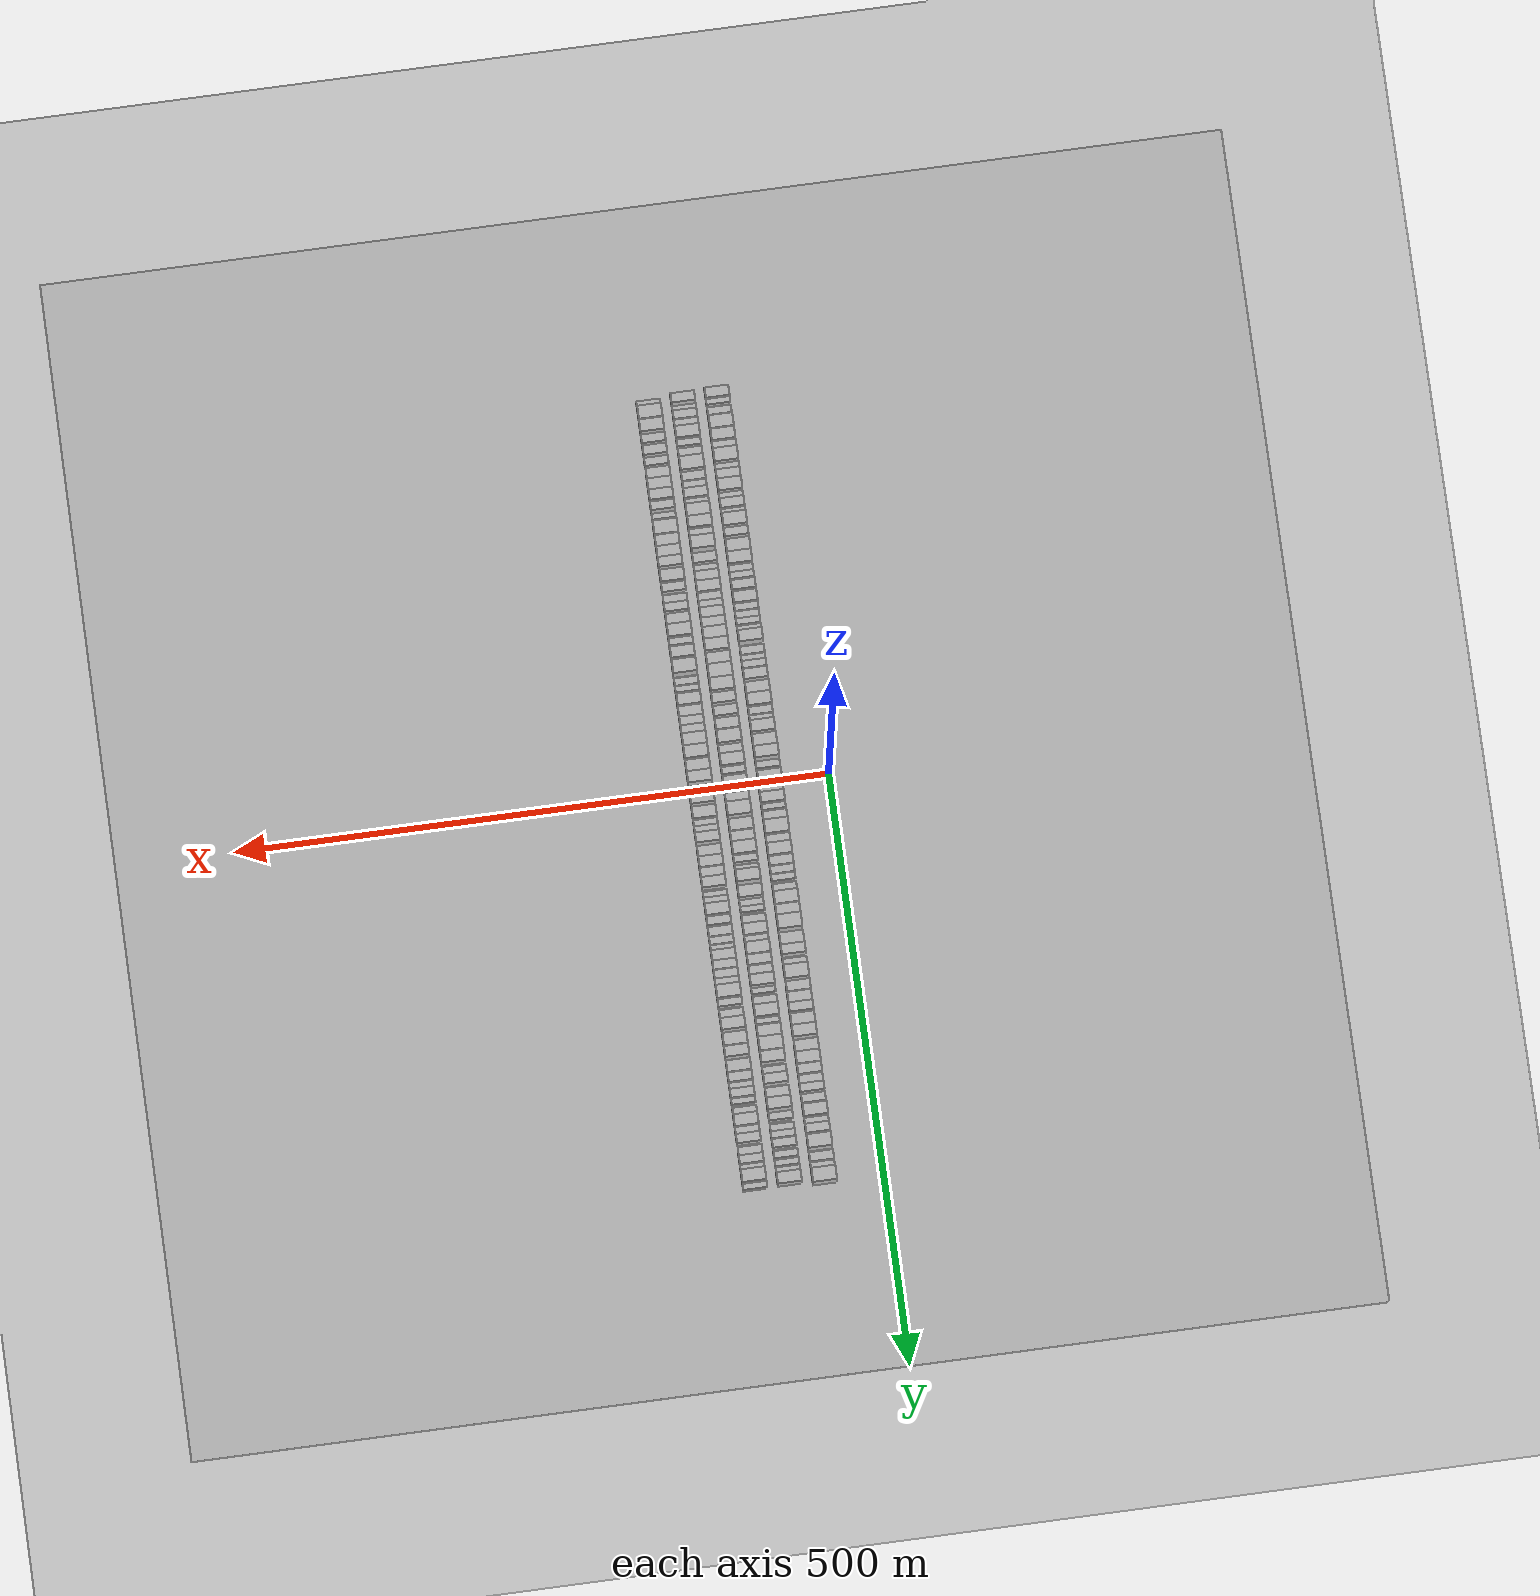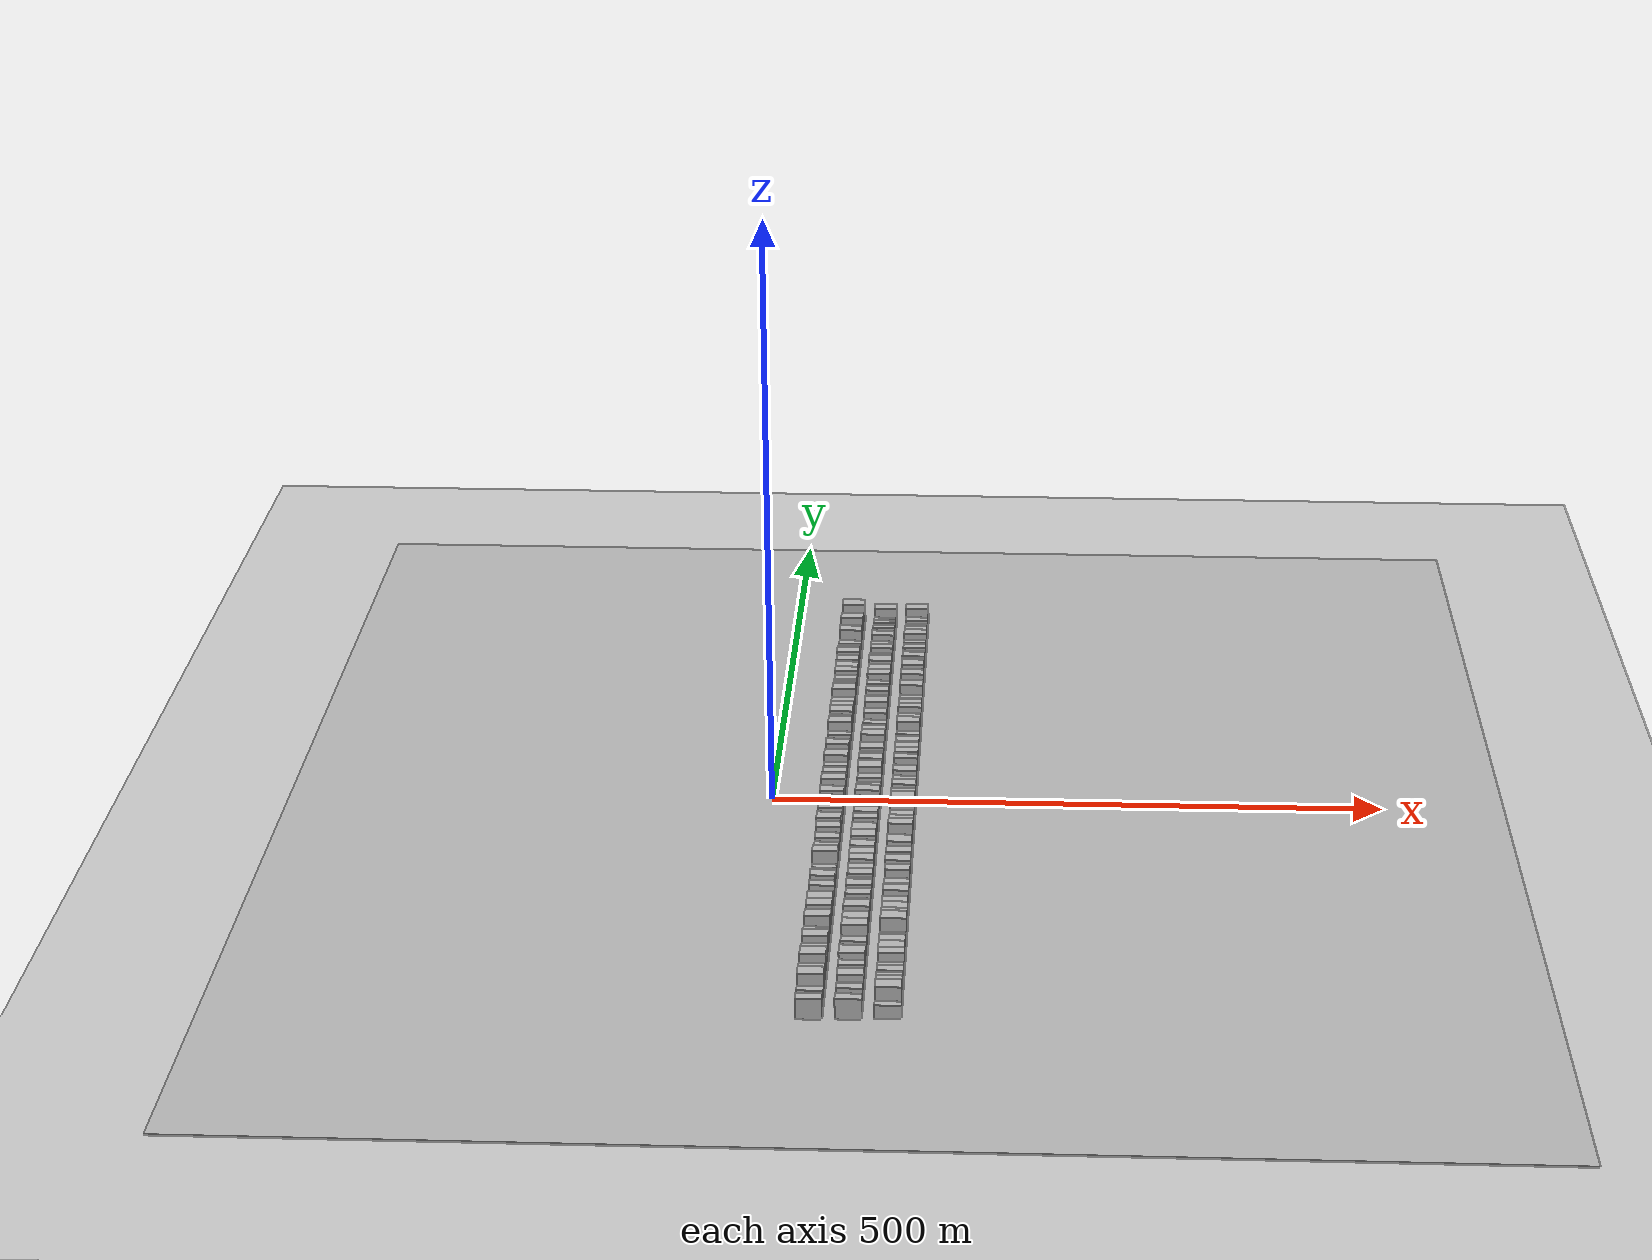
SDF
<?xml version="1.0" encoding="utf-8"?>

<sdf version="1.6">

   <world name="default">

      <gui fullscreen="0">

         <camera name="user_camera">

            <pose>-15 0 4.57585 0 0 0</pose>

            <view_controller>orbit</view_controller>

         </camera>

      </gui>

      <scene>

         <sky>

           <clouds>

             <speed>12</speed>

           </clouds>

         </sky>

         <ambient>0.4 0.4 0.4 1</ambient>

         <background>0.7 0.7 0.7 1</background>

         <shadows>1</shadows>

      </scene>

      <gravity>0 0 -9.8066</gravity>

      <magnetic_field>6e-06 2.3e-05 -4.2e-05</magnetic_field>

      <physics default="0" name="default_physics" type="ode">

         <ode>

            <solver>

               <type>quick</type>

               <iters>10</iters>

               <sor>1.0</sor>

               <use_dynamic_moi_rescaling>0</use_dynamic_moi_rescaling>

            </solver>

            <constraints>

               <cfm>0</cfm>

               <erp>0.2</erp>

               <contact_max_correcting_vel>100</contact_max_correcting_vel>

               <contact_surface_layer>0.001</contact_surface_layer>

            </constraints>

         </ode>

         <max_step_size>0.004</max_step_size>

         <real_time_factor>1</real_time_factor>

         <real_time_update_rate>250</real_time_update_rate>

      </physics>

      <light name="sun" type="directional">

         <cast_shadows>1</cast_shadows>

         <pose>0 0 10 0 0 0</pose>

         <diffuse>0.8 0.8 0.8 1</diffuse>

         <specular>0.2 0.2 0.2 1</specular>

         <attenuation>

            <range>1000</range>

            <constant>0.9</constant>

            <linear>0.01</linear>

            <quadratic>0.001</quadratic>

         </attenuation>

         <direction>-0.5 0.1 -0.9</direction>

      </light>

      <include>

         <name>ground_plane_1</name>

         <uri>model://HANNAS_ground_plane</uri>

         <pose>0 0 0  0 0 0</pose>

      </include>

      <include>

         <name>ground_plane_2</name>

         <uri>model://HANNAS_ground_plane</uri>

         <pose>100 0 0  0 0 0</pose>

      </include>

      <model name="building_1">

         <static>1</static>

         <pose frame="">50.0000 -331.6068 0 0.000000 0.000000 0.000000</pose>

         <link name="link">

            <pose frame="">0 0 9.00 0 0 0</pose>

            <collision name="collision">

               <geometry>

                  <box>

                     <size>20.0000 8.7864 18.0000</size>

                  </box>

               </geometry>

               <max_contacts>10</max_contacts>

               <surface>

                  <contact>

                     <ode/>

                  </contact>

                  <bounce/>

                  <friction>

                     <torsional>

                        <ode/>

                     </torsional>

                     <ode/>

                  </friction>

               </surface>

            </collision>

            <visual name="visual">

               <cast_shadows>0</cast_shadows>

               <geometry>

                  <box>

                     <size>20.0000 8.7864 18.0000</size>

                  </box>

               </geometry>

               <material>

                  <script>

                     <uri>model://HANNAS_wall/materials/scripts</uri>

                     <uri>model://HANNAS_wall/materials/textures</uri>

                     <name>vrc/HANNAS_wall</name>

                  </script>

               </material>

            </visual>

            <self_collide>0</self_collide>

            <enable_wind>0</enable_wind>

            <kinematic>0</kinematic>

         </link>

      </model>

      <model name="building_2">

         <static>1</static>

         <pose frame="">50.0000 -324.7997 0 0.000000 0.000000 0.000000</pose>

         <link name="link">

            <pose frame="">0 0 6.00 0 0 0</pose>

            <collision name="collision">

               <geometry>

                  <box>

                     <size>20.0000 4.8279 12.0000</size>

                  </box>

               </geometry>

               <max_contacts>10</max_contacts>

               <surface>

                  <contact>

                     <ode/>

                  </contact>

                  <bounce/>

                  <friction>

                     <torsional>

                        <ode/>

                     </torsional>

                     <ode/>

                  </friction>

               </surface>

            </collision>

            <visual name="visual">

               <cast_shadows>0</cast_shadows>

               <geometry>

                  <box>

                     <size>20.0000 4.8279 12.0000</size>

                  </box>

               </geometry>

               <material>

                  <script>

                     <uri>model://HANNAS_wall/materials/scripts</uri>

                     <uri>model://HANNAS_wall/materials/textures</uri>

                     <name>vrc/HANNAS_wall</name>

                  </script>

               </material>

            </visual>

            <self_collide>0</self_collide>

            <enable_wind>0</enable_wind>

            <kinematic>0</kinematic>

         </link>

      </model>

      <model name="building_3">

         <static>1</static>

         <pose frame="">50.0000 -316.2116 0 0.000000 0.000000 0.000000</pose>

         <link name="link">

            <pose frame="">0 0 7.50 0 0 0</pose>

            <collision name="collision">

               <geometry>

                  <box>

                     <size>20.0000 6.3482 15.0000</size>

                  </box>

               </geometry>

               <max_contacts>10</max_contacts>

               <surface>

                  <contact>

                     <ode/>

                  </contact>

                  <bounce/>

                  <friction>

                     <torsional>

                        <ode/>

                     </torsional>

                     <ode/>

                  </friction>

               </surface>

            </collision>

            <visual name="visual">

               <cast_shadows>0</cast_shadows>

               <geometry>

                  <box>

                     <size>20.0000 6.3482 15.0000</size>

                  </box>

               </geometry>

               <material>

                  <script>

                     <uri>model://HANNAS_wall/materials/scripts</uri>

                     <uri>model://HANNAS_wall/materials/textures</uri>

                     <name>vrc/HANNAS_wall</name>

                  </script>

               </material>

            </visual>

            <self_collide>0</self_collide>

            <enable_wind>0</enable_wind>

            <kinematic>0</kinematic>

         </link>

      </model>

      <model name="building_4">

         <static>1</static>

         <pose frame="">50.0000 -305.5548 0 0.000000 0.000000 0.000000</pose>

         <link name="link">

            <pose frame="">0 0 12.00 0 0 0</pose>

            <collision name="collision">

               <geometry>

                  <box>

                     <size>20.0000 10.9654 24.0000</size>

                  </box>

               </geometry>

               <max_contacts>10</max_contacts>

               <surface>

                  <contact>

                     <ode/>

                  </contact>

                  <bounce/>

                  <friction>

                     <torsional>

                        <ode/>

                     </torsional>

                     <ode/>

                  </friction>

               </surface>

            </collision>

            <visual name="visual">

               <cast_shadows>0</cast_shadows>

               <geometry>

                  <box>

                     <size>20.0000 10.9654 24.0000</size>

                  </box>

               </geometry>

               <material>

                  <script>

                     <uri>model://HANNAS_wall/materials/scripts</uri>

                     <uri>model://HANNAS_wall/materials/textures</uri>

                     <name>vrc/HANNAS_wall</name>

                  </script>

               </material>

            </visual>

            <self_collide>0</self_collide>

            <enable_wind>0</enable_wind>

            <kinematic>0</kinematic>

         </link>

      </model>

      <model name="building_5">

         <static>1</static>

         <pose frame="">50.0000 -295.1670 0 0.000000 0.000000 0.000000</pose>

         <link name="link">

            <pose frame="">0 0 10.50 0 0 0</pose>

            <collision name="collision">

               <geometry>

                  <box>

                     <size>20.0000 9.8102 21.0000</size>

                  </box>

               </geometry>

               <max_contacts>10</max_contacts>

               <surface>

                  <contact>

                     <ode/>

                  </contact>

                  <bounce/>

                  <friction>

                     <torsional>

                        <ode/>

                     </torsional>

                     <ode/>

                  </friction>

               </surface>

            </collision>

            <visual name="visual">

               <cast_shadows>0</cast_shadows>

               <geometry>

                  <box>

                     <size>20.0000 9.8102 21.0000</size>

                  </box>

               </geometry>

               <material>

                  <script>

                     <uri>model://HANNAS_wall/materials/scripts</uri>

                     <uri>model://HANNAS_wall/materials/textures</uri>

                     <name>vrc/HANNAS_wall</name>

                  </script>

               </material>

            </visual>

            <self_collide>0</self_collide>

            <enable_wind>0</enable_wind>

            <kinematic>0</kinematic>

         </link>

      </model>

      <model name="building_6">

         <static>1</static>

         <pose frame="">50.0000 -286.6234 0 0.000000 0.000000 0.000000</pose>

         <link name="link">

            <pose frame="">0 0 7.50 0 0 0</pose>

            <collision name="collision">

               <geometry>

                  <box>

                     <size>20.0000 7.2769 15.0000</size>

                  </box>

               </geometry>

               <max_contacts>10</max_contacts>

               <surface>

                  <contact>

                     <ode/>

                  </contact>

                  <bounce/>

                  <friction>

                     <torsional>

                        <ode/>

                     </torsional>

                     <ode/>

                  </friction>

               </surface>

            </collision>

            <visual name="visual">

               <cast_shadows>0</cast_shadows>

               <geometry>

                  <box>

                     <size>20.0000 7.2769 15.0000</size>

                  </box>

               </geometry>

               <material>

                  <script>

                     <uri>model://HANNAS_wall/materials/scripts</uri>

                     <uri>model://HANNAS_wall/materials/textures</uri>

                     <name>vrc/HANNAS_wall</name>

                  </script>

               </material>

            </visual>

            <self_collide>0</self_collide>

            <enable_wind>0</enable_wind>

            <kinematic>0</kinematic>

         </link>

      </model>

      <model name="building_7">

         <static>1</static>

         <pose frame="">50.0000 -277.2917 0 0.000000 0.000000 0.000000</pose>

         <link name="link">

            <pose frame="">0 0 12.00 0 0 0</pose>

            <collision name="collision">

               <geometry>

                  <box>

                     <size>20.0000 11.3866 24.0000</size>

                  </box>

               </geometry>

               <max_contacts>10</max_contacts>

               <surface>

                  <contact>

                     <ode/>

                  </contact>

                  <bounce/>

                  <friction>

                     <torsional>

                        <ode/>

                     </torsional>

                     <ode/>

                  </friction>

               </surface>

            </collision>

            <visual name="visual">

               <cast_shadows>0</cast_shadows>

               <geometry>

                  <box>

                     <size>20.0000 11.3866 24.0000</size>

                  </box>

               </geometry>

               <material>

                  <script>

                     <uri>model://HANNAS_wall/materials/scripts</uri>

                     <uri>model://HANNAS_wall/materials/textures</uri>

                     <name>vrc/HANNAS_wall</name>

                  </script>

               </material>

            </visual>

            <self_collide>0</self_collide>

            <enable_wind>0</enable_wind>

            <kinematic>0</kinematic>

         </link>

      </model>

      <model name="building_8">

         <static>1</static>

         <pose frame="">50.0000 -268.7223 0 0.000000 0.000000 0.000000</pose>

         <link name="link">

            <pose frame="">0 0 6.00 0 0 0</pose>

            <collision name="collision">

               <geometry>

                  <box>

                     <size>20.0000 5.7520 12.0000</size>

                  </box>

               </geometry>

               <max_contacts>10</max_contacts>

               <surface>

                  <contact>

                     <ode/>

                  </contact>

                  <bounce/>

                  <friction>

                     <torsional>

                        <ode/>

                     </torsional>

                     <ode/>

                  </friction>

               </surface>

            </collision>

            <visual name="visual">

               <cast_shadows>0</cast_shadows>

               <geometry>

                  <box>

                     <size>20.0000 5.7520 12.0000</size>

                  </box>

               </geometry>

               <material>

                  <script>

                     <uri>model://HANNAS_wall/materials/scripts</uri>

                     <uri>model://HANNAS_wall/materials/textures</uri>

                     <name>vrc/HANNAS_wall</name>

                  </script>

               </material>

            </visual>

            <self_collide>0</self_collide>

            <enable_wind>0</enable_wind>

            <kinematic>0</kinematic>

         </link>

      </model>

      <model name="building_9">

         <static>1</static>

         <pose frame="">50.0000 -261.3780 0 0.000000 0.000000 0.000000</pose>

         <link name="link">

            <pose frame="">0 0 9.00 0 0 0</pose>

            <collision name="collision">

               <geometry>

                  <box>

                     <size>20.0000 8.9367 18.0000</size>

                  </box>

               </geometry>

               <max_contacts>10</max_contacts>

               <surface>

                  <contact>

                     <ode/>

                  </contact>

                  <bounce/>

                  <friction>

                     <torsional>

                        <ode/>

                     </torsional>

                     <ode/>

                  </friction>

               </surface>

            </collision>

            <visual name="visual">

               <cast_shadows>0</cast_shadows>

               <geometry>

                  <box>

                     <size>20.0000 8.9367 18.0000</size>

                  </box>

               </geometry>

               <material>

                  <script>

                     <uri>model://HANNAS_wall/materials/scripts</uri>

                     <uri>model://HANNAS_wall/materials/textures</uri>

                     <name>vrc/HANNAS_wall</name>

                  </script>

               </material>

            </visual>

            <self_collide>0</self_collide>

            <enable_wind>0</enable_wind>

            <kinematic>0</kinematic>

         </link>

      </model>

      <model name="building_10">

         <static>1</static>

         <pose frame="">50.0000 -251.7813 0 0.000000 0.000000 0.000000</pose>

         <link name="link">

            <pose frame="">0 0 12.00 0 0 0</pose>

            <collision name="collision">

               <geometry>

                  <box>

                     <size>20.0000 10.2565 24.0000</size>

                  </box>

               </geometry>

               <max_contacts>10</max_contacts>

               <surface>

                  <contact>

                     <ode/>

                  </contact>

                  <bounce/>

                  <friction>

                     <torsional>

                        <ode/>

                     </torsional>

                     <ode/>

                  </friction>

               </surface>

            </collision>

            <visual name="visual">

               <cast_shadows>0</cast_shadows>

               <geometry>

                  <box>

                     <size>20.0000 10.2565 24.0000</size>

                  </box>

               </geometry>

               <material>

                  <script>

                     <uri>model://HANNAS_wall/materials/scripts</uri>

                     <uri>model://HANNAS_wall/materials/textures</uri>

                     <name>vrc/HANNAS_wall</name>

                  </script>

               </material>

            </visual>

            <self_collide>0</self_collide>

            <enable_wind>0</enable_wind>

            <kinematic>0</kinematic>

         </link>

      </model>

      <model name="building_11">

         <static>1</static>

         <pose frame="">50.0000 -243.8855 0 0.000000 0.000000 0.000000</pose>

         <link name="link">

            <pose frame="">0 0 6.00 0 0 0</pose>

            <collision name="collision">

               <geometry>

                  <box>

                     <size>20.0000 5.5351 12.0000</size>

                  </box>

               </geometry>

               <max_contacts>10</max_contacts>

               <surface>

                  <contact>

                     <ode/>

                  </contact>

                  <bounce/>

                  <friction>

                     <torsional>

                        <ode/>

                     </torsional>

                     <ode/>

                  </friction>

               </surface>

            </collision>

            <visual name="visual">

               <cast_shadows>0</cast_shadows>

               <geometry>

                  <box>

                     <size>20.0000 5.5351 12.0000</size>

                  </box>

               </geometry>

               <material>

                  <script>

                     <uri>model://HANNAS_wall/materials/scripts</uri>

                     <uri>model://HANNAS_wall/materials/textures</uri>

                     <name>vrc/HANNAS_wall</name>

                  </script>

               </material>

            </visual>

            <self_collide>0</self_collide>

            <enable_wind>0</enable_wind>

            <kinematic>0</kinematic>

         </link>

      </model>

      <model name="building_12">

         <static>1</static>

         <pose frame="">50.0000 -236.9930 0 0.000000 0.000000 0.000000</pose>

         <link name="link">

            <pose frame="">0 0 9.00 0 0 0</pose>

            <collision name="collision">

               <geometry>

                  <box>

                     <size>20.0000 8.2500 18.0000</size>

                  </box>

               </geometry>

               <max_contacts>10</max_contacts>

               <surface>

                  <contact>

                     <ode/>

                  </contact>

                  <bounce/>

                  <friction>

                     <torsional>

                        <ode/>

                     </torsional>

                     <ode/>

                  </friction>

               </surface>

            </collision>

            <visual name="visual">

               <cast_shadows>0</cast_shadows>

               <geometry>

                  <box>

                     <size>20.0000 8.2500 18.0000</size>

                  </box>

               </geometry>

               <material>

                  <script>

                     <uri>model://HANNAS_wall/materials/scripts</uri>

                     <uri>model://HANNAS_wall/materials/textures</uri>

                     <name>vrc/HANNAS_wall</name>

                  </script>

               </material>

            </visual>

            <self_collide>0</self_collide>

            <enable_wind>0</enable_wind>

            <kinematic>0</kinematic>

         </link>

      </model>

      <model name="building_13">

         <static>1</static>

         <pose frame="">50.0000 -230.2157 0 0.000000 0.000000 0.000000</pose>

         <link name="link">

            <pose frame="">0 0 6.00 0 0 0</pose>

            <collision name="collision">

               <geometry>

                  <box>

                     <size>20.0000 5.3045 12.0000</size>

                  </box>

               </geometry>

               <max_contacts>10</max_contacts>

               <surface>

                  <contact>

                     <ode/>

                  </contact>

                  <bounce/>

                  <friction>

                     <torsional>

                        <ode/>

                     </torsional>

                     <ode/>

                  </friction>

               </surface>

            </collision>

            <visual name="visual">

               <cast_shadows>0</cast_shadows>

               <geometry>

                  <box>

                     <size>20.0000 5.3045 12.0000</size>

                  </box>

               </geometry>

               <material>

                  <script>

                     <uri>model://HANNAS_wall/materials/scripts</uri>

                     <uri>model://HANNAS_wall/materials/textures</uri>

                     <name>vrc/HANNAS_wall</name>

                  </script>

               </material>

            </visual>

            <self_collide>0</self_collide>

            <enable_wind>0</enable_wind>

            <kinematic>0</kinematic>

         </link>

      </model>

      <model name="building_14">

         <static>1</static>

         <pose frame="">50.0000 -222.1826 0 0.000000 0.000000 0.000000</pose>

         <link name="link">

            <pose frame="">0 0 12.00 0 0 0</pose>

            <collision name="collision">

               <geometry>

                  <box>

                     <size>20.0000 10.7617 24.0000</size>

                  </box>

               </geometry>

               <max_contacts>10</max_contacts>

               <surface>

                  <contact>

                     <ode/>

                  </contact>

                  <bounce/>

                  <friction>

                     <torsional>

                        <ode/>

                     </torsional>

                     <ode/>

                  </friction>

               </surface>

            </collision>

            <visual name="visual">

               <cast_shadows>0</cast_shadows>

               <geometry>

                  <box>

                     <size>20.0000 10.7617 24.0000</size>

                  </box>

               </geometry>

               <material>

                  <script>

                     <uri>model://HANNAS_wall/materials/scripts</uri>

                     <uri>model://HANNAS_wall/materials/textures</uri>

                     <name>vrc/HANNAS_wall</name>

                  </script>

               </material>

            </visual>

            <self_collide>0</self_collide>

            <enable_wind>0</enable_wind>

            <kinematic>0</kinematic>

         </link>

      </model>

      <model name="building_15">

         <static>1</static>

         <pose frame="">50.0000 -212.1876 0 0.000000 0.000000 0.000000</pose>

         <link name="link">

            <pose frame="">0 0 9.00 0 0 0</pose>

            <collision name="collision">

               <geometry>

                  <box>

                     <size>20.0000 7.2282 18.0000</size>

                  </box>

               </geometry>

               <max_contacts>10</max_contacts>

               <surface>

                  <contact>

                     <ode/>

                  </contact>

                  <bounce/>

                  <friction>

                     <torsional>

                        <ode/>

                     </torsional>

                     <ode/>

                  </friction>

               </surface>

            </collision>

            <visual name="visual">

               <cast_shadows>0</cast_shadows>

               <geometry>

                  <box>

                     <size>20.0000 7.2282 18.0000</size>

                  </box>

               </geometry>

               <material>

                  <script>

                     <uri>model://HANNAS_wall/materials/scripts</uri>

                     <uri>model://HANNAS_wall/materials/textures</uri>

                     <name>vrc/HANNAS_wall</name>

                  </script>

               </material>

            </visual>

            <self_collide>0</self_collide>

            <enable_wind>0</enable_wind>

            <kinematic>0</kinematic>

         </link>

      </model>

      <model name="building_16">

         <static>1</static>

         <pose frame="">50.0000 -200.3378 0 0.000000 0.000000 0.000000</pose>

         <link name="link">

            <pose frame="">0 0 10.50 0 0 0</pose>

            <collision name="collision">

               <geometry>

                  <box>

                     <size>20.0000 10.4713 21.0000</size>

                  </box>

               </geometry>

               <max_contacts>10</max_contacts>

               <surface>

                  <contact>

                     <ode/>

                  </contact>

                  <bounce/>

                  <friction>

                     <torsional>

                        <ode/>

                     </torsional>

                     <ode/>

                  </friction>

               </surface>

            </collision>

            <visual name="visual">

               <cast_shadows>0</cast_shadows>

               <geometry>

                  <box>

                     <size>20.0000 10.4713 21.0000</size>

                  </box>

               </geometry>

               <material>

                  <script>

                     <uri>model://HANNAS_wall/materials/scripts</uri>

                     <uri>model://HANNAS_wall/materials/textures</uri>

                     <name>vrc/HANNAS_wall</name>

                  </script>

               </material>

            </visual>

            <self_collide>0</self_collide>

            <enable_wind>0</enable_wind>

            <kinematic>0</kinematic>

         </link>

      </model>

      <model name="building_17">

         <static>1</static>

         <pose frame="">50.0000 -189.9298 0 0.000000 0.000000 0.000000</pose>

         <link name="link">

            <pose frame="">0 0 10.50 0 0 0</pose>

            <collision name="collision">

               <geometry>

                  <box>

                     <size>20.0000 10.3448 21.0000</size>

                  </box>

               </geometry>

               <max_contacts>10</max_contacts>

               <surface>

                  <contact>

                     <ode/>

                  </contact>

                  <bounce/>

                  <friction>

                     <torsional>

                        <ode/>

                     </torsional>

                     <ode/>

                  </friction>

               </surface>

            </collision>

            <visual name="visual">

               <cast_shadows>0</cast_shadows>

               <geometry>

                  <box>

                     <size>20.0000 10.3448 21.0000</size>

                  </box>

               </geometry>

               <material>

                  <script>

                     <uri>model://HANNAS_wall/materials/scripts</uri>

                     <uri>model://HANNAS_wall/materials/textures</uri>

                     <name>vrc/HANNAS_wall</name>

                  </script>

               </material>

            </visual>

            <self_collide>0</self_collide>

            <enable_wind>0</enable_wind>

            <kinematic>0</kinematic>

         </link>

      </model>

      <model name="building_18">

         <static>1</static>

         <pose frame="">50.0000 -181.8283 0 0.000000 0.000000 0.000000</pose>

         <link name="link">

            <pose frame="">0 0 6.00 0 0 0</pose>

            <collision name="collision">

               <geometry>

                  <box>

                     <size>20.0000 5.8581 12.0000</size>

                  </box>

               </geometry>

               <max_contacts>10</max_contacts>

               <surface>

                  <contact>

                     <ode/>

                  </contact>

                  <bounce/>

                  <friction>

                     <torsional>

                        <ode/>

                     </torsional>

                     <ode/>

                  </friction>

               </surface>

            </collision>

            <visual name="visual">

               <cast_shadows>0</cast_shadows>

               <geometry>

                  <box>

                     <size>20.0000 5.8581 12.0000</size>

                  </box>

               </geometry>

               <material>

                  <script>

                     <uri>model://HANNAS_wall/materials/scripts</uri>

                     <uri>model://HANNAS_wall/materials/textures</uri>

                     <name>vrc/HANNAS_wall</name>

                  </script>

               </material>

            </visual>

            <self_collide>0</self_collide>

            <enable_wind>0</enable_wind>

            <kinematic>0</kinematic>

         </link>

      </model>

      <model name="building_19">

         <static>1</static>

         <pose frame="">50.0000 -175.9938 0 0.000000 0.000000 0.000000</pose>

         <link name="link">

            <pose frame="">0 0 6.00 0 0 0</pose>

            <collision name="collision">

               <geometry>

                  <box>

                     <size>20.0000 5.8110 12.0000</size>

                  </box>

               </geometry>

               <max_contacts>10</max_contacts>

               <surface>

                  <contact>

                     <ode/>

                  </contact>

                  <bounce/>

                  <friction>

                     <torsional>

                        <ode/>

                     </torsional>

                     <ode/>

                  </friction>

               </surface>

            </collision>

            <visual name="visual">

               <cast_shadows>0</cast_shadows>

               <geometry>

                  <box>

                     <size>20.0000 5.8110 12.0000</size>

                  </box>

               </geometry>

               <material>

                  <script>

                     <uri>model://HANNAS_wall/materials/scripts</uri>

                     <uri>model://HANNAS_wall/materials/textures</uri>

                     <name>vrc/HANNAS_wall</name>

                  </script>

               </material>

            </visual>

            <self_collide>0</self_collide>

            <enable_wind>0</enable_wind>

            <kinematic>0</kinematic>

         </link>

      </model>

      <model name="building_20">

         <static>1</static>

         <pose frame="">50.0000 -167.0182 0 0.000000 0.000000 0.000000</pose>

         <link name="link">

            <pose frame="">0 0 9.00 0 0 0</pose>

            <collision name="collision">

               <geometry>

                  <box>

                     <size>20.0000 8.1402 18.0000</size>

                  </box>

               </geometry>

               <max_contacts>10</max_contacts>

               <surface>

                  <contact>

                     <ode/>

                  </contact>

                  <bounce/>

                  <friction>

                     <torsional>

                        <ode/>

                     </torsional>

                     <ode/>

                  </friction>

               </surface>

            </collision>

            <visual name="visual">

               <cast_shadows>0</cast_shadows>

               <geometry>

                  <box>

                     <size>20.0000 8.1402 18.0000</size>

                  </box>

               </geometry>

               <material>

                  <script>

                     <uri>model://HANNAS_wall/materials/scripts</uri>

                     <uri>model://HANNAS_wall/materials/textures</uri>

                     <name>vrc/HANNAS_wall</name>

                  </script>

               </material>

            </visual>

            <self_collide>0</self_collide>

            <enable_wind>0</enable_wind>

            <kinematic>0</kinematic>

         </link>

      </model>

      <model name="building_21">

         <static>1</static>

         <pose frame="">50.0000 -156.1584 0 0.000000 0.000000 0.000000</pose>

         <link name="link">

            <pose frame="">0 0 10.50 0 0 0</pose>

            <collision name="collision">

               <geometry>

                  <box>

                     <size>20.0000 9.5794 21.0000</size>

                  </box>

               </geometry>

               <max_contacts>10</max_contacts>

               <surface>

                  <contact>

                     <ode/>

                  </contact>

                  <bounce/>

                  <friction>

                     <torsional>

                        <ode/>

                     </torsional>

                     <ode/>

                  </friction>

               </surface>

            </collision>

            <visual name="visual">

               <cast_shadows>0</cast_shadows>

               <geometry>

                  <box>

                     <size>20.0000 9.5794 21.0000</size>

                  </box>

               </geometry>

               <material>

                  <script>

                     <uri>model://HANNAS_wall/materials/scripts</uri>

                     <uri>model://HANNAS_wall/materials/textures</uri>

                     <name>vrc/HANNAS_wall</name>

                  </script>

               </material>

            </visual>

            <self_collide>0</self_collide>

            <enable_wind>0</enable_wind>

            <kinematic>0</kinematic>

         </link>

      </model>

      <model name="building_22">

         <static>1</static>

         <pose frame="">50.0000 -148.3388 0 0.000000 0.000000 0.000000</pose>

         <link name="link">

            <pose frame="">0 0 7.50 0 0 0</pose>

            <collision name="collision">

               <geometry>

                  <box>

                     <size>20.0000 6.0599 15.0000</size>

                  </box>

               </geometry>

               <max_contacts>10</max_contacts>

               <surface>

                  <contact>

                     <ode/>

                  </contact>

                  <bounce/>

                  <friction>

                     <torsional>

                        <ode/>

                     </torsional>

                     <ode/>

                  </friction>

               </surface>

            </collision>

            <visual name="visual">

               <cast_shadows>0</cast_shadows>

               <geometry>

                  <box>

                     <size>20.0000 6.0599 15.0000</size>

                  </box>

               </geometry>

               <material>

                  <script>

                     <uri>model://HANNAS_wall/materials/scripts</uri>

                     <uri>model://HANNAS_wall/materials/textures</uri>

                     <name>vrc/HANNAS_wall</name>

                  </script>

               </material>

            </visual>

            <self_collide>0</self_collide>

            <enable_wind>0</enable_wind>

            <kinematic>0</kinematic>

         </link>

      </model>

      <model name="building_23">

         <static>1</static>

         <pose frame="">50.0000 -142.3592 0 0.000000 0.000000 0.000000</pose>

         <link name="link">

            <pose frame="">0 0 6.00 0 0 0</pose>

            <collision name="collision">

               <geometry>

                  <box>

                     <size>20.0000 5.8992 12.0000</size>

                  </box>

               </geometry>

               <max_contacts>10</max_contacts>

               <surface>

                  <contact>

                     <ode/>

                  </contact>

                  <bounce/>

                  <friction>

                     <torsional>

                        <ode/>

                     </torsional>

                     <ode/>

                  </friction>

               </surface>

            </collision>

            <visual name="visual">

               <cast_shadows>0</cast_shadows>

               <geometry>

                  <box>

                     <size>20.0000 5.8992 12.0000</size>

                  </box>

               </geometry>

               <material>

                  <script>

                     <uri>model://HANNAS_wall/materials/scripts</uri>

                     <uri>model://HANNAS_wall/materials/textures</uri>

                     <name>vrc/HANNAS_wall</name>

                  </script>

               </material>

            </visual>

            <self_collide>0</self_collide>

            <enable_wind>0</enable_wind>

            <kinematic>0</kinematic>

         </link>

      </model>

      <model name="building_24">

         <static>1</static>

         <pose frame="">50.0000 -136.6137 0 0.000000 0.000000 0.000000</pose>

         <link name="link">

            <pose frame="">0 0 6.00 0 0 0</pose>

            <collision name="collision">

               <geometry>

                  <box>

                     <size>20.0000 5.5917 12.0000</size>

                  </box>

               </geometry>

               <max_contacts>10</max_contacts>

               <surface>

                  <contact>

                     <ode/>

                  </contact>

                  <bounce/>

                  <friction>

                     <torsional>

                        <ode/>

                     </torsional>

                     <ode/>

                  </friction>

               </surface>

            </collision>

            <visual name="visual">

               <cast_shadows>0</cast_shadows>

               <geometry>

                  <box>

                     <size>20.0000 5.5917 12.0000</size>

                  </box>

               </geometry>

               <material>

                  <script>

                     <uri>model://HANNAS_wall/materials/scripts</uri>

                     <uri>model://HANNAS_wall/materials/textures</uri>

                     <name>vrc/HANNAS_wall</name>

                  </script>

               </material>

            </visual>

            <self_collide>0</self_collide>

            <enable_wind>0</enable_wind>

            <kinematic>0</kinematic>

         </link>

      </model>

      <model name="building_25">

         <static>1</static>

         <pose frame="">50.0000 -130.1147 0 0.000000 0.000000 0.000000</pose>

         <link name="link">

            <pose frame="">0 0 6.00 0 0 0</pose>

            <collision name="collision">

               <geometry>

                  <box>

                     <size>20.0000 5.4064 12.0000</size>

                  </box>

               </geometry>

               <max_contacts>10</max_contacts>

               <surface>

                  <contact>

                     <ode/>

                  </contact>

                  <bounce/>

                  <friction>

                     <torsional>

                        <ode/>

                     </torsional>

                     <ode/>

                  </friction>

               </surface>

            </collision>

            <visual name="visual">

               <cast_shadows>0</cast_shadows>

               <geometry>

                  <box>

                     <size>20.0000 5.4064 12.0000</size>

                  </box>

               </geometry>

               <material>

                  <script>

                     <uri>model://HANNAS_wall/materials/scripts</uri>

                     <uri>model://HANNAS_wall/materials/textures</uri>

                     <name>vrc/HANNAS_wall</name>

                  </script>

               </material>

            </visual>

            <self_collide>0</self_collide>

            <enable_wind>0</enable_wind>

            <kinematic>0</kinematic>

         </link>

      </model>

      <model name="building_26">

         <static>1</static>

         <pose frame="">50.0000 -122.5691 0 0.000000 0.000000 0.000000</pose>

         <link name="link">

            <pose frame="">0 0 12.00 0 0 0</pose>

            <collision name="collision">

               <geometry>

                  <box>

                     <size>20.0000 9.6849 24.0000</size>

                  </box>

               </geometry>

               <max_contacts>10</max_contacts>

               <surface>

                  <contact>

                     <ode/>

                  </contact>

                  <bounce/>

                  <friction>

                     <torsional>

                        <ode/>

                     </torsional>

                     <ode/>

                  </friction>

               </surface>

            </collision>

            <visual name="visual">

               <cast_shadows>0</cast_shadows>

               <geometry>

                  <box>

                     <size>20.0000 9.6849 24.0000</size>

                  </box>

               </geometry>

               <material>

                  <script>

                     <uri>model://HANNAS_wall/materials/scripts</uri>

                     <uri>model://HANNAS_wall/materials/textures</uri>

                     <name>vrc/HANNAS_wall</name>

                  </script>

               </material>

            </visual>

            <self_collide>0</self_collide>

            <enable_wind>0</enable_wind>

            <kinematic>0</kinematic>

         </link>

      </model>

      <model name="building_27">

         <static>1</static>

         <pose frame="">50.0000 -111.2529 0 0.000000 0.000000 0.000000</pose>

         <link name="link">

            <pose frame="">0 0 7.50 0 0 0</pose>

            <collision name="collision">

               <geometry>

                  <box>

                     <size>20.0000 6.9476 15.0000</size>

                  </box>

               </geometry>

               <max_contacts>10</max_contacts>

               <surface>

                  <contact>

                     <ode/>

                  </contact>

                  <bounce/>

                  <friction>

                     <torsional>

                        <ode/>

                     </torsional>

                     <ode/>

                  </friction>

               </surface>

            </collision>

            <visual name="visual">

               <cast_shadows>0</cast_shadows>

               <geometry>

                  <box>

                     <size>20.0000 6.9476 15.0000</size>

                  </box>

               </geometry>

               <material>

                  <script>

                     <uri>model://HANNAS_wall/materials/scripts</uri>

                     <uri>model://HANNAS_wall/materials/textures</uri>

                     <name>vrc/HANNAS_wall</name>

                  </script>

               </material>

            </visual>

            <self_collide>0</self_collide>

            <enable_wind>0</enable_wind>

            <kinematic>0</kinematic>

         </link>

      </model>

      <model name="building_28">

         <static>1</static>

         <pose frame="">50.0000 -105.2134 0 0.000000 0.000000 0.000000</pose>

         <link name="link">

            <pose frame="">0 0 6.00 0 0 0</pose>

            <collision name="collision">

               <geometry>

                  <box>

                     <size>20.0000 5.1313 12.0000</size>

                  </box>

               </geometry>

               <max_contacts>10</max_contacts>

               <surface>

                  <contact>

                     <ode/>

                  </contact>

                  <bounce/>

                  <friction>

                     <torsional>

                        <ode/>

                     </torsional>

                     <ode/>

                  </friction>

               </surface>

            </collision>

            <visual name="visual">

               <cast_shadows>0</cast_shadows>

               <geometry>

                  <box>

                     <size>20.0000 5.1313 12.0000</size>

                  </box>

               </geometry>

               <material>

                  <script>

                     <uri>model://HANNAS_wall/materials/scripts</uri>

                     <uri>model://HANNAS_wall/materials/textures</uri>

                     <name>vrc/HANNAS_wall</name>

                  </script>

               </material>

            </visual>

            <self_collide>0</self_collide>

            <enable_wind>0</enable_wind>

            <kinematic>0</kinematic>

         </link>

      </model>

      <model name="building_29">

         <static>1</static>

         <pose frame="">50.0000 -99.5146 0 0.000000 0.000000 0.000000</pose>

         <link name="link">

            <pose frame="">0 0 7.50 0 0 0</pose>

            <collision name="collision">

               <geometry>

                  <box>

                     <size>20.0000 6.2664 15.0000</size>

                  </box>

               </geometry>

               <max_contacts>10</max_contacts>

               <surface>

                  <contact>

                     <ode/>

                  </contact>

                  <bounce/>

                  <friction>

                     <torsional>

                        <ode/>

                     </torsional>

                     <ode/>

                  </friction>

               </surface>

            </collision>

            <visual name="visual">

               <cast_shadows>0</cast_shadows>

               <geometry>

                  <box>

                     <size>20.0000 6.2664 15.0000</size>

                  </box>

               </geometry>

               <material>

                  <script>

                     <uri>model://HANNAS_wall/materials/scripts</uri>

                     <uri>model://HANNAS_wall/materials/textures</uri>

                     <name>vrc/HANNAS_wall</name>

                  </script>

               </material>

            </visual>

            <self_collide>0</self_collide>

            <enable_wind>0</enable_wind>

            <kinematic>0</kinematic>

         </link>

      </model>

      <model name="building_30">

         <static>1</static>

         <pose frame="">50.0000 -90.9956 0 0.000000 0.000000 0.000000</pose>

         <link name="link">

            <pose frame="">0 0 9.00 0 0 0</pose>

            <collision name="collision">

               <geometry>

                  <box>

                     <size>20.0000 8.7716 18.0000</size>

                  </box>

               </geometry>

               <max_contacts>10</max_contacts>

               <surface>

                  <contact>

                     <ode/>

                  </contact>

                  <bounce/>

                  <friction>

                     <torsional>

                        <ode/>

                     </torsional>

                     <ode/>

                  </friction>

               </surface>

            </collision>

            <visual name="visual">

               <cast_shadows>0</cast_shadows>

               <geometry>

                  <box>

                     <size>20.0000 8.7716 18.0000</size>

                  </box>

               </geometry>

               <material>

                  <script>

                     <uri>model://HANNAS_wall/materials/scripts</uri>

                     <uri>model://HANNAS_wall/materials/textures</uri>

                     <name>vrc/HANNAS_wall</name>

                  </script>

               </material>

            </visual>

            <self_collide>0</self_collide>

            <enable_wind>0</enable_wind>

            <kinematic>0</kinematic>

         </link>

      </model>

      <model name="building_31">

         <static>1</static>

         <pose frame="">50.0000 -78.7101 0 0.000000 0.000000 0.000000</pose>

         <link name="link">

            <pose frame="">0 0 10.50 0 0 0</pose>

            <collision name="collision">

               <geometry>

                  <box>

                     <size>20.0000 9.7994 21.0000</size>

                  </box>

               </geometry>

               <max_contacts>10</max_contacts>

               <surface>

                  <contact>

                     <ode/>

                  </contact>

                  <bounce/>

                  <friction>

                     <torsional>

                        <ode/>

                     </torsional>

                     <ode/>

                  </friction>

               </surface>

            </collision>

            <visual name="visual">

               <cast_shadows>0</cast_shadows>

               <geometry>

                  <box>

                     <size>20.0000 9.7994 21.0000</size>

                  </box>

               </geometry>

               <material>

                  <script>

                     <uri>model://HANNAS_wall/materials/scripts</uri>

                     <uri>model://HANNAS_wall/materials/textures</uri>

                     <name>vrc/HANNAS_wall</name>

                  </script>

               </material>

            </visual>

            <self_collide>0</self_collide>

            <enable_wind>0</enable_wind>

            <kinematic>0</kinematic>

         </link>

      </model>

      <model name="building_32">

         <static>1</static>

         <pose frame="">50.0000 -68.5480 0 0.000000 0.000000 0.000000</pose>

         <link name="link">

            <pose frame="">0 0 12.00 0 0 0</pose>

            <collision name="collision">

               <geometry>

                  <box>

                     <size>20.0000 10.5249 24.0000</size>

                  </box>

               </geometry>

               <max_contacts>10</max_contacts>

               <surface>

                  <contact>

                     <ode/>

                  </contact>

                  <bounce/>

                  <friction>

                     <torsional>

                        <ode/>

                     </torsional>

                     <ode/>

                  </friction>

               </surface>

            </collision>

            <visual name="visual">

               <cast_shadows>0</cast_shadows>

               <geometry>

                  <box>

                     <size>20.0000 10.5249 24.0000</size>

                  </box>

               </geometry>

               <material>

                  <script>

                     <uri>model://HANNAS_wall/materials/scripts</uri>

                     <uri>model://HANNAS_wall/materials/textures</uri>

                     <name>vrc/HANNAS_wall</name>

                  </script>

               </material>

            </visual>

            <self_collide>0</self_collide>

            <enable_wind>0</enable_wind>

            <kinematic>0</kinematic>

         </link>

      </model>

      <model name="building_33">

         <static>1</static>

         <pose frame="">50.0000 -59.9361 0 0.000000 0.000000 0.000000</pose>

         <link name="link">

            <pose frame="">0 0 7.50 0 0 0</pose>

            <collision name="collision">

               <geometry>

                  <box>

                     <size>20.0000 6.6990 15.0000</size>

                  </box>

               </geometry>

               <max_contacts>10</max_contacts>

               <surface>

                  <contact>

                     <ode/>

                  </contact>

                  <bounce/>

                  <friction>

                     <torsional>

                        <ode/>

                     </torsional>

                     <ode/>

                  </friction>

               </surface>

            </collision>

            <visual name="visual">

               <cast_shadows>0</cast_shadows>

               <geometry>

                  <box>

                     <size>20.0000 6.6990 15.0000</size>

                  </box>

               </geometry>

               <material>

                  <script>

                     <uri>model://HANNAS_wall/materials/scripts</uri>

                     <uri>model://HANNAS_wall/materials/textures</uri>

                     <name>vrc/HANNAS_wall</name>

                  </script>

               </material>

            </visual>

            <self_collide>0</self_collide>

            <enable_wind>0</enable_wind>

            <kinematic>0</kinematic>

         </link>

      </model>

      <model name="building_34">

         <static>1</static>

         <pose frame="">50.0000 -53.8997 0 0.000000 0.000000 0.000000</pose>

         <link name="link">

            <pose frame="">0 0 6.00 0 0 0</pose>

            <collision name="collision">

               <geometry>

                  <box>

                     <size>20.0000 5.3738 12.0000</size>

                  </box>

               </geometry>

               <max_contacts>10</max_contacts>

               <surface>

                  <contact>

                     <ode/>

                  </contact>

                  <bounce/>

                  <friction>

                     <torsional>

                        <ode/>

                     </torsional>

                     <ode/>

                  </friction>

               </surface>

            </collision>

            <visual name="visual">

               <cast_shadows>0</cast_shadows>

               <geometry>

                  <box>

                     <size>20.0000 5.3738 12.0000</size>

                  </box>

               </geometry>

               <material>

                  <script>

                     <uri>model://HANNAS_wall/materials/scripts</uri>

                     <uri>model://HANNAS_wall/materials/textures</uri>

                     <name>vrc/HANNAS_wall</name>

                  </script>

               </material>

            </visual>

            <self_collide>0</self_collide>

            <enable_wind>0</enable_wind>

            <kinematic>0</kinematic>

         </link>

      </model>

      <model name="building_35">

         <static>1</static>

         <pose frame="">50.0000 -46.2519 0 0.000000 0.000000 0.000000</pose>

         <link name="link">

            <pose frame="">0 0 10.50 0 0 0</pose>

            <collision name="collision">

               <geometry>

                  <box>

                     <size>20.0000 9.9219 21.0000</size>

                  </box>

               </geometry>

               <max_contacts>10</max_contacts>

               <surface>

                  <contact>

                     <ode/>

                  </contact>

                  <bounce/>

                  <friction>

                     <torsional>

                        <ode/>

                     </torsional>

                     <ode/>

                  </friction>

               </surface>

            </collision>

            <visual name="visual">

               <cast_shadows>0</cast_shadows>

               <geometry>

                  <box>

                     <size>20.0000 9.9219 21.0000</size>

                  </box>

               </geometry>

               <material>

                  <script>

                     <uri>model://HANNAS_wall/materials/scripts</uri>

                     <uri>model://HANNAS_wall/materials/textures</uri>

                     <name>vrc/HANNAS_wall</name>

                  </script>

               </material>

            </visual>

            <self_collide>0</self_collide>

            <enable_wind>0</enable_wind>

            <kinematic>0</kinematic>

         </link>

      </model>

      <model name="building_36">

         <static>1</static>

         <pose frame="">50.0000 -34.0542 0 0.000000 0.000000 0.000000</pose>

         <link name="link">

            <pose frame="">0 0 10.50 0 0 0</pose>

            <collision name="collision">

               <geometry>

                  <box>

                     <size>20.0000 10.4734 21.0000</size>

                  </box>

               </geometry>

               <max_contacts>10</max_contacts>

               <surface>

                  <contact>

                     <ode/>

                  </contact>

                  <bounce/>

                  <friction>

                     <torsional>

                        <ode/>

                     </torsional>

                     <ode/>

                  </friction>

               </surface>

            </collision>

            <visual name="visual">

               <cast_shadows>0</cast_shadows>

               <geometry>

                  <box>

                     <size>20.0000 10.4734 21.0000</size>

                  </box>

               </geometry>

               <material>

                  <script>

                     <uri>model://HANNAS_wall/materials/scripts</uri>

                     <uri>model://HANNAS_wall/materials/textures</uri>

                     <name>vrc/HANNAS_wall</name>

                  </script>

               </material>

            </visual>

            <self_collide>0</self_collide>

            <enable_wind>0</enable_wind>

            <kinematic>0</kinematic>

         </link>

      </model>

      <model name="building_37">

         <static>1</static>

         <pose frame="">50.0000 -23.8885 0 0.000000 0.000000 0.000000</pose>

         <link name="link">

            <pose frame="">0 0 12.00 0 0 0</pose>

            <collision name="collision">

               <geometry>

                  <box>

                     <size>20.0000 9.8579 24.0000</size>

                  </box>

               </geometry>

               <max_contacts>10</max_contacts>

               <surface>

                  <contact>

                     <ode/>

                  </contact>

                  <bounce/>

                  <friction>

                     <torsional>

                        <ode/>

                     </torsional>

                     <ode/>

                  </friction>

               </surface>

            </collision>

            <visual name="visual">

               <cast_shadows>0</cast_shadows>

               <geometry>

                  <box>

                     <size>20.0000 9.8579 24.0000</size>

                  </box>

               </geometry>

               <material>

                  <script>

                     <uri>model://HANNAS_wall/materials/scripts</uri>

                     <uri>model://HANNAS_wall/materials/textures</uri>

                     <name>vrc/HANNAS_wall</name>

                  </script>

               </material>

            </visual>

            <self_collide>0</self_collide>

            <enable_wind>0</enable_wind>

            <kinematic>0</kinematic>

         </link>

      </model>

      <model name="building_38">

         <static>1</static>

         <pose frame="">50.0000 -13.9363 0 0.000000 0.000000 0.000000</pose>

         <link name="link">

            <pose frame="">0 0 7.50 0 0 0</pose>

            <collision name="collision">

               <geometry>

                  <box>

                     <size>20.0000 6.0465 15.0000</size>

                  </box>

               </geometry>

               <max_contacts>10</max_contacts>

               <surface>

                  <contact>

                     <ode/>

                  </contact>

                  <bounce/>

                  <friction>

                     <torsional>

                        <ode/>

                     </torsional>

                     <ode/>

                  </friction>

               </surface>

            </collision>

            <visual name="visual">

               <cast_shadows>0</cast_shadows>

               <geometry>

                  <box>

                     <size>20.0000 6.0465 15.0000</size>

                  </box>

               </geometry>

               <material>

                  <script>

                     <uri>model://HANNAS_wall/materials/scripts</uri>

                     <uri>model://HANNAS_wall/materials/textures</uri>

                     <name>vrc/HANNAS_wall</name>

                  </script>

               </material>

            </visual>

            <self_collide>0</self_collide>

            <enable_wind>0</enable_wind>

            <kinematic>0</kinematic>

         </link>

      </model>

      <model name="building_39">

         <static>1</static>

         <pose frame="">50.0000 -2.6505 0 0.000000 0.000000 0.000000</pose>

         <link name="link">

            <pose frame="">0 0 12.00 0 0 0</pose>

            <collision name="collision">

               <geometry>

                  <box>

                     <size>20.0000 10.5251 24.0000</size>

                  </box>

               </geometry>

               <max_contacts>10</max_contacts>

               <surface>

                  <contact>

                     <ode/>

                  </contact>

                  <bounce/>

                  <friction>

                     <torsional>

                        <ode/>

                     </torsional>

                     <ode/>

                  </friction>

               </surface>

            </collision>

            <visual name="visual">

               <cast_shadows>0</cast_shadows>

               <geometry>

                  <box>

                     <size>20.0000 10.5251 24.0000</size>

                  </box>

               </geometry>

               <material>

                  <script>

                     <uri>model://HANNAS_wall/materials/scripts</uri>

                     <uri>model://HANNAS_wall/materials/textures</uri>

                     <name>vrc/HANNAS_wall</name>

                  </script>

               </material>

            </visual>

            <self_collide>0</self_collide>

            <enable_wind>0</enable_wind>

            <kinematic>0</kinematic>

         </link>

      </model>

      <model name="building_40">

         <static>1</static>

         <pose frame="">50.0000 6.2769 0 0.000000 0.000000 0.000000</pose>

         <link name="link">

            <pose frame="">0 0 7.50 0 0 0</pose>

            <collision name="collision">

               <geometry>

                  <box>

                     <size>20.0000 7.3298 15.0000</size>

                  </box>

               </geometry>

               <max_contacts>10</max_contacts>

               <surface>

                  <contact>

                     <ode/>

                  </contact>

                  <bounce/>

                  <friction>

                     <torsional>

                        <ode/>

                     </torsional>

                     <ode/>

                  </friction>

               </surface>

            </collision>

            <visual name="visual">

               <cast_shadows>0</cast_shadows>

               <geometry>

                  <box>

                     <size>20.0000 7.3298 15.0000</size>

                  </box>

               </geometry>

               <material>

                  <script>

                     <uri>model://HANNAS_wall/materials/scripts</uri>

                     <uri>model://HANNAS_wall/materials/textures</uri>

                     <name>vrc/HANNAS_wall</name>

                  </script>

               </material>

            </visual>

            <self_collide>0</self_collide>

            <enable_wind>0</enable_wind>

            <kinematic>0</kinematic>

         </link>

      </model>

      <model name="building_41">

         <static>1</static>

         <pose frame="">50.0000 14.3793 0 0.000000 0.000000 0.000000</pose>

         <link name="link">

            <pose frame="">0 0 10.50 0 0 0</pose>

            <collision name="collision">

               <geometry>

                  <box>

                     <size>20.0000 8.8749 21.0000</size>

                  </box>

               </geometry>

               <max_contacts>10</max_contacts>

               <surface>

                  <contact>

                     <ode/>

                  </contact>

                  <bounce/>

                  <friction>

                     <torsional>

                        <ode/>

                     </torsional>

                     <ode/>

                  </friction>

               </surface>

            </collision>

            <visual name="visual">

               <cast_shadows>0</cast_shadows>

               <geometry>

                  <box>

                     <size>20.0000 8.8749 21.0000</size>

                  </box>

               </geometry>

               <material>

                  <script>

                     <uri>model://HANNAS_wall/materials/scripts</uri>

                     <uri>model://HANNAS_wall/materials/textures</uri>

                     <name>vrc/HANNAS_wall</name>

                  </script>

               </material>

            </visual>

            <self_collide>0</self_collide>

            <enable_wind>0</enable_wind>

            <kinematic>0</kinematic>

         </link>

      </model>

      <model name="building_42">

         <static>1</static>

         <pose frame="">50.0000 21.3698 0 0.000000 0.000000 0.000000</pose>

         <link name="link">

            <pose frame="">0 0 6.00 0 0 0</pose>

            <collision name="collision">

               <geometry>

                  <box>

                     <size>20.0000 5.1060 12.0000</size>

                  </box>

               </geometry>

               <max_contacts>10</max_contacts>

               <surface>

                  <contact>

                     <ode/>

                  </contact>

                  <bounce/>

                  <friction>

                     <torsional>

                        <ode/>

                     </torsional>

                     <ode/>

                  </friction>

               </surface>

            </collision>

            <visual name="visual">

               <cast_shadows>0</cast_shadows>

               <geometry>

                  <box>

                     <size>20.0000 5.1060 12.0000</size>

                  </box>

               </geometry>

               <material>

                  <script>

                     <uri>model://HANNAS_wall/materials/scripts</uri>

                     <uri>model://HANNAS_wall/materials/textures</uri>

                     <name>vrc/HANNAS_wall</name>

                  </script>

               </material>

            </visual>

            <self_collide>0</self_collide>

            <enable_wind>0</enable_wind>

            <kinematic>0</kinematic>

         </link>

      </model>

      <model name="building_43">

         <static>1</static>

         <pose frame="">50.0000 29.8558 0 0.000000 0.000000 0.000000</pose>

         <link name="link">

            <pose frame="">0 0 9.00 0 0 0</pose>

            <collision name="collision">

               <geometry>

                  <box>

                     <size>20.0000 7.8661 18.0000</size>

                  </box>

               </geometry>

               <max_contacts>10</max_contacts>

               <surface>

                  <contact>

                     <ode/>

                  </contact>

                  <bounce/>

                  <friction>

                     <torsional>

                        <ode/>

                     </torsional>

                     <ode/>

                  </friction>

               </surface>

            </collision>

            <visual name="visual">

               <cast_shadows>0</cast_shadows>

               <geometry>

                  <box>

                     <size>20.0000 7.8661 18.0000</size>

                  </box>

               </geometry>

               <material>

                  <script>

                     <uri>model://HANNAS_wall/materials/scripts</uri>

                     <uri>model://HANNAS_wall/materials/textures</uri>

                     <name>vrc/HANNAS_wall</name>

                  </script>

               </material>

            </visual>

            <self_collide>0</self_collide>

            <enable_wind>0</enable_wind>

            <kinematic>0</kinematic>

         </link>

      </model>

      <model name="building_44">

         <static>1</static>

         <pose frame="">50.0000 39.6937 0 0.000000 0.000000 0.000000</pose>

         <link name="link">

            <pose frame="">0 0 12.00 0 0 0</pose>

            <collision name="collision">

               <geometry>

                  <box>

                     <size>20.0000 11.8096 24.0000</size>

                  </box>

               </geometry>

               <max_contacts>10</max_contacts>

               <surface>

                  <contact>

                     <ode/>

                  </contact>

                  <bounce/>

                  <friction>

                     <torsional>

                        <ode/>

                     </torsional>

                     <ode/>

                  </friction>

               </surface>

            </collision>

            <visual name="visual">

               <cast_shadows>0</cast_shadows>

               <geometry>

                  <box>

                     <size>20.0000 11.8096 24.0000</size>

                  </box>

               </geometry>

               <material>

                  <script>

                     <uri>model://HANNAS_wall/materials/scripts</uri>

                     <uri>model://HANNAS_wall/materials/textures</uri>

                     <name>vrc/HANNAS_wall</name>

                  </script>

               </material>

            </visual>

            <self_collide>0</self_collide>

            <enable_wind>0</enable_wind>

            <kinematic>0</kinematic>

         </link>

      </model>

      <model name="building_45">

         <static>1</static>

         <pose frame="">50.0000 49.0959 0 0.000000 0.000000 0.000000</pose>

         <link name="link">

            <pose frame="">0 0 7.50 0 0 0</pose>

            <collision name="collision">

               <geometry>

                  <box>

                     <size>20.0000 6.9949 15.0000</size>

                  </box>

               </geometry>

               <max_contacts>10</max_contacts>

               <surface>

                  <contact>

                     <ode/>

                  </contact>

                  <bounce/>

                  <friction>

                     <torsional>

                        <ode/>

                     </torsional>

                     <ode/>

                  </friction>

               </surface>

            </collision>

            <visual name="visual">

               <cast_shadows>0</cast_shadows>

               <geometry>

                  <box>

                     <size>20.0000 6.9949 15.0000</size>

                  </box>

               </geometry>

               <material>

                  <script>

                     <uri>model://HANNAS_wall/materials/scripts</uri>

                     <uri>model://HANNAS_wall/materials/textures</uri>

                     <name>vrc/HANNAS_wall</name>

                  </script>

               </material>

            </visual>

            <self_collide>0</self_collide>

            <enable_wind>0</enable_wind>

            <kinematic>0</kinematic>

         </link>

      </model>

      <model name="building_46">

         <static>1</static>

         <pose frame="">50.0000 58.7831 0 0.000000 0.000000 0.000000</pose>

         <link name="link">

            <pose frame="">0 0 12.00 0 0 0</pose>

            <collision name="collision">

               <geometry>

                  <box>

                     <size>20.0000 10.3796 24.0000</size>

                  </box>

               </geometry>

               <max_contacts>10</max_contacts>

               <surface>

                  <contact>

                     <ode/>

                  </contact>

                  <bounce/>

                  <friction>

                     <torsional>

                        <ode/>

                     </torsional>

                     <ode/>

                  </friction>

               </surface>

            </collision>

            <visual name="visual">

               <cast_shadows>0</cast_shadows>

               <geometry>

                  <box>

                     <size>20.0000 10.3796 24.0000</size>

                  </box>

               </geometry>

               <material>

                  <script>

                     <uri>model://HANNAS_wall/materials/scripts</uri>

                     <uri>model://HANNAS_wall/materials/textures</uri>

                     <name>vrc/HANNAS_wall</name>

                  </script>

               </material>

            </visual>

            <self_collide>0</self_collide>

            <enable_wind>0</enable_wind>

            <kinematic>0</kinematic>

         </link>

      </model>

      <model name="building_47">

         <static>1</static>

         <pose frame="">50.0000 67.9935 0 0.000000 0.000000 0.000000</pose>

         <link name="link">

            <pose frame="">0 0 9.00 0 0 0</pose>

            <collision name="collision">

               <geometry>

                  <box>

                     <size>20.0000 8.0411 18.0000</size>

                  </box>

               </geometry>

               <max_contacts>10</max_contacts>

               <surface>

                  <contact>

                     <ode/>

                  </contact>

                  <bounce/>

                  <friction>

                     <torsional>

                        <ode/>

                     </torsional>

                     <ode/>

                  </friction>

               </surface>

            </collision>

            <visual name="visual">

               <cast_shadows>0</cast_shadows>

               <geometry>

                  <box>

                     <size>20.0000 8.0411 18.0000</size>

                  </box>

               </geometry>

               <material>

                  <script>

                     <uri>model://HANNAS_wall/materials/scripts</uri>

                     <uri>model://HANNAS_wall/materials/textures</uri>

                     <name>vrc/HANNAS_wall</name>

                  </script>

               </material>

            </visual>

            <self_collide>0</self_collide>

            <enable_wind>0</enable_wind>

            <kinematic>0</kinematic>

         </link>

      </model>

      <model name="building_48">

         <static>1</static>

         <pose frame="">50.0000 75.3206 0 0.000000 0.000000 0.000000</pose>

         <link name="link">

            <pose frame="">0 0 7.50 0 0 0</pose>

            <collision name="collision">

               <geometry>

                  <box>

                     <size>20.0000 6.6130 15.0000</size>

                  </box>

               </geometry>

               <max_contacts>10</max_contacts>

               <surface>

                  <contact>

                     <ode/>

                  </contact>

                  <bounce/>

                  <friction>

                     <torsional>

                        <ode/>

                     </torsional>

                     <ode/>

                  </friction>

               </surface>

            </collision>

            <visual name="visual">

               <cast_shadows>0</cast_shadows>

               <geometry>

                  <box>

                     <size>20.0000 6.6130 15.0000</size>

                  </box>

               </geometry>

               <material>

                  <script>

                     <uri>model://HANNAS_wall/materials/scripts</uri>

                     <uri>model://HANNAS_wall/materials/textures</uri>

                     <name>vrc/HANNAS_wall</name>

                  </script>

               </material>

            </visual>

            <self_collide>0</self_collide>

            <enable_wind>0</enable_wind>

            <kinematic>0</kinematic>

         </link>

      </model>

      <model name="building_49">

         <static>1</static>

         <pose frame="">50.0000 81.4711 0 0.000000 0.000000 0.000000</pose>

         <link name="link">

            <pose frame="">0 0 6.00 0 0 0</pose>

            <collision name="collision">

               <geometry>

                  <box>

                     <size>20.0000 5.6880 12.0000</size>

                  </box>

               </geometry>

               <max_contacts>10</max_contacts>

               <surface>

                  <contact>

                     <ode/>

                  </contact>

                  <bounce/>

                  <friction>

                     <torsional>

                        <ode/>

                     </torsional>

                     <ode/>

                  </friction>

               </surface>

            </collision>

            <visual name="visual">

               <cast_shadows>0</cast_shadows>

               <geometry>

                  <box>

                     <size>20.0000 5.6880 12.0000</size>

                  </box>

               </geometry>

               <material>

                  <script>

                     <uri>model://HANNAS_wall/materials/scripts</uri>

                     <uri>model://HANNAS_wall/materials/textures</uri>

                     <name>vrc/HANNAS_wall</name>

                  </script>

               </material>

            </visual>

            <self_collide>0</self_collide>

            <enable_wind>0</enable_wind>

            <kinematic>0</kinematic>

         </link>

      </model>

      <model name="building_50">

         <static>1</static>

         <pose frame="">50.0000 90.9111 0 0.000000 0.000000 0.000000</pose>

         <link name="link">

            <pose frame="">0 0 7.50 0 0 0</pose>

            <collision name="collision">

               <geometry>

                  <box>

                     <size>20.0000 7.1922 15.0000</size>

                  </box>

               </geometry>

               <max_contacts>10</max_contacts>

               <surface>

                  <contact>

                     <ode/>

                  </contact>

                  <bounce/>

                  <friction>

                     <torsional>

                        <ode/>

                     </torsional>

                     <ode/>

                  </friction>

               </surface>

            </collision>

            <visual name="visual">

               <cast_shadows>0</cast_shadows>

               <geometry>

                  <box>

                     <size>20.0000 7.1922 15.0000</size>

                  </box>

               </geometry>

               <material>

                  <script>

                     <uri>model://HANNAS_wall/materials/scripts</uri>

                     <uri>model://HANNAS_wall/materials/textures</uri>

                     <name>vrc/HANNAS_wall</name>

                  </script>

               </material>

            </visual>

            <self_collide>0</self_collide>

            <enable_wind>0</enable_wind>

            <kinematic>0</kinematic>

         </link>

      </model>

      <model name="building_51">

         <static>1</static>

         <pose frame="">50.0000 99.9190 0 0.000000 0.000000 0.000000</pose>

         <link name="link">

            <pose frame="">0 0 12.00 0 0 0</pose>

            <collision name="collision">

               <geometry>

                  <box>

                     <size>20.0000 10.8236 24.0000</size>

                  </box>

               </geometry>

               <max_contacts>10</max_contacts>

               <surface>

                  <contact>

                     <ode/>

                  </contact>

                  <bounce/>

                  <friction>

                     <torsional>

                        <ode/>

                     </torsional>

                     <ode/>

                  </friction>

               </surface>

            </collision>

            <visual name="visual">

               <cast_shadows>0</cast_shadows>

               <geometry>

                  <box>

                     <size>20.0000 10.8236 24.0000</size>

                  </box>

               </geometry>

               <material>

                  <script>

                     <uri>model://HANNAS_wall/materials/scripts</uri>

                     <uri>model://HANNAS_wall/materials/textures</uri>

                     <name>vrc/HANNAS_wall</name>

                  </script>

               </material>

            </visual>

            <self_collide>0</self_collide>

            <enable_wind>0</enable_wind>

            <kinematic>0</kinematic>

         </link>

      </model>

      <model name="building_52">

         <static>1</static>

         <pose frame="">50.0000 109.8083 0 0.000000 0.000000 0.000000</pose>

         <link name="link">

            <pose frame="">0 0 10.50 0 0 0</pose>

            <collision name="collision">

               <geometry>

                  <box>

                     <size>20.0000 8.9550 21.0000</size>

                  </box>

               </geometry>

               <max_contacts>10</max_contacts>

               <surface>

                  <contact>

                     <ode/>

                  </contact>

                  <bounce/>

                  <friction>

                     <torsional>

                        <ode/>

                     </torsional>

                     <ode/>

                  </friction>

               </surface>

            </collision>

            <visual name="visual">

               <cast_shadows>0</cast_shadows>

               <geometry>

                  <box>

                     <size>20.0000 8.9550 21.0000</size>

                  </box>

               </geometry>

               <material>

                  <script>

                     <uri>model://HANNAS_wall/materials/scripts</uri>

                     <uri>model://HANNAS_wall/materials/textures</uri>

                     <name>vrc/HANNAS_wall</name>

                  </script>

               </material>

            </visual>

            <self_collide>0</self_collide>

            <enable_wind>0</enable_wind>

            <kinematic>0</kinematic>

         </link>

      </model>

      <model name="building_53">

         <static>1</static>

         <pose frame="">50.0000 120.2700 0 0.000000 0.000000 0.000000</pose>

         <link name="link">

            <pose frame="">0 0 12.00 0 0 0</pose>

            <collision name="collision">

               <geometry>

                  <box>

                     <size>20.0000 11.9684 24.0000</size>

                  </box>

               </geometry>

               <max_contacts>10</max_contacts>

               <surface>

                  <contact>

                     <ode/>

                  </contact>

                  <bounce/>

                  <friction>

                     <torsional>

                        <ode/>

                     </torsional>

                     <ode/>

                  </friction>

               </surface>

            </collision>

            <visual name="visual">

               <cast_shadows>0</cast_shadows>

               <geometry>

                  <box>

                     <size>20.0000 11.9684 24.0000</size>

                  </box>

               </geometry>

               <material>

                  <script>

                     <uri>model://HANNAS_wall/materials/scripts</uri>

                     <uri>model://HANNAS_wall/materials/textures</uri>

                     <name>vrc/HANNAS_wall</name>

                  </script>

               </material>

            </visual>

            <self_collide>0</self_collide>

            <enable_wind>0</enable_wind>

            <kinematic>0</kinematic>

         </link>

      </model>

      <model name="building_54">

         <static>1</static>

         <pose frame="">50.0000 134.2469 0 0.000000 0.000000 0.000000</pose>

         <link name="link">

            <pose frame="">0 0 10.50 0 0 0</pose>

            <collision name="collision">

               <geometry>

                  <box>

                     <size>20.0000 9.9855 21.0000</size>

                  </box>

               </geometry>

               <max_contacts>10</max_contacts>

               <surface>

                  <contact>

                     <ode/>

                  </contact>

                  <bounce/>

                  <friction>

                     <torsional>

                        <ode/>

                     </torsional>

                     <ode/>

                  </friction>

               </surface>

            </collision>

            <visual name="visual">

               <cast_shadows>0</cast_shadows>

               <geometry>

                  <box>

                     <size>20.0000 9.9855 21.0000</size>

                  </box>

               </geometry>

               <material>

                  <script>

                     <uri>model://HANNAS_wall/materials/scripts</uri>

                     <uri>model://HANNAS_wall/materials/textures</uri>

                     <name>vrc/HANNAS_wall</name>

                  </script>

               </material>

            </visual>

            <self_collide>0</self_collide>

            <enable_wind>0</enable_wind>

            <kinematic>0</kinematic>

         </link>

      </model>

      <model name="building_55">

         <static>1</static>

         <pose frame="">50.0000 143.4417 0 0.000000 0.000000 0.000000</pose>

         <link name="link">

            <pose frame="">0 0 10.50 0 0 0</pose>

            <collision name="collision">

               <geometry>

                  <box>

                     <size>20.0000 8.4040 21.0000</size>

                  </box>

               </geometry>

               <max_contacts>10</max_contacts>

               <surface>

                  <contact>

                     <ode/>

                  </contact>

                  <bounce/>

                  <friction>

                     <torsional>

                        <ode/>

                     </torsional>

                     <ode/>

                  </friction>

               </surface>

            </collision>

            <visual name="visual">

               <cast_shadows>0</cast_shadows>

               <geometry>

                  <box>

                     <size>20.0000 8.4040 21.0000</size>

                  </box>

               </geometry>

               <material>

                  <script>

                     <uri>model://HANNAS_wall/materials/scripts</uri>

                     <uri>model://HANNAS_wall/materials/textures</uri>

                     <name>vrc/HANNAS_wall</name>

                  </script>

               </material>

            </visual>

            <self_collide>0</self_collide>

            <enable_wind>0</enable_wind>

            <kinematic>0</kinematic>

         </link>

      </model>

      <model name="building_56">

         <static>1</static>

         <pose frame="">50.0000 153.7033 0 0.000000 0.000000 0.000000</pose>

         <link name="link">

            <pose frame="">0 0 7.50 0 0 0</pose>

            <collision name="collision">

               <geometry>

                  <box>

                     <size>20.0000 6.1192 15.0000</size>

                  </box>

               </geometry>

               <max_contacts>10</max_contacts>

               <surface>

                  <contact>

                     <ode/>

                  </contact>

                  <bounce/>

                  <friction>

                     <torsional>

                        <ode/>

                     </torsional>

                     <ode/>

                  </friction>

               </surface>

            </collision>

            <visual name="visual">

               <cast_shadows>0</cast_shadows>

               <geometry>

                  <box>

                     <size>20.0000 6.1192 15.0000</size>

                  </box>

               </geometry>

               <material>

                  <script>

                     <uri>model://HANNAS_wall/materials/scripts</uri>

                     <uri>model://HANNAS_wall/materials/textures</uri>

                     <name>vrc/HANNAS_wall</name>

                  </script>

               </material>

            </visual>

            <self_collide>0</self_collide>

            <enable_wind>0</enable_wind>

            <kinematic>0</kinematic>

         </link>

      </model>

      <model name="building_57">

         <static>1</static>

         <pose frame="">50.0000 162.5626 0 0.000000 0.000000 0.000000</pose>

         <link name="link">

            <pose frame="">0 0 12.00 0 0 0</pose>

            <collision name="collision">

               <geometry>

                  <box>

                     <size>20.0000 11.5995 24.0000</size>

                  </box>

               </geometry>

               <max_contacts>10</max_contacts>

               <surface>

                  <contact>

                     <ode/>

                  </contact>

                  <bounce/>

                  <friction>

                     <torsional>

                        <ode/>

                     </torsional>

                     <ode/>

                  </friction>

               </surface>

            </collision>

            <visual name="visual">

               <cast_shadows>0</cast_shadows>

               <geometry>

                  <box>

                     <size>20.0000 11.5995 24.0000</size>

                  </box>

               </geometry>

               <material>

                  <script>

                     <uri>model://HANNAS_wall/materials/scripts</uri>

                     <uri>model://HANNAS_wall/materials/textures</uri>

                     <name>vrc/HANNAS_wall</name>

                  </script>

               </material>

            </visual>

            <self_collide>0</self_collide>

            <enable_wind>0</enable_wind>

            <kinematic>0</kinematic>

         </link>

      </model>

      <model name="building_58">

         <static>1</static>

         <pose frame="">50.0000 174.6664 0 0.000000 0.000000 0.000000</pose>

         <link name="link">

            <pose frame="">0 0 10.50 0 0 0</pose>

            <collision name="collision">

               <geometry>

                  <box>

                     <size>20.0000 8.6080 21.0000</size>

                  </box>

               </geometry>

               <max_contacts>10</max_contacts>

               <surface>

                  <contact>

                     <ode/>

                  </contact>

                  <bounce/>

                  <friction>

                     <torsional>

                        <ode/>

                     </torsional>

                     <ode/>

                  </friction>

               </surface>

            </collision>

            <visual name="visual">

               <cast_shadows>0</cast_shadows>

               <geometry>

                  <box>

                     <size>20.0000 8.6080 21.0000</size>

                  </box>

               </geometry>

               <material>

                  <script>

                     <uri>model://HANNAS_wall/materials/scripts</uri>

                     <uri>model://HANNAS_wall/materials/textures</uri>

                     <name>vrc/HANNAS_wall</name>

                  </script>

               </material>

            </visual>

            <self_collide>0</self_collide>

            <enable_wind>0</enable_wind>

            <kinematic>0</kinematic>

         </link>

      </model>

      <model name="building_59">

         <static>1</static>

         <pose frame="">50.0000 183.3756 0 0.000000 0.000000 0.000000</pose>

         <link name="link">

            <pose frame="">0 0 9.00 0 0 0</pose>

            <collision name="collision">

               <geometry>

                  <box>

                     <size>20.0000 8.8105 18.0000</size>

                  </box>

               </geometry>

               <max_contacts>10</max_contacts>

               <surface>

                  <contact>

                     <ode/>

                  </contact>

                  <bounce/>

                  <friction>

                     <torsional>

                        <ode/>

                     </torsional>

                     <ode/>

                  </friction>

               </surface>

            </collision>

            <visual name="visual">

               <cast_shadows>0</cast_shadows>

               <geometry>

                  <box>

                     <size>20.0000 8.8105 18.0000</size>

                  </box>

               </geometry>

               <material>

                  <script>

                     <uri>model://HANNAS_wall/materials/scripts</uri>

                     <uri>model://HANNAS_wall/materials/textures</uri>

                     <name>vrc/HANNAS_wall</name>

                  </script>

               </material>

            </visual>

            <self_collide>0</self_collide>

            <enable_wind>0</enable_wind>

            <kinematic>0</kinematic>

         </link>

      </model>

      <model name="building_60">

         <static>1</static>

         <pose frame="">50.0000 191.7009 0 0.000000 0.000000 0.000000</pose>

         <link name="link">

            <pose frame="">0 0 9.00 0 0 0</pose>

            <collision name="collision">

               <geometry>

                  <box>

                     <size>20.0000 7.8401 18.0000</size>

                  </box>

               </geometry>

               <max_contacts>10</max_contacts>

               <surface>

                  <contact>

                     <ode/>

                  </contact>

                  <bounce/>

                  <friction>

                     <torsional>

                        <ode/>

                     </torsional>

                     <ode/>

                  </friction>

               </surface>

            </collision>

            <visual name="visual">

               <cast_shadows>0</cast_shadows>

               <geometry>

                  <box>

                     <size>20.0000 7.8401 18.0000</size>

                  </box>

               </geometry>

               <material>

                  <script>

                     <uri>model://HANNAS_wall/materials/scripts</uri>

                     <uri>model://HANNAS_wall/materials/textures</uri>

                     <name>vrc/HANNAS_wall</name>

                  </script>

               </material>

            </visual>

            <self_collide>0</self_collide>

            <enable_wind>0</enable_wind>

            <kinematic>0</kinematic>

         </link>

      </model>

      <model name="building_61">

         <static>1</static>

         <pose frame="">50.0000 202.3986 0 0.000000 0.000000 0.000000</pose>

         <link name="link">

            <pose frame="">0 0 10.50 0 0 0</pose>

            <collision name="collision">

               <geometry>

                  <box>

                     <size>20.0000 9.5552 21.0000</size>

                  </box>

               </geometry>

               <max_contacts>10</max_contacts>

               <surface>

                  <contact>

                     <ode/>

                  </contact>

                  <bounce/>

                  <friction>

                     <torsional>

                        <ode/>

                     </torsional>

                     <ode/>

                  </friction>

               </surface>

            </collision>

            <visual name="visual">

               <cast_shadows>0</cast_shadows>

               <geometry>

                  <box>

                     <size>20.0000 9.5552 21.0000</size>

                  </box>

               </geometry>

               <material>

                  <script>

                     <uri>model://HANNAS_wall/materials/scripts</uri>

                     <uri>model://HANNAS_wall/materials/textures</uri>

                     <name>vrc/HANNAS_wall</name>

                  </script>

               </material>

            </visual>

            <self_collide>0</self_collide>

            <enable_wind>0</enable_wind>

            <kinematic>0</kinematic>

         </link>

      </model>

      <model name="building_62">

         <static>1</static>

         <pose frame="">50.0000 212.1765 0 0.000000 0.000000 0.000000</pose>

         <link name="link">

            <pose frame="">0 0 10.50 0 0 0</pose>

            <collision name="collision">

               <geometry>

                  <box>

                     <size>20.0000 10.0006 21.0000</size>

                  </box>

               </geometry>

               <max_contacts>10</max_contacts>

               <surface>

                  <contact>

                     <ode/>

                  </contact>

                  <bounce/>

                  <friction>

                     <torsional>

                        <ode/>

                     </torsional>

                     <ode/>

                  </friction>

               </surface>

            </collision>

            <visual name="visual">

               <cast_shadows>0</cast_shadows>

               <geometry>

                  <box>

                     <size>20.0000 10.0006 21.0000</size>

                  </box>

               </geometry>

               <material>

                  <script>

                     <uri>model://HANNAS_wall/materials/scripts</uri>

                     <uri>model://HANNAS_wall/materials/textures</uri>

                     <name>vrc/HANNAS_wall</name>

                  </script>

               </material>

            </visual>

            <self_collide>0</self_collide>

            <enable_wind>0</enable_wind>

            <kinematic>0</kinematic>

         </link>

      </model>

      <model name="building_63">

         <static>1</static>

         <pose frame="">50.0000 225.1818 0 0.000000 0.000000 0.000000</pose>

         <link name="link">

            <pose frame="">0 0 10.50 0 0 0</pose>

            <collision name="collision">

               <geometry>

                  <box>

                     <size>20.0000 10.0099 21.0000</size>

                  </box>

               </geometry>

               <max_contacts>10</max_contacts>

               <surface>

                  <contact>

                     <ode/>

                  </contact>

                  <bounce/>

                  <friction>

                     <torsional>

                        <ode/>

                     </torsional>

                     <ode/>

                  </friction>

               </surface>

            </collision>

            <visual name="visual">

               <cast_shadows>0</cast_shadows>

               <geometry>

                  <box>

                     <size>20.0000 10.0099 21.0000</size>

                  </box>

               </geometry>

               <material>

                  <script>

                     <uri>model://HANNAS_wall/materials/scripts</uri>

                     <uri>model://HANNAS_wall/materials/textures</uri>

                     <name>vrc/HANNAS_wall</name>

                  </script>

               </material>

            </visual>

            <self_collide>0</self_collide>

            <enable_wind>0</enable_wind>

            <kinematic>0</kinematic>

         </link>

      </model>

      <model name="building_64">

         <static>1</static>

         <pose frame="">50.0000 235.2777 0 0.000000 0.000000 0.000000</pose>

         <link name="link">

            <pose frame="">0 0 12.00 0 0 0</pose>

            <collision name="collision">

               <geometry>

                  <box>

                     <size>20.0000 10.1819 24.0000</size>

                  </box>

               </geometry>

               <max_contacts>10</max_contacts>

               <surface>

                  <contact>

                     <ode/>

                  </contact>

                  <bounce/>

                  <friction>

                     <torsional>

                        <ode/>

                     </torsional>

                     <ode/>

                  </friction>

               </surface>

            </collision>

            <visual name="visual">

               <cast_shadows>0</cast_shadows>

               <geometry>

                  <box>

                     <size>20.0000 10.1819 24.0000</size>

                  </box>

               </geometry>

               <material>

                  <script>

                     <uri>model://HANNAS_wall/materials/scripts</uri>

                     <uri>model://HANNAS_wall/materials/textures</uri>

                     <name>vrc/HANNAS_wall</name>

                  </script>

               </material>

            </visual>

            <self_collide>0</self_collide>

            <enable_wind>0</enable_wind>

            <kinematic>0</kinematic>

         </link>

      </model>

      <model name="building_65">

         <static>1</static>

         <pose frame="">50.0000 244.6048 0 0.000000 0.000000 0.000000</pose>

         <link name="link">

            <pose frame="">0 0 10.50 0 0 0</pose>

            <collision name="collision">

               <geometry>

                  <box>

                     <size>20.0000 8.4723 21.0000</size>

                  </box>

               </geometry>

               <max_contacts>10</max_contacts>

               <surface>

                  <contact>

                     <ode/>

                  </contact>

                  <bounce/>

                  <friction>

                     <torsional>

                        <ode/>

                     </torsional>

                     <ode/>

                  </friction>

               </surface>

            </collision>

            <visual name="visual">

               <cast_shadows>0</cast_shadows>

               <geometry>

                  <box>

                     <size>20.0000 8.4723 21.0000</size>

                  </box>

               </geometry>

               <material>

                  <script>

                     <uri>model://HANNAS_wall/materials/scripts</uri>

                     <uri>model://HANNAS_wall/materials/textures</uri>

                     <name>vrc/HANNAS_wall</name>

                  </script>

               </material>

            </visual>

            <self_collide>0</self_collide>

            <enable_wind>0</enable_wind>

            <kinematic>0</kinematic>

         </link>

      </model>

      <model name="building_66">

         <static>1</static>

         <pose frame="">50.0000 252.3680 0 0.000000 0.000000 0.000000</pose>

         <link name="link">

            <pose frame="">0 0 7.50 0 0 0</pose>

            <collision name="collision">

               <geometry>

                  <box>

                     <size>20.0000 7.0541 15.0000</size>

                  </box>

               </geometry>

               <max_contacts>10</max_contacts>

               <surface>

                  <contact>

                     <ode/>

                  </contact>

                  <bounce/>

                  <friction>

                     <torsional>

                        <ode/>

                     </torsional>

                     <ode/>

                  </friction>

               </surface>

            </collision>

            <visual name="visual">

               <cast_shadows>0</cast_shadows>

               <geometry>

                  <box>

                     <size>20.0000 7.0541 15.0000</size>

                  </box>

               </geometry>

               <material>

                  <script>

                     <uri>model://HANNAS_wall/materials/scripts</uri>

                     <uri>model://HANNAS_wall/materials/textures</uri>

                     <name>vrc/HANNAS_wall</name>

                  </script>

               </material>

            </visual>

            <self_collide>0</self_collide>

            <enable_wind>0</enable_wind>

            <kinematic>0</kinematic>

         </link>

      </model>

      <model name="building_67">

         <static>1</static>

         <pose frame="">50.0000 259.4576 0 0.000000 0.000000 0.000000</pose>

         <link name="link">

            <pose frame="">0 0 7.50 0 0 0</pose>

            <collision name="collision">

               <geometry>

                  <box>

                     <size>20.0000 7.1251 15.0000</size>

                  </box>

               </geometry>

               <max_contacts>10</max_contacts>

               <surface>

                  <contact>

                     <ode/>

                  </contact>

                  <bounce/>

                  <friction>

                     <torsional>

                        <ode/>

                     </torsional>

                     <ode/>

                  </friction>

               </surface>

            </collision>

            <visual name="visual">

               <cast_shadows>0</cast_shadows>

               <geometry>

                  <box>

                     <size>20.0000 7.1251 15.0000</size>

                  </box>

               </geometry>

               <material>

                  <script>

                     <uri>model://HANNAS_wall/materials/scripts</uri>

                     <uri>model://HANNAS_wall/materials/textures</uri>

                     <name>vrc/HANNAS_wall</name>

                  </script>

               </material>

            </visual>

            <self_collide>0</self_collide>

            <enable_wind>0</enable_wind>

            <kinematic>0</kinematic>

         </link>

      </model>

      <model name="building_68">

         <static>1</static>

         <pose frame="">50.0000 268.6200 0 0.000000 0.000000 0.000000</pose>

         <link name="link">

            <pose frame="">0 0 7.50 0 0 0</pose>

            <collision name="collision">

               <geometry>

                  <box>

                     <size>20.0000 7.1996 15.0000</size>

                  </box>

               </geometry>

               <max_contacts>10</max_contacts>

               <surface>

                  <contact>

                     <ode/>

                  </contact>

                  <bounce/>

                  <friction>

                     <torsional>

                        <ode/>

                     </torsional>

                     <ode/>

                  </friction>

               </surface>

            </collision>

            <visual name="visual">

               <cast_shadows>0</cast_shadows>

               <geometry>

                  <box>

                     <size>20.0000 7.1996 15.0000</size>

                  </box>

               </geometry>

               <material>

                  <script>

                     <uri>model://HANNAS_wall/materials/scripts</uri>

                     <uri>model://HANNAS_wall/materials/textures</uri>

                     <name>vrc/HANNAS_wall</name>

                  </script>

               </material>

            </visual>

            <self_collide>0</self_collide>

            <enable_wind>0</enable_wind>

            <kinematic>0</kinematic>

         </link>

      </model>

      <model name="building_69">

         <static>1</static>

         <pose frame="">50.0000 279.3789 0 0.000000 0.000000 0.000000</pose>

         <link name="link">

            <pose frame="">0 0 12.00 0 0 0</pose>

            <collision name="collision">

               <geometry>

                  <box>

                     <size>20.0000 10.3182 24.0000</size>

                  </box>

               </geometry>

               <max_contacts>10</max_contacts>

               <surface>

                  <contact>

                     <ode/>

                  </contact>

                  <bounce/>

                  <friction>

                     <torsional>

                        <ode/>

                     </torsional>

                     <ode/>

                  </friction>

               </surface>

            </collision>

            <visual name="visual">

               <cast_shadows>0</cast_shadows>

               <geometry>

                  <box>

                     <size>20.0000 10.3182 24.0000</size>

                  </box>

               </geometry>

               <material>

                  <script>

                     <uri>model://HANNAS_wall/materials/scripts</uri>

                     <uri>model://HANNAS_wall/materials/textures</uri>

                     <name>vrc/HANNAS_wall</name>

                  </script>

               </material>

            </visual>

            <self_collide>0</self_collide>

            <enable_wind>0</enable_wind>

            <kinematic>0</kinematic>

         </link>

      </model>

      <model name="building_70">

         <static>1</static>

         <pose frame="">50.0000 287.4175 0 0.000000 0.000000 0.000000</pose>

         <link name="link">

            <pose frame="">0 0 6.00 0 0 0</pose>

            <collision name="collision">

               <geometry>

                  <box>

                     <size>20.0000 5.7590 12.0000</size>

                  </box>

               </geometry>

               <max_contacts>10</max_contacts>

               <surface>

                  <contact>

                     <ode/>

                  </contact>

                  <bounce/>

                  <friction>

                     <torsional>

                        <ode/>

                     </torsional>

                     <ode/>

                  </friction>

               </surface>

            </collision>

            <visual name="visual">

               <cast_shadows>0</cast_shadows>

               <geometry>

                  <box>

                     <size>20.0000 5.7590 12.0000</size>

                  </box>

               </geometry>

               <material>

                  <script>

                     <uri>model://HANNAS_wall/materials/scripts</uri>

                     <uri>model://HANNAS_wall/materials/textures</uri>

                     <name>vrc/HANNAS_wall</name>

                  </script>

               </material>

            </visual>

            <self_collide>0</self_collide>

            <enable_wind>0</enable_wind>

            <kinematic>0</kinematic>

         </link>

      </model>

      <model name="building_71">

         <static>1</static>

         <pose frame="">50.0000 294.1243 0 0.000000 0.000000 0.000000</pose>

         <link name="link">

            <pose frame="">0 0 9.00 0 0 0</pose>

            <collision name="collision">

               <geometry>

                  <box>

                     <size>20.0000 7.6546 18.0000</size>

                  </box>

               </geometry>

               <max_contacts>10</max_contacts>

               <surface>

                  <contact>

                     <ode/>

                  </contact>

                  <bounce/>

                  <friction>

                     <torsional>

                        <ode/>

                     </torsional>

                     <ode/>

                  </friction>

               </surface>

            </collision>

            <visual name="visual">

               <cast_shadows>0</cast_shadows>

               <geometry>

                  <box>

                     <size>20.0000 7.6546 18.0000</size>

                  </box>

               </geometry>

               <material>

                  <script>

                     <uri>model://HANNAS_wall/materials/scripts</uri>

                     <uri>model://HANNAS_wall/materials/textures</uri>

                     <name>vrc/HANNAS_wall</name>

                  </script>

               </material>

            </visual>

            <self_collide>0</self_collide>

            <enable_wind>0</enable_wind>

            <kinematic>0</kinematic>

         </link>

      </model>

      <model name="building_72">

         <static>1</static>

         <pose frame="">50.0000 305.6640 0 0.000000 0.000000 0.000000</pose>

         <link name="link">

            <pose frame="">0 0 12.00 0 0 0</pose>

            <collision name="collision">

               <geometry>

                  <box>

                     <size>20.0000 11.4247 24.0000</size>

                  </box>

               </geometry>

               <max_contacts>10</max_contacts>

               <surface>

                  <contact>

                     <ode/>

                  </contact>

                  <bounce/>

                  <friction>

                     <torsional>

                        <ode/>

                     </torsional>

                     <ode/>

                  </friction>

               </surface>

            </collision>

            <visual name="visual">

               <cast_shadows>0</cast_shadows>

               <geometry>

                  <box>

                     <size>20.0000 11.4247 24.0000</size>

                  </box>

               </geometry>

               <material>

                  <script>

                     <uri>model://HANNAS_wall/materials/scripts</uri>

                     <uri>model://HANNAS_wall/materials/textures</uri>

                     <name>vrc/HANNAS_wall</name>

                  </script>

               </material>

            </visual>

            <self_collide>0</self_collide>

            <enable_wind>0</enable_wind>

            <kinematic>0</kinematic>

         </link>

      </model>

      <model name="building_73">

         <static>1</static>

         <pose frame="">50.0000 318.2839 0 0.000000 0.000000 0.000000</pose>

         <link name="link">

            <pose frame="">0 0 9.00 0 0 0</pose>

            <collision name="collision">

               <geometry>

                  <box>

                     <size>20.0000 7.8152 18.0000</size>

                  </box>

               </geometry>

               <max_contacts>10</max_contacts>

               <surface>

                  <contact>

                     <ode/>

                  </contact>

                  <bounce/>

                  <friction>

                     <torsional>

                        <ode/>

                     </torsional>

                     <ode/>

                  </friction>

               </surface>

            </collision>

            <visual name="visual">

               <cast_shadows>0</cast_shadows>

               <geometry>

                  <box>

                     <size>20.0000 7.8152 18.0000</size>

                  </box>

               </geometry>

               <material>

                  <script>

                     <uri>model://HANNAS_wall/materials/scripts</uri>

                     <uri>model://HANNAS_wall/materials/textures</uri>

                     <name>vrc/HANNAS_wall</name>

                  </script>

               </material>

            </visual>

            <self_collide>0</self_collide>

            <enable_wind>0</enable_wind>

            <kinematic>0</kinematic>

         </link>

      </model>

      <model name="building_74">

         <static>1</static>

         <pose frame="">50.0000 324.6782 0 0.000000 0.000000 0.000000</pose>

         <link name="link">

            <pose frame="">0 0 6.00 0 0 0</pose>

            <collision name="collision">

               <geometry>

                  <box>

                     <size>20.0000 4.9734 12.0000</size>

                  </box>

               </geometry>

               <max_contacts>10</max_contacts>

               <surface>

                  <contact>

                     <ode/>

                  </contact>

                  <bounce/>

                  <friction>

                     <torsional>

                        <ode/>

                     </torsional>

                     <ode/>

                  </friction>

               </surface>

            </collision>

            <visual name="visual">

               <cast_shadows>0</cast_shadows>

               <geometry>

                  <box>

                     <size>20.0000 4.9734 12.0000</size>

                  </box>

               </geometry>

               <material>

                  <script>

                     <uri>model://HANNAS_wall/materials/scripts</uri>

                     <uri>model://HANNAS_wall/materials/textures</uri>

                     <name>vrc/HANNAS_wall</name>

                  </script>

               </material>

            </visual>

            <self_collide>0</self_collide>

            <enable_wind>0</enable_wind>

            <kinematic>0</kinematic>

         </link>

      </model>

      <model name="building_75">

         <static>1</static>

         <pose frame="">50.0000 334.1329 0 0.000000 0.000000 0.000000</pose>

         <link name="link">

            <pose frame="">0 0 12.00 0 0 0</pose>

            <collision name="collision">

               <geometry>

                  <box>

                     <size>20.0000 11.9360 24.0000</size>

                  </box>

               </geometry>

               <max_contacts>10</max_contacts>

               <surface>

                  <contact>

                     <ode/>

                  </contact>

                  <bounce/>

                  <friction>

                     <torsional>

                        <ode/>

                     </torsional>

                     <ode/>

                  </friction>

               </surface>

            </collision>

            <visual name="visual">

               <cast_shadows>0</cast_shadows>

               <geometry>

                  <box>

                     <size>20.0000 11.9360 24.0000</size>

                  </box>

               </geometry>

               <material>

                  <script>

                     <uri>model://HANNAS_wall/materials/scripts</uri>

                     <uri>model://HANNAS_wall/materials/textures</uri>

                     <name>vrc/HANNAS_wall</name>

                  </script>

               </material>

            </visual>

            <self_collide>0</self_collide>

            <enable_wind>0</enable_wind>

            <kinematic>0</kinematic>

         </link>

      </model>

      <model name="building_76">

         <static>1</static>

         <pose frame="">79.0000 -330.9991 0 0.000000 0.000000 0.000000</pose>

         <link name="link">

            <pose frame="">0 0 9.00 0 0 0</pose>

            <collision name="collision">

               <geometry>

                  <box>

                     <size>20.0000 8.0018 18.0000</size>

                  </box>

               </geometry>

               <max_contacts>10</max_contacts>

               <surface>

                  <contact>

                     <ode/>

                  </contact>

                  <bounce/>

                  <friction>

                     <torsional>

                        <ode/>

                     </torsional>

                     <ode/>

                  </friction>

               </surface>

            </collision>

            <visual name="visual">

               <cast_shadows>0</cast_shadows>

               <geometry>

                  <box>

                     <size>20.0000 8.0018 18.0000</size>

                  </box>

               </geometry>

               <material>

                  <script>

                     <uri>model://HANNAS_wall/materials/scripts</uri>

                     <uri>model://HANNAS_wall/materials/textures</uri>

                     <name>vrc/HANNAS_wall</name>

                  </script>

               </material>

            </visual>

            <self_collide>0</self_collide>

            <enable_wind>0</enable_wind>

            <kinematic>0</kinematic>

         </link>

      </model>

      <model name="building_77">

         <static>1</static>

         <pose frame="">79.0000 -322.5808 0 0.000000 0.000000 0.000000</pose>

         <link name="link">

            <pose frame="">0 0 6.00 0 0 0</pose>

            <collision name="collision">

               <geometry>

                  <box>

                     <size>20.0000 4.8347 12.0000</size>

                  </box>

               </geometry>

               <max_contacts>10</max_contacts>

               <surface>

                  <contact>

                     <ode/>

                  </contact>

                  <bounce/>

                  <friction>

                     <torsional>

                        <ode/>

                     </torsional>

                     <ode/>

                  </friction>

               </surface>

            </collision>

            <visual name="visual">

               <cast_shadows>0</cast_shadows>

               <geometry>

                  <box>

                     <size>20.0000 4.8347 12.0000</size>

                  </box>

               </geometry>

               <material>

                  <script>

                     <uri>model://HANNAS_wall/materials/scripts</uri>

                     <uri>model://HANNAS_wall/materials/textures</uri>

                     <name>vrc/HANNAS_wall</name>

                  </script>

               </material>

            </visual>

            <self_collide>0</self_collide>

            <enable_wind>0</enable_wind>

            <kinematic>0</kinematic>

         </link>

      </model>

      <model name="building_78">

         <static>1</static>

         <pose frame="">79.0000 -316.4812 0 0.000000 0.000000 0.000000</pose>

         <link name="link">

            <pose frame="">0 0 9.00 0 0 0</pose>

            <collision name="collision">

               <geometry>

                  <box>

                     <size>20.0000 7.3645 18.0000</size>

                  </box>

               </geometry>

               <max_contacts>10</max_contacts>

               <surface>

                  <contact>

                     <ode/>

                  </contact>

                  <bounce/>

                  <friction>

                     <torsional>

                        <ode/>

                     </torsional>

                     <ode/>

                  </friction>

               </surface>

            </collision>

            <visual name="visual">

               <cast_shadows>0</cast_shadows>

               <geometry>

                  <box>

                     <size>20.0000 7.3645 18.0000</size>

                  </box>

               </geometry>

               <material>

                  <script>

                     <uri>model://HANNAS_wall/materials/scripts</uri>

                     <uri>model://HANNAS_wall/materials/textures</uri>

                     <name>vrc/HANNAS_wall</name>

                  </script>

               </material>

            </visual>

            <self_collide>0</self_collide>

            <enable_wind>0</enable_wind>

            <kinematic>0</kinematic>

         </link>

      </model>

      <model name="building_79">

         <static>1</static>

         <pose frame="">79.0000 -309.5747 0 0.000000 0.000000 0.000000</pose>

         <link name="link">

            <pose frame="">0 0 7.50 0 0 0</pose>

            <collision name="collision">

               <geometry>

                  <box>

                     <size>20.0000 6.4486 15.0000</size>

                  </box>

               </geometry>

               <max_contacts>10</max_contacts>

               <surface>

                  <contact>

                     <ode/>

                  </contact>

                  <bounce/>

                  <friction>

                     <torsional>

                        <ode/>

                     </torsional>

                     <ode/>

                  </friction>

               </surface>

            </collision>

            <visual name="visual">

               <cast_shadows>0</cast_shadows>

               <geometry>

                  <box>

                     <size>20.0000 6.4486 15.0000</size>

                  </box>

               </geometry>

               <material>

                  <script>

                     <uri>model://HANNAS_wall/materials/scripts</uri>

                     <uri>model://HANNAS_wall/materials/textures</uri>

                     <name>vrc/HANNAS_wall</name>

                  </script>

               </material>

            </visual>

            <self_collide>0</self_collide>

            <enable_wind>0</enable_wind>

            <kinematic>0</kinematic>

         </link>

      </model>

      <model name="building_80">

         <static>1</static>

         <pose frame="">79.0000 -301.3494 0 0.000000 0.000000 0.000000</pose>

         <link name="link">

            <pose frame="">0 0 10.50 0 0 0</pose>

            <collision name="collision">

               <geometry>

                  <box>

                     <size>20.0000 10.0021 21.0000</size>

                  </box>

               </geometry>

               <max_contacts>10</max_contacts>

               <surface>

                  <contact>

                     <ode/>

                  </contact>

                  <bounce/>

                  <friction>

                     <torsional>

                        <ode/>

                     </torsional>

                     <ode/>

                  </friction>

               </surface>

            </collision>

            <visual name="visual">

               <cast_shadows>0</cast_shadows>

               <geometry>

                  <box>

                     <size>20.0000 10.0021 21.0000</size>

                  </box>

               </geometry>

               <material>

                  <script>

                     <uri>model://HANNAS_wall/materials/scripts</uri>

                     <uri>model://HANNAS_wall/materials/textures</uri>

                     <name>vrc/HANNAS_wall</name>

                  </script>

               </material>

            </visual>

            <self_collide>0</self_collide>

            <enable_wind>0</enable_wind>

            <kinematic>0</kinematic>

         </link>

      </model>

      <model name="building_81">

         <static>1</static>

         <pose frame="">79.0000 -293.3911 0 0.000000 0.000000 0.000000</pose>

         <link name="link">

            <pose frame="">0 0 6.00 0 0 0</pose>

            <collision name="collision">

               <geometry>

                  <box>

                     <size>20.0000 5.9143 12.0000</size>

                  </box>

               </geometry>

               <max_contacts>10</max_contacts>

               <surface>

                  <contact>

                     <ode/>

                  </contact>

                  <bounce/>

                  <friction>

                     <torsional>

                        <ode/>

                     </torsional>

                     <ode/>

                  </friction>

               </surface>

            </collision>

            <visual name="visual">

               <cast_shadows>0</cast_shadows>

               <geometry>

                  <box>

                     <size>20.0000 5.9143 12.0000</size>

                  </box>

               </geometry>

               <material>

                  <script>

                     <uri>model://HANNAS_wall/materials/scripts</uri>

                     <uri>model://HANNAS_wall/materials/textures</uri>

                     <name>vrc/HANNAS_wall</name>

                  </script>

               </material>

            </visual>

            <self_collide>0</self_collide>

            <enable_wind>0</enable_wind>

            <kinematic>0</kinematic>

         </link>

      </model>

      <model name="building_82">

         <static>1</static>

         <pose frame="">79.0000 -283.6262 0 0.000000 0.000000 0.000000</pose>

         <link name="link">

            <pose frame="">0 0 9.00 0 0 0</pose>

            <collision name="collision">

               <geometry>

                  <box>

                     <size>20.0000 7.6156 18.0000</size>

                  </box>

               </geometry>

               <max_contacts>10</max_contacts>

               <surface>

                  <contact>

                     <ode/>

                  </contact>

                  <bounce/>

                  <friction>

                     <torsional>

                        <ode/>

                     </torsional>

                     <ode/>

                  </friction>

               </surface>

            </collision>

            <visual name="visual">

               <cast_shadows>0</cast_shadows>

               <geometry>

                  <box>

                     <size>20.0000 7.6156 18.0000</size>

                  </box>

               </geometry>

               <material>

                  <script>

                     <uri>model://HANNAS_wall/materials/scripts</uri>

                     <uri>model://HANNAS_wall/materials/textures</uri>

                     <name>vrc/HANNAS_wall</name>

                  </script>

               </material>

            </visual>

            <self_collide>0</self_collide>

            <enable_wind>0</enable_wind>

            <kinematic>0</kinematic>

         </link>

      </model>

      <model name="building_83">

         <static>1</static>

         <pose frame="">79.0000 -274.0324 0 0.000000 0.000000 0.000000</pose>

         <link name="link">

            <pose frame="">0 0 12.00 0 0 0</pose>

            <collision name="collision">

               <geometry>

                  <box>

                     <size>20.0000 11.5720 24.0000</size>

                  </box>

               </geometry>

               <max_contacts>10</max_contacts>

               <surface>

                  <contact>

                     <ode/>

                  </contact>

                  <bounce/>

                  <friction>

                     <torsional>

                        <ode/>

                     </torsional>

                     <ode/>

                  </friction>

               </surface>

            </collision>

            <visual name="visual">

               <cast_shadows>0</cast_shadows>

               <geometry>

                  <box>

                     <size>20.0000 11.5720 24.0000</size>

                  </box>

               </geometry>

               <material>

                  <script>

                     <uri>model://HANNAS_wall/materials/scripts</uri>

                     <uri>model://HANNAS_wall/materials/textures</uri>

                     <name>vrc/HANNAS_wall</name>

                  </script>

               </material>

            </visual>

            <self_collide>0</self_collide>

            <enable_wind>0</enable_wind>

            <kinematic>0</kinematic>

         </link>

      </model>

      <model name="building_84">

         <static>1</static>

         <pose frame="">79.0000 -263.4843 0 0.000000 0.000000 0.000000</pose>

         <link name="link">

            <pose frame="">0 0 9.00 0 0 0</pose>

            <collision name="collision">

               <geometry>

                  <box>

                     <size>20.0000 7.5241 18.0000</size>

                  </box>

               </geometry>

               <max_contacts>10</max_contacts>

               <surface>

                  <contact>

                     <ode/>

                  </contact>

                  <bounce/>

                  <friction>

                     <torsional>

                        <ode/>

                     </torsional>

                     <ode/>

                  </friction>

               </surface>

            </collision>

            <visual name="visual">

               <cast_shadows>0</cast_shadows>

               <geometry>

                  <box>

                     <size>20.0000 7.5241 18.0000</size>

                  </box>

               </geometry>

               <material>

                  <script>

                     <uri>model://HANNAS_wall/materials/scripts</uri>

                     <uri>model://HANNAS_wall/materials/textures</uri>

                     <name>vrc/HANNAS_wall</name>

                  </script>

               </material>

            </visual>

            <self_collide>0</self_collide>

            <enable_wind>0</enable_wind>

            <kinematic>0</kinematic>

         </link>

      </model>

      <model name="building_85">

         <static>1</static>

         <pose frame="">79.0000 -256.6973 0 0.000000 0.000000 0.000000</pose>

         <link name="link">

            <pose frame="">0 0 7.50 0 0 0</pose>

            <collision name="collision">

               <geometry>

                  <box>

                     <size>20.0000 6.0500 15.0000</size>

                  </box>

               </geometry>

               <max_contacts>10</max_contacts>

               <surface>

                  <contact>

                     <ode/>

                  </contact>

                  <bounce/>

                  <friction>

                     <torsional>

                        <ode/>

                     </torsional>

                     <ode/>

                  </friction>

               </surface>

            </collision>

            <visual name="visual">

               <cast_shadows>0</cast_shadows>

               <geometry>

                  <box>

                     <size>20.0000 6.0500 15.0000</size>

                  </box>

               </geometry>

               <material>

                  <script>

                     <uri>model://HANNAS_wall/materials/scripts</uri>

                     <uri>model://HANNAS_wall/materials/textures</uri>

                     <name>vrc/HANNAS_wall</name>

                  </script>

               </material>

            </visual>

            <self_collide>0</self_collide>

            <enable_wind>0</enable_wind>

            <kinematic>0</kinematic>

         </link>

      </model>

      <model name="building_86">

         <static>1</static>

         <pose frame="">79.0000 -249.4897 0 0.000000 0.000000 0.000000</pose>

         <link name="link">

            <pose frame="">0 0 9.00 0 0 0</pose>

            <collision name="collision">

               <geometry>

                  <box>

                     <size>20.0000 8.3651 18.0000</size>

                  </box>

               </geometry>

               <max_contacts>10</max_contacts>

               <surface>

                  <contact>

                     <ode/>

                  </contact>

                  <bounce/>

                  <friction>

                     <torsional>

                        <ode/>

                     </torsional>

                     <ode/>

                  </friction>

               </surface>

            </collision>

            <visual name="visual">

               <cast_shadows>0</cast_shadows>

               <geometry>

                  <box>

                     <size>20.0000 8.3651 18.0000</size>

                  </box>

               </geometry>

               <material>

                  <script>

                     <uri>model://HANNAS_wall/materials/scripts</uri>

                     <uri>model://HANNAS_wall/materials/textures</uri>

                     <name>vrc/HANNAS_wall</name>

                  </script>

               </material>

            </visual>

            <self_collide>0</self_collide>

            <enable_wind>0</enable_wind>

            <kinematic>0</kinematic>

         </link>

      </model>

      <model name="building_87">

         <static>1</static>

         <pose frame="">79.0000 -242.3172 0 0.000000 0.000000 0.000000</pose>

         <link name="link">

            <pose frame="">0 0 6.00 0 0 0</pose>

            <collision name="collision">

               <geometry>

                  <box>

                     <size>20.0000 5.9799 12.0000</size>

                  </box>

               </geometry>

               <max_contacts>10</max_contacts>

               <surface>

                  <contact>

                     <ode/>

                  </contact>

                  <bounce/>

                  <friction>

                     <torsional>

                        <ode/>

                     </torsional>

                     <ode/>

                  </friction>

               </surface>

            </collision>

            <visual name="visual">

               <cast_shadows>0</cast_shadows>

               <geometry>

                  <box>

                     <size>20.0000 5.9799 12.0000</size>

                  </box>

               </geometry>

               <material>

                  <script>

                     <uri>model://HANNAS_wall/materials/scripts</uri>

                     <uri>model://HANNAS_wall/materials/textures</uri>

                     <name>vrc/HANNAS_wall</name>

                  </script>

               </material>

            </visual>

            <self_collide>0</self_collide>

            <enable_wind>0</enable_wind>

            <kinematic>0</kinematic>

         </link>

      </model>

      <model name="building_88">

         <static>1</static>

         <pose frame="">79.0000 -234.0533 0 0.000000 0.000000 0.000000</pose>

         <link name="link">

            <pose frame="">0 0 12.00 0 0 0</pose>

            <collision name="collision">

               <geometry>

                  <box>

                     <size>20.0000 10.5480 24.0000</size>

                  </box>

               </geometry>

               <max_contacts>10</max_contacts>

               <surface>

                  <contact>

                     <ode/>

                  </contact>

                  <bounce/>

                  <friction>

                     <torsional>

                        <ode/>

                     </torsional>

                     <ode/>

                  </friction>

               </surface>

            </collision>

            <visual name="visual">

               <cast_shadows>0</cast_shadows>

               <geometry>

                  <box>

                     <size>20.0000 10.5480 24.0000</size>

                  </box>

               </geometry>

               <material>

                  <script>

                     <uri>model://HANNAS_wall/materials/scripts</uri>

                     <uri>model://HANNAS_wall/materials/textures</uri>

                     <name>vrc/HANNAS_wall</name>

                  </script>

               </material>

            </visual>

            <self_collide>0</self_collide>

            <enable_wind>0</enable_wind>

            <kinematic>0</kinematic>

         </link>

      </model>

      <model name="building_89">

         <static>1</static>

         <pose frame="">79.0000 -223.8552 0 0.000000 0.000000 0.000000</pose>

         <link name="link">

            <pose frame="">0 0 12.00 0 0 0</pose>

            <collision name="collision">

               <geometry>

                  <box>

                     <size>20.0000 9.8482 24.0000</size>

                  </box>

               </geometry>

               <max_contacts>10</max_contacts>

               <surface>

                  <contact>

                     <ode/>

                  </contact>

                  <bounce/>

                  <friction>

                     <torsional>

                        <ode/>

                     </torsional>

                     <ode/>

                  </friction>

               </surface>

            </collision>

            <visual name="visual">

               <cast_shadows>0</cast_shadows>

               <geometry>

                  <box>

                     <size>20.0000 9.8482 24.0000</size>

                  </box>

               </geometry>

               <material>

                  <script>

                     <uri>model://HANNAS_wall/materials/scripts</uri>

                     <uri>model://HANNAS_wall/materials/textures</uri>

                     <name>vrc/HANNAS_wall</name>

                  </script>

               </material>

            </visual>

            <self_collide>0</self_collide>

            <enable_wind>0</enable_wind>

            <kinematic>0</kinematic>

         </link>

      </model>

      <model name="building_90">

         <static>1</static>

         <pose frame="">79.0000 -215.3906 0 0.000000 0.000000 0.000000</pose>

         <link name="link">

            <pose frame="">0 0 7.50 0 0 0</pose>

            <collision name="collision">

               <geometry>

                  <box>

                     <size>20.0000 7.0810 15.0000</size>

                  </box>

               </geometry>

               <max_contacts>10</max_contacts>

               <surface>

                  <contact>

                     <ode/>

                  </contact>

                  <bounce/>

                  <friction>

                     <torsional>

                        <ode/>

                     </torsional>

                     <ode/>

                  </friction>

               </surface>

            </collision>

            <visual name="visual">

               <cast_shadows>0</cast_shadows>

               <geometry>

                  <box>

                     <size>20.0000 7.0810 15.0000</size>

                  </box>

               </geometry>

               <material>

                  <script>

                     <uri>model://HANNAS_wall/materials/scripts</uri>

                     <uri>model://HANNAS_wall/materials/textures</uri>

                     <name>vrc/HANNAS_wall</name>

                  </script>

               </material>

            </visual>

            <self_collide>0</self_collide>

            <enable_wind>0</enable_wind>

            <kinematic>0</kinematic>

         </link>

      </model>

      <model name="building_91">

         <static>1</static>

         <pose frame="">79.0000 -206.3717 0 0.000000 0.000000 0.000000</pose>

         <link name="link">

            <pose frame="">0 0 12.00 0 0 0</pose>

            <collision name="collision">

               <geometry>

                  <box>

                     <size>20.0000 10.9567 24.0000</size>

                  </box>

               </geometry>

               <max_contacts>10</max_contacts>

               <surface>

                  <contact>

                     <ode/>

                  </contact>

                  <bounce/>

                  <friction>

                     <torsional>

                        <ode/>

                     </torsional>

                     <ode/>

                  </friction>

               </surface>

            </collision>

            <visual name="visual">

               <cast_shadows>0</cast_shadows>

               <geometry>

                  <box>

                     <size>20.0000 10.9567 24.0000</size>

                  </box>

               </geometry>

               <material>

                  <script>

                     <uri>model://HANNAS_wall/materials/scripts</uri>

                     <uri>model://HANNAS_wall/materials/textures</uri>

                     <name>vrc/HANNAS_wall</name>

                  </script>

               </material>

            </visual>

            <self_collide>0</self_collide>

            <enable_wind>0</enable_wind>

            <kinematic>0</kinematic>

         </link>

      </model>

      <model name="building_92">

         <static>1</static>

         <pose frame="">79.0000 -193.7227 0 0.000000 0.000000 0.000000</pose>

         <link name="link">

            <pose frame="">0 0 9.00 0 0 0</pose>

            <collision name="collision">

               <geometry>

                  <box>

                     <size>20.0000 8.3415 18.0000</size>

                  </box>

               </geometry>

               <max_contacts>10</max_contacts>

               <surface>

                  <contact>

                     <ode/>

                  </contact>

                  <bounce/>

                  <friction>

                     <torsional>

                        <ode/>

                     </torsional>

                     <ode/>

                  </friction>

               </surface>

            </collision>

            <visual name="visual">

               <cast_shadows>0</cast_shadows>

               <geometry>

                  <box>

                     <size>20.0000 8.3415 18.0000</size>

                  </box>

               </geometry>

               <material>

                  <script>

                     <uri>model://HANNAS_wall/materials/scripts</uri>

                     <uri>model://HANNAS_wall/materials/textures</uri>

                     <name>vrc/HANNAS_wall</name>

                  </script>

               </material>

            </visual>

            <self_collide>0</self_collide>

            <enable_wind>0</enable_wind>

            <kinematic>0</kinematic>

         </link>

      </model>

      <model name="building_93">

         <static>1</static>

         <pose frame="">79.0000 -186.0486 0 0.000000 0.000000 0.000000</pose>

         <link name="link">

            <pose frame="">0 0 6.00 0 0 0</pose>

            <collision name="collision">

               <geometry>

                  <box>

                     <size>20.0000 5.0067 12.0000</size>

                  </box>

               </geometry>

               <max_contacts>10</max_contacts>

               <surface>

                  <contact>

                     <ode/>

                  </contact>

                  <bounce/>

                  <friction>

                     <torsional>

                        <ode/>

                     </torsional>

                     <ode/>

                  </friction>

               </surface>

            </collision>

            <visual name="visual">

               <cast_shadows>0</cast_shadows>

               <geometry>

                  <box>

                     <size>20.0000 5.0067 12.0000</size>

                  </box>

               </geometry>

               <material>

                  <script>

                     <uri>model://HANNAS_wall/materials/scripts</uri>

                     <uri>model://HANNAS_wall/materials/textures</uri>

                     <name>vrc/HANNAS_wall</name>

                  </script>

               </material>

            </visual>

            <self_collide>0</self_collide>

            <enable_wind>0</enable_wind>

            <kinematic>0</kinematic>

         </link>

      </model>

      <model name="building_94">

         <static>1</static>

         <pose frame="">79.0000 -178.2414 0 0.000000 0.000000 0.000000</pose>

         <link name="link">

            <pose frame="">0 0 9.00 0 0 0</pose>

            <collision name="collision">

               <geometry>

                  <box>

                     <size>20.0000 8.6076 18.0000</size>

                  </box>

               </geometry>

               <max_contacts>10</max_contacts>

               <surface>

                  <contact>

                     <ode/>

                  </contact>

                  <bounce/>

                  <friction>

                     <torsional>

                        <ode/>

                     </torsional>

                     <ode/>

                  </friction>

               </surface>

            </collision>

            <visual name="visual">

               <cast_shadows>0</cast_shadows>

               <geometry>

                  <box>

                     <size>20.0000 8.6076 18.0000</size>

                  </box>

               </geometry>

               <material>

                  <script>

                     <uri>model://HANNAS_wall/materials/scripts</uri>

                     <uri>model://HANNAS_wall/materials/textures</uri>

                     <name>vrc/HANNAS_wall</name>

                  </script>

               </material>

            </visual>

            <self_collide>0</self_collide>

            <enable_wind>0</enable_wind>

            <kinematic>0</kinematic>

         </link>

      </model>

      <model name="building_95">

         <static>1</static>

         <pose frame="">79.0000 -169.1924 0 0.000000 0.000000 0.000000</pose>

         <link name="link">

            <pose frame="">0 0 10.50 0 0 0</pose>

            <collision name="collision">

               <geometry>

                  <box>

                     <size>20.0000 9.4906 21.0000</size>

                  </box>

               </geometry>

               <max_contacts>10</max_contacts>

               <surface>

                  <contact>

                     <ode/>

                  </contact>

                  <bounce/>

                  <friction>

                     <torsional>

                        <ode/>

                     </torsional>

                     <ode/>

                  </friction>

               </surface>

            </collision>

            <visual name="visual">

               <cast_shadows>0</cast_shadows>

               <geometry>

                  <box>

                     <size>20.0000 9.4906 21.0000</size>

                  </box>

               </geometry>

               <material>

                  <script>

                     <uri>model://HANNAS_wall/materials/scripts</uri>

                     <uri>model://HANNAS_wall/materials/textures</uri>

                     <name>vrc/HANNAS_wall</name>

                  </script>

               </material>

            </visual>

            <self_collide>0</self_collide>

            <enable_wind>0</enable_wind>

            <kinematic>0</kinematic>

         </link>

      </model>

      <model name="building_96">

         <static>1</static>

         <pose frame="">79.0000 -161.1237 0 0.000000 0.000000 0.000000</pose>

         <link name="link">

            <pose frame="">0 0 7.50 0 0 0</pose>

            <collision name="collision">

               <geometry>

                  <box>

                     <size>20.0000 6.6468 15.0000</size>

                  </box>

               </geometry>

               <max_contacts>10</max_contacts>

               <surface>

                  <contact>

                     <ode/>

                  </contact>

                  <bounce/>

                  <friction>

                     <torsional>

                        <ode/>

                     </torsional>

                     <ode/>

                  </friction>

               </surface>

            </collision>

            <visual name="visual">

               <cast_shadows>0</cast_shadows>

               <geometry>

                  <box>

                     <size>20.0000 6.6468 15.0000</size>

                  </box>

               </geometry>

               <material>

                  <script>

                     <uri>model://HANNAS_wall/materials/scripts</uri>

                     <uri>model://HANNAS_wall/materials/textures</uri>

                     <name>vrc/HANNAS_wall</name>

                  </script>

               </material>

            </visual>

            <self_collide>0</self_collide>

            <enable_wind>0</enable_wind>

            <kinematic>0</kinematic>

         </link>

      </model>

      <model name="building_97">

         <static>1</static>

         <pose frame="">79.0000 -154.7119 0 0.000000 0.000000 0.000000</pose>

         <link name="link">

            <pose frame="">0 0 7.50 0 0 0</pose>

            <collision name="collision">

               <geometry>

                  <box>

                     <size>20.0000 6.1768 15.0000</size>

                  </box>

               </geometry>

               <max_contacts>10</max_contacts>

               <surface>

                  <contact>

                     <ode/>

                  </contact>

                  <bounce/>

                  <friction>

                     <torsional>

                        <ode/>

                     </torsional>

                     <ode/>

                  </friction>

               </surface>

            </collision>

            <visual name="visual">

               <cast_shadows>0</cast_shadows>

               <geometry>

                  <box>

                     <size>20.0000 6.1768 15.0000</size>

                  </box>

               </geometry>

               <material>

                  <script>

                     <uri>model://HANNAS_wall/materials/scripts</uri>

                     <uri>model://HANNAS_wall/materials/textures</uri>

                     <name>vrc/HANNAS_wall</name>

                  </script>

               </material>

            </visual>

            <self_collide>0</self_collide>

            <enable_wind>0</enable_wind>

            <kinematic>0</kinematic>

         </link>

      </model>

      <model name="building_98">

         <static>1</static>

         <pose frame="">79.0000 -147.2518 0 0.000000 0.000000 0.000000</pose>

         <link name="link">

            <pose frame="">0 0 9.00 0 0 0</pose>

            <collision name="collision">

               <geometry>

                  <box>

                     <size>20.0000 8.7434 18.0000</size>

                  </box>

               </geometry>

               <max_contacts>10</max_contacts>

               <surface>

                  <contact>

                     <ode/>

                  </contact>

                  <bounce/>

                  <friction>

                     <torsional>

                        <ode/>

                     </torsional>

                     <ode/>

                  </friction>

               </surface>

            </collision>

            <visual name="visual">

               <cast_shadows>0</cast_shadows>

               <geometry>

                  <box>

                     <size>20.0000 8.7434 18.0000</size>

                  </box>

               </geometry>

               <material>

                  <script>

                     <uri>model://HANNAS_wall/materials/scripts</uri>

                     <uri>model://HANNAS_wall/materials/textures</uri>

                     <name>vrc/HANNAS_wall</name>

                  </script>

               </material>

            </visual>

            <self_collide>0</self_collide>

            <enable_wind>0</enable_wind>

            <kinematic>0</kinematic>

         </link>

      </model>

      <model name="building_99">

         <static>1</static>

         <pose frame="">79.0000 -138.6268 0 0.000000 0.000000 0.000000</pose>

         <link name="link">

            <pose frame="">0 0 9.00 0 0 0</pose>

            <collision name="collision">

               <geometry>

                  <box>

                     <size>20.0000 8.5066 18.0000</size>

                  </box>

               </geometry>

               <max_contacts>10</max_contacts>

               <surface>

                  <contact>

                     <ode/>

                  </contact>

                  <bounce/>

                  <friction>

                     <torsional>

                        <ode/>

                     </torsional>

                     <ode/>

                  </friction>

               </surface>

            </collision>

            <visual name="visual">

               <cast_shadows>0</cast_shadows>

               <geometry>

                  <box>

                     <size>20.0000 8.5066 18.0000</size>

                  </box>

               </geometry>

               <material>

                  <script>

                     <uri>model://HANNAS_wall/materials/scripts</uri>

                     <uri>model://HANNAS_wall/materials/textures</uri>

                     <name>vrc/HANNAS_wall</name>

                  </script>

               </material>

            </visual>

            <self_collide>0</self_collide>

            <enable_wind>0</enable_wind>

            <kinematic>0</kinematic>

         </link>

      </model>

      <model name="building_100">

         <static>1</static>

         <pose frame="">79.0000 -129.4145 0 0.000000 0.000000 0.000000</pose>

         <link name="link">

            <pose frame="">0 0 10.50 0 0 0</pose>

            <collision name="collision">

               <geometry>

                  <box>

                     <size>20.0000 9.9181 21.0000</size>

                  </box>

               </geometry>

               <max_contacts>10</max_contacts>

               <surface>

                  <contact>

                     <ode/>

                  </contact>

                  <bounce/>

                  <friction>

                     <torsional>

                        <ode/>

                     </torsional>

                     <ode/>

                  </friction>

               </surface>

            </collision>

            <visual name="visual">

               <cast_shadows>0</cast_shadows>

               <geometry>

                  <box>

                     <size>20.0000 9.9181 21.0000</size>

                  </box>

               </geometry>

               <material>

                  <script>

                     <uri>model://HANNAS_wall/materials/scripts</uri>

                     <uri>model://HANNAS_wall/materials/textures</uri>

                     <name>vrc/HANNAS_wall</name>

                  </script>

               </material>

            </visual>

            <self_collide>0</self_collide>

            <enable_wind>0</enable_wind>

            <kinematic>0</kinematic>

         </link>

      </model>

      <model name="building_101">

         <static>1</static>

         <pose frame="">79.0000 -119.4290 0 0.000000 0.000000 0.000000</pose>

         <link name="link">

            <pose frame="">0 0 10.50 0 0 0</pose>

            <collision name="collision">

               <geometry>

                  <box>

                     <size>20.0000 10.0529 21.0000</size>

                  </box>

               </geometry>

               <max_contacts>10</max_contacts>

               <surface>

                  <contact>

                     <ode/>

                  </contact>

                  <bounce/>

                  <friction>

                     <torsional>

                        <ode/>

                     </torsional>

                     <ode/>

                  </friction>

               </surface>

            </collision>

            <visual name="visual">

               <cast_shadows>0</cast_shadows>

               <geometry>

                  <box>

                     <size>20.0000 10.0529 21.0000</size>

                  </box>

               </geometry>

               <material>

                  <script>

                     <uri>model://HANNAS_wall/materials/scripts</uri>

                     <uri>model://HANNAS_wall/materials/textures</uri>

                     <name>vrc/HANNAS_wall</name>

                  </script>

               </material>

            </visual>

            <self_collide>0</self_collide>

            <enable_wind>0</enable_wind>

            <kinematic>0</kinematic>

         </link>

      </model>

      <model name="building_102">

         <static>1</static>

         <pose frame="">79.0000 -107.3969 0 0.000000 0.000000 0.000000</pose>

         <link name="link">

            <pose frame="">0 0 10.50 0 0 0</pose>

            <collision name="collision">

               <geometry>

                  <box>

                     <size>20.0000 10.0112 21.0000</size>

                  </box>

               </geometry>

               <max_contacts>10</max_contacts>

               <surface>

                  <contact>

                     <ode/>

                  </contact>

                  <bounce/>

                  <friction>

                     <torsional>

                        <ode/>

                     </torsional>

                     <ode/>

                  </friction>

               </surface>

            </collision>

            <visual name="visual">

               <cast_shadows>0</cast_shadows>

               <geometry>

                  <box>

                     <size>20.0000 10.0112 21.0000</size>

                  </box>

               </geometry>

               <material>

                  <script>

                     <uri>model://HANNAS_wall/materials/scripts</uri>

                     <uri>model://HANNAS_wall/materials/textures</uri>

                     <name>vrc/HANNAS_wall</name>

                  </script>

               </material>

            </visual>

            <self_collide>0</self_collide>

            <enable_wind>0</enable_wind>

            <kinematic>0</kinematic>

         </link>

      </model>

      <model name="building_103">

         <static>1</static>

         <pose frame="">79.0000 -96.5402 0 0.000000 0.000000 0.000000</pose>

         <link name="link">

            <pose frame="">0 0 12.00 0 0 0</pose>

            <collision name="collision">

               <geometry>

                  <box>

                     <size>20.0000 11.7023 24.0000</size>

                  </box>

               </geometry>

               <max_contacts>10</max_contacts>

               <surface>

                  <contact>

                     <ode/>

                  </contact>

                  <bounce/>

                  <friction>

                     <torsional>

                        <ode/>

                     </torsional>

                     <ode/>

                  </friction>

               </surface>

            </collision>

            <visual name="visual">

               <cast_shadows>0</cast_shadows>

               <geometry>

                  <box>

                     <size>20.0000 11.7023 24.0000</size>

                  </box>

               </geometry>

               <material>

                  <script>

                     <uri>model://HANNAS_wall/materials/scripts</uri>

                     <uri>model://HANNAS_wall/materials/textures</uri>

                     <name>vrc/HANNAS_wall</name>

                  </script>

               </material>

            </visual>

            <self_collide>0</self_collide>

            <enable_wind>0</enable_wind>

            <kinematic>0</kinematic>

         </link>

      </model>

      <model name="building_104">

         <static>1</static>

         <pose frame="">79.0000 -85.2646 0 0.000000 0.000000 0.000000</pose>

         <link name="link">

            <pose frame="">0 0 12.00 0 0 0</pose>

            <collision name="collision">

               <geometry>

                  <box>

                     <size>20.0000 10.8489 24.0000</size>

                  </box>

               </geometry>

               <max_contacts>10</max_contacts>

               <surface>

                  <contact>

                     <ode/>

                  </contact>

                  <bounce/>

                  <friction>

                     <torsional>

                        <ode/>

                     </torsional>

                     <ode/>

                  </friction>

               </surface>

            </collision>

            <visual name="visual">

               <cast_shadows>0</cast_shadows>

               <geometry>

                  <box>

                     <size>20.0000 10.8489 24.0000</size>

                  </box>

               </geometry>

               <material>

                  <script>

                     <uri>model://HANNAS_wall/materials/scripts</uri>

                     <uri>model://HANNAS_wall/materials/textures</uri>

                     <name>vrc/HANNAS_wall</name>

                  </script>

               </material>

            </visual>

            <self_collide>0</self_collide>

            <enable_wind>0</enable_wind>

            <kinematic>0</kinematic>

         </link>

      </model>

      <model name="building_105">

         <static>1</static>

         <pose frame="">79.0000 -74.4326 0 0.000000 0.000000 0.000000</pose>

         <link name="link">

            <pose frame="">0 0 9.00 0 0 0</pose>

            <collision name="collision">

               <geometry>

                  <box>

                     <size>20.0000 8.8153 18.0000</size>

                  </box>

               </geometry>

               <max_contacts>10</max_contacts>

               <surface>

                  <contact>

                     <ode/>

                  </contact>

                  <bounce/>

                  <friction>

                     <torsional>

                        <ode/>

                     </torsional>

                     <ode/>

                  </friction>

               </surface>

            </collision>

            <visual name="visual">

               <cast_shadows>0</cast_shadows>

               <geometry>

                  <box>

                     <size>20.0000 8.8153 18.0000</size>

                  </box>

               </geometry>

               <material>

                  <script>

                     <uri>model://HANNAS_wall/materials/scripts</uri>

                     <uri>model://HANNAS_wall/materials/textures</uri>

                     <name>vrc/HANNAS_wall</name>

                  </script>

               </material>

            </visual>

            <self_collide>0</self_collide>

            <enable_wind>0</enable_wind>

            <kinematic>0</kinematic>

         </link>

      </model>

      <model name="building_106">

         <static>1</static>

         <pose frame="">79.0000 -62.8008 0 0.000000 0.000000 0.000000</pose>

         <link name="link">

            <pose frame="">0 0 10.50 0 0 0</pose>

            <collision name="collision">

               <geometry>

                  <box>

                     <size>20.0000 8.4483 21.0000</size>

                  </box>

               </geometry>

               <max_contacts>10</max_contacts>

               <surface>

                  <contact>

                     <ode/>

                  </contact>

                  <bounce/>

                  <friction>

                     <torsional>

                        <ode/>

                     </torsional>

                     <ode/>

                  </friction>

               </surface>

            </collision>

            <visual name="visual">

               <cast_shadows>0</cast_shadows>

               <geometry>

                  <box>

                     <size>20.0000 8.4483 21.0000</size>

                  </box>

               </geometry>

               <material>

                  <script>

                     <uri>model://HANNAS_wall/materials/scripts</uri>

                     <uri>model://HANNAS_wall/materials/textures</uri>

                     <name>vrc/HANNAS_wall</name>

                  </script>

               </material>

            </visual>

            <self_collide>0</self_collide>

            <enable_wind>0</enable_wind>

            <kinematic>0</kinematic>

         </link>

      </model>

      <model name="building_107">

         <static>1</static>

         <pose frame="">79.0000 -51.9100 0 0.000000 0.000000 0.000000</pose>

         <link name="link">

            <pose frame="">0 0 10.50 0 0 0</pose>

            <collision name="collision">

               <geometry>

                  <box>

                     <size>20.0000 9.3333 21.0000</size>

                  </box>

               </geometry>

               <max_contacts>10</max_contacts>

               <surface>

                  <contact>

                     <ode/>

                  </contact>

                  <bounce/>

                  <friction>

                     <torsional>

                        <ode/>

                     </torsional>

                     <ode/>

                  </friction>

               </surface>

            </collision>

            <visual name="visual">

               <cast_shadows>0</cast_shadows>

               <geometry>

                  <box>

                     <size>20.0000 9.3333 21.0000</size>

                  </box>

               </geometry>

               <material>

                  <script>

                     <uri>model://HANNAS_wall/materials/scripts</uri>

                     <uri>model://HANNAS_wall/materials/textures</uri>

                     <name>vrc/HANNAS_wall</name>

                  </script>

               </material>

            </visual>

            <self_collide>0</self_collide>

            <enable_wind>0</enable_wind>

            <kinematic>0</kinematic>

         </link>

      </model>

      <model name="building_108">

         <static>1</static>

         <pose frame="">79.0000 -40.6981 0 0.000000 0.000000 0.000000</pose>

         <link name="link">

            <pose frame="">0 0 12.00 0 0 0</pose>

            <collision name="collision">

               <geometry>

                  <box>

                     <size>20.0000 11.0905 24.0000</size>

                  </box>

               </geometry>

               <max_contacts>10</max_contacts>

               <surface>

                  <contact>

                     <ode/>

                  </contact>

                  <bounce/>

                  <friction>

                     <torsional>

                        <ode/>

                     </torsional>

                     <ode/>

                  </friction>

               </surface>

            </collision>

            <visual name="visual">

               <cast_shadows>0</cast_shadows>

               <geometry>

                  <box>

                     <size>20.0000 11.0905 24.0000</size>

                  </box>

               </geometry>

               <material>

                  <script>

                     <uri>model://HANNAS_wall/materials/scripts</uri>

                     <uri>model://HANNAS_wall/materials/textures</uri>

                     <name>vrc/HANNAS_wall</name>

                  </script>

               </material>

            </visual>

            <self_collide>0</self_collide>

            <enable_wind>0</enable_wind>

            <kinematic>0</kinematic>

         </link>

      </model>

      <model name="building_109">

         <static>1</static>

         <pose frame="">79.0000 -30.2200 0 0.000000 0.000000 0.000000</pose>

         <link name="link">

            <pose frame="">0 0 9.00 0 0 0</pose>

            <collision name="collision">

               <geometry>

                  <box>

                     <size>20.0000 7.8657 18.0000</size>

                  </box>

               </geometry>

               <max_contacts>10</max_contacts>

               <surface>

                  <contact>

                     <ode/>

                  </contact>

                  <bounce/>

                  <friction>

                     <torsional>

                        <ode/>

                     </torsional>

                     <ode/>

                  </friction>

               </surface>

            </collision>

            <visual name="visual">

               <cast_shadows>0</cast_shadows>

               <geometry>

                  <box>

                     <size>20.0000 7.8657 18.0000</size>

                  </box>

               </geometry>

               <material>

                  <script>

                     <uri>model://HANNAS_wall/materials/scripts</uri>

                     <uri>model://HANNAS_wall/materials/textures</uri>

                     <name>vrc/HANNAS_wall</name>

                  </script>

               </material>

            </visual>

            <self_collide>0</self_collide>

            <enable_wind>0</enable_wind>

            <kinematic>0</kinematic>

         </link>

      </model>

      <model name="building_110">

         <static>1</static>

         <pose frame="">79.0000 -21.1591 0 0.000000 0.000000 0.000000</pose>

         <link name="link">

            <pose frame="">0 0 12.00 0 0 0</pose>

            <collision name="collision">

               <geometry>

                  <box>

                     <size>20.0000 10.2562 24.0000</size>

                  </box>

               </geometry>

               <max_contacts>10</max_contacts>

               <surface>

                  <contact>

                     <ode/>

                  </contact>

                  <bounce/>

                  <friction>

                     <torsional>

                        <ode/>

                     </torsional>

                     <ode/>

                  </friction>

               </surface>

            </collision>

            <visual name="visual">

               <cast_shadows>0</cast_shadows>

               <geometry>

                  <box>

                     <size>20.0000 10.2562 24.0000</size>

                  </box>

               </geometry>

               <material>

                  <script>

                     <uri>model://HANNAS_wall/materials/scripts</uri>

                     <uri>model://HANNAS_wall/materials/textures</uri>

                     <name>vrc/HANNAS_wall</name>

                  </script>

               </material>

            </visual>

            <self_collide>0</self_collide>

            <enable_wind>0</enable_wind>

            <kinematic>0</kinematic>

         </link>

      </model>

      <model name="building_111">

         <static>1</static>

         <pose frame="">79.0000 -12.9830 0 0.000000 0.000000 0.000000</pose>

         <link name="link">

            <pose frame="">0 0 7.50 0 0 0</pose>

            <collision name="collision">

               <geometry>

                  <box>

                     <size>20.0000 6.0959 15.0000</size>

                  </box>

               </geometry>

               <max_contacts>10</max_contacts>

               <surface>

                  <contact>

                     <ode/>

                  </contact>

                  <bounce/>

                  <friction>

                     <torsional>

                        <ode/>

                     </torsional>

                     <ode/>

                  </friction>

               </surface>

            </collision>

            <visual name="visual">

               <cast_shadows>0</cast_shadows>

               <geometry>

                  <box>

                     <size>20.0000 6.0959 15.0000</size>

                  </box>

               </geometry>

               <material>

                  <script>

                     <uri>model://HANNAS_wall/materials/scripts</uri>

                     <uri>model://HANNAS_wall/materials/textures</uri>

                     <name>vrc/HANNAS_wall</name>

                  </script>

               </material>

            </visual>

            <self_collide>0</self_collide>

            <enable_wind>0</enable_wind>

            <kinematic>0</kinematic>

         </link>

      </model>

      <model name="building_112">

         <static>1</static>

         <pose frame="">79.0000 -4.2172 0 0.000000 0.000000 0.000000</pose>

         <link name="link">

            <pose frame="">0 0 9.00 0 0 0</pose>

            <collision name="collision">

               <geometry>

                  <box>

                     <size>20.0000 7.4356 18.0000</size>

                  </box>

               </geometry>

               <max_contacts>10</max_contacts>

               <surface>

                  <contact>

                     <ode/>

                  </contact>

                  <bounce/>

                  <friction>

                     <torsional>

                        <ode/>

                     </torsional>

                     <ode/>

                  </friction>

               </surface>

            </collision>

            <visual name="visual">

               <cast_shadows>0</cast_shadows>

               <geometry>

                  <box>

                     <size>20.0000 7.4356 18.0000</size>

                  </box>

               </geometry>

               <material>

                  <script>

                     <uri>model://HANNAS_wall/materials/scripts</uri>

                     <uri>model://HANNAS_wall/materials/textures</uri>

                     <name>vrc/HANNAS_wall</name>

                  </script>

               </material>

            </visual>

            <self_collide>0</self_collide>

            <enable_wind>0</enable_wind>

            <kinematic>0</kinematic>

         </link>

      </model>

      <model name="building_113">

         <static>1</static>

         <pose frame="">79.0000 3.4635 0 0.000000 0.000000 0.000000</pose>

         <link name="link">

            <pose frame="">0 0 6.00 0 0 0</pose>

            <collision name="collision">

               <geometry>

                  <box>

                     <size>20.0000 5.9259 12.0000</size>

                  </box>

               </geometry>

               <max_contacts>10</max_contacts>

               <surface>

                  <contact>

                     <ode/>

                  </contact>

                  <bounce/>

                  <friction>

                     <torsional>

                        <ode/>

                     </torsional>

                     <ode/>

                  </friction>

               </surface>

            </collision>

            <visual name="visual">

               <cast_shadows>0</cast_shadows>

               <geometry>

                  <box>

                     <size>20.0000 5.9259 12.0000</size>

                  </box>

               </geometry>

               <material>

                  <script>

                     <uri>model://HANNAS_wall/materials/scripts</uri>

                     <uri>model://HANNAS_wall/materials/textures</uri>

                     <name>vrc/HANNAS_wall</name>

                  </script>

               </material>

            </visual>

            <self_collide>0</self_collide>

            <enable_wind>0</enable_wind>

            <kinematic>0</kinematic>

         </link>

      </model>

      <model name="building_114">

         <static>1</static>

         <pose frame="">79.0000 10.5758 0 0.000000 0.000000 0.000000</pose>

         <link name="link">

            <pose frame="">0 0 9.00 0 0 0</pose>

            <collision name="collision">

               <geometry>

                  <box>

                     <size>20.0000 8.2987 18.0000</size>

                  </box>

               </geometry>

               <max_contacts>10</max_contacts>

               <surface>

                  <contact>

                     <ode/>

                  </contact>

                  <bounce/>

                  <friction>

                     <torsional>

                        <ode/>

                     </torsional>

                     <ode/>

                  </friction>

               </surface>

            </collision>

            <visual name="visual">

               <cast_shadows>0</cast_shadows>

               <geometry>

                  <box>

                     <size>20.0000 8.2987 18.0000</size>

                  </box>

               </geometry>

               <material>

                  <script>

                     <uri>model://HANNAS_wall/materials/scripts</uri>

                     <uri>model://HANNAS_wall/materials/textures</uri>

                     <name>vrc/HANNAS_wall</name>

                  </script>

               </material>

            </visual>

            <self_collide>0</self_collide>

            <enable_wind>0</enable_wind>

            <kinematic>0</kinematic>

         </link>

      </model>

      <model name="building_115">

         <static>1</static>

         <pose frame="">79.0000 20.5385 0 0.000000 0.000000 0.000000</pose>

         <link name="link">

            <pose frame="">0 0 12.00 0 0 0</pose>

            <collision name="collision">

               <geometry>

                  <box>

                     <size>20.0000 11.6267 24.0000</size>

                  </box>

               </geometry>

               <max_contacts>10</max_contacts>

               <surface>

                  <contact>

                     <ode/>

                  </contact>

                  <bounce/>

                  <friction>

                     <torsional>

                        <ode/>

                     </torsional>

                     <ode/>

                  </friction>

               </surface>

            </collision>

            <visual name="visual">

               <cast_shadows>0</cast_shadows>

               <geometry>

                  <box>

                     <size>20.0000 11.6267 24.0000</size>

                  </box>

               </geometry>

               <material>

                  <script>

                     <uri>model://HANNAS_wall/materials/scripts</uri>

                     <uri>model://HANNAS_wall/materials/textures</uri>

                     <name>vrc/HANNAS_wall</name>

                  </script>

               </material>

            </visual>

            <self_collide>0</self_collide>

            <enable_wind>0</enable_wind>

            <kinematic>0</kinematic>

         </link>

      </model>

      <model name="building_116">

         <static>1</static>

         <pose frame="">79.0000 34.4201 0 0.000000 0.000000 0.000000</pose>

         <link name="link">

            <pose frame="">0 0 12.00 0 0 0</pose>

            <collision name="collision">

               <geometry>

                  <box>

                     <size>20.0000 10.1365 24.0000</size>

                  </box>

               </geometry>

               <max_contacts>10</max_contacts>

               <surface>

                  <contact>

                     <ode/>

                  </contact>

                  <bounce/>

                  <friction>

                     <torsional>

                        <ode/>

                     </torsional>

                     <ode/>

                  </friction>

               </surface>

            </collision>

            <visual name="visual">

               <cast_shadows>0</cast_shadows>

               <geometry>

                  <box>

                     <size>20.0000 10.1365 24.0000</size>

                  </box>

               </geometry>

               <material>

                  <script>

                     <uri>model://HANNAS_wall/materials/scripts</uri>

                     <uri>model://HANNAS_wall/materials/textures</uri>

                     <name>vrc/HANNAS_wall</name>

                  </script>

               </material>

            </visual>

            <self_collide>0</self_collide>

            <enable_wind>0</enable_wind>

            <kinematic>0</kinematic>

         </link>

      </model>

      <model name="building_117">

         <static>1</static>

         <pose frame="">79.0000 43.9168 0 0.000000 0.000000 0.000000</pose>

         <link name="link">

            <pose frame="">0 0 10.50 0 0 0</pose>

            <collision name="collision">

               <geometry>

                  <box>

                     <size>20.0000 8.8569 21.0000</size>

                  </box>

               </geometry>

               <max_contacts>10</max_contacts>

               <surface>

                  <contact>

                     <ode/>

                  </contact>

                  <bounce/>

                  <friction>

                     <torsional>

                        <ode/>

                     </torsional>

                     <ode/>

                  </friction>

               </surface>

            </collision>

            <visual name="visual">

               <cast_shadows>0</cast_shadows>

               <geometry>

                  <box>

                     <size>20.0000 8.8569 21.0000</size>

                  </box>

               </geometry>

               <material>

                  <script>

                     <uri>model://HANNAS_wall/materials/scripts</uri>

                     <uri>model://HANNAS_wall/materials/textures</uri>

                     <name>vrc/HANNAS_wall</name>

                  </script>

               </material>

            </visual>

            <self_collide>0</self_collide>

            <enable_wind>0</enable_wind>

            <kinematic>0</kinematic>

         </link>

      </model>

      <model name="building_118">

         <static>1</static>

         <pose frame="">79.0000 53.7370 0 0.000000 0.000000 0.000000</pose>

         <link name="link">

            <pose frame="">0 0 12.00 0 0 0</pose>

            <collision name="collision">

               <geometry>

                  <box>

                     <size>20.0000 10.7835 24.0000</size>

                  </box>

               </geometry>

               <max_contacts>10</max_contacts>

               <surface>

                  <contact>

                     <ode/>

                  </contact>

                  <bounce/>

                  <friction>

                     <torsional>

                        <ode/>

                     </torsional>

                     <ode/>

                  </friction>

               </surface>

            </collision>

            <visual name="visual">

               <cast_shadows>0</cast_shadows>

               <geometry>

                  <box>

                     <size>20.0000 10.7835 24.0000</size>

                  </box>

               </geometry>

               <material>

                  <script>

                     <uri>model://HANNAS_wall/materials/scripts</uri>

                     <uri>model://HANNAS_wall/materials/textures</uri>

                     <name>vrc/HANNAS_wall</name>

                  </script>

               </material>

            </visual>

            <self_collide>0</self_collide>

            <enable_wind>0</enable_wind>

            <kinematic>0</kinematic>

         </link>

      </model>

      <model name="building_119">

         <static>1</static>

         <pose frame="">79.0000 62.1556 0 0.000000 0.000000 0.000000</pose>

         <link name="link">

            <pose frame="">0 0 7.50 0 0 0</pose>

            <collision name="collision">

               <geometry>

                  <box>

                     <size>20.0000 6.0535 15.0000</size>

                  </box>

               </geometry>

               <max_contacts>10</max_contacts>

               <surface>

                  <contact>

                     <ode/>

                  </contact>

                  <bounce/>

                  <friction>

                     <torsional>

                        <ode/>

                     </torsional>

                     <ode/>

                  </friction>

               </surface>

            </collision>

            <visual name="visual">

               <cast_shadows>0</cast_shadows>

               <geometry>

                  <box>

                     <size>20.0000 6.0535 15.0000</size>

                  </box>

               </geometry>

               <material>

                  <script>

                     <uri>model://HANNAS_wall/materials/scripts</uri>

                     <uri>model://HANNAS_wall/materials/textures</uri>

                     <name>vrc/HANNAS_wall</name>

                  </script>

               </material>

            </visual>

            <self_collide>0</self_collide>

            <enable_wind>0</enable_wind>

            <kinematic>0</kinematic>

         </link>

      </model>

      <model name="building_120">

         <static>1</static>

         <pose frame="">79.0000 69.7512 0 0.000000 0.000000 0.000000</pose>

         <link name="link">

            <pose frame="">0 0 6.00 0 0 0</pose>

            <collision name="collision">

               <geometry>

                  <box>

                     <size>20.0000 5.1376 12.0000</size>

                  </box>

               </geometry>

               <max_contacts>10</max_contacts>

               <surface>

                  <contact>

                     <ode/>

                  </contact>

                  <bounce/>

                  <friction>

                     <torsional>

                        <ode/>

                     </torsional>

                     <ode/>

                  </friction>

               </surface>

            </collision>

            <visual name="visual">

               <cast_shadows>0</cast_shadows>

               <geometry>

                  <box>

                     <size>20.0000 5.1376 12.0000</size>

                  </box>

               </geometry>

               <material>

                  <script>

                     <uri>model://HANNAS_wall/materials/scripts</uri>

                     <uri>model://HANNAS_wall/materials/textures</uri>

                     <name>vrc/HANNAS_wall</name>

                  </script>

               </material>

            </visual>

            <self_collide>0</self_collide>

            <enable_wind>0</enable_wind>

            <kinematic>0</kinematic>

         </link>

      </model>

      <model name="building_121">

         <static>1</static>

         <pose frame="">79.0000 77.3789 0 0.000000 0.000000 0.000000</pose>

         <link name="link">

            <pose frame="">0 0 12.00 0 0 0</pose>

            <collision name="collision">

               <geometry>

                  <box>

                     <size>20.0000 10.1180 24.0000</size>

                  </box>

               </geometry>

               <max_contacts>10</max_contacts>

               <surface>

                  <contact>

                     <ode/>

                  </contact>

                  <bounce/>

                  <friction>

                     <torsional>

                        <ode/>

                     </torsional>

                     <ode/>

                  </friction>

               </surface>

            </collision>

            <visual name="visual">

               <cast_shadows>0</cast_shadows>

               <geometry>

                  <box>

                     <size>20.0000 10.1180 24.0000</size>

                  </box>

               </geometry>

               <material>

                  <script>

                     <uri>model://HANNAS_wall/materials/scripts</uri>

                     <uri>model://HANNAS_wall/materials/textures</uri>

                     <name>vrc/HANNAS_wall</name>

                  </script>

               </material>

            </visual>

            <self_collide>0</self_collide>

            <enable_wind>0</enable_wind>

            <kinematic>0</kinematic>

         </link>

      </model>

      <model name="building_122">

         <static>1</static>

         <pose frame="">79.0000 90.4845 0 0.000000 0.000000 0.000000</pose>

         <link name="link">

            <pose frame="">0 0 10.50 0 0 0</pose>

            <collision name="collision">

               <geometry>

                  <box>

                     <size>20.0000 10.0931 21.0000</size>

                  </box>

               </geometry>

               <max_contacts>10</max_contacts>

               <surface>

                  <contact>

                     <ode/>

                  </contact>

                  <bounce/>

                  <friction>

                     <torsional>

                        <ode/>

                     </torsional>

                     <ode/>

                  </friction>

               </surface>

            </collision>

            <visual name="visual">

               <cast_shadows>0</cast_shadows>

               <geometry>

                  <box>

                     <size>20.0000 10.0931 21.0000</size>

                  </box>

               </geometry>

               <material>

                  <script>

                     <uri>model://HANNAS_wall/materials/scripts</uri>

                     <uri>model://HANNAS_wall/materials/textures</uri>

                     <name>vrc/HANNAS_wall</name>

                  </script>

               </material>

            </visual>

            <self_collide>0</self_collide>

            <enable_wind>0</enable_wind>

            <kinematic>0</kinematic>

         </link>

      </model>

      <model name="building_123">

         <static>1</static>

         <pose frame="">79.0000 99.3247 0 0.000000 0.000000 0.000000</pose>

         <link name="link">

            <pose frame="">0 0 6.00 0 0 0</pose>

            <collision name="collision">

               <geometry>

                  <box>

                     <size>20.0000 5.5872 12.0000</size>

                  </box>

               </geometry>

               <max_contacts>10</max_contacts>

               <surface>

                  <contact>

                     <ode/>

                  </contact>

                  <bounce/>

                  <friction>

                     <torsional>

                        <ode/>

                     </torsional>

                     <ode/>

                  </friction>

               </surface>

            </collision>

            <visual name="visual">

               <cast_shadows>0</cast_shadows>

               <geometry>

                  <box>

                     <size>20.0000 5.5872 12.0000</size>

                  </box>

               </geometry>

               <material>

                  <script>

                     <uri>model://HANNAS_wall/materials/scripts</uri>

                     <uri>model://HANNAS_wall/materials/textures</uri>

                     <name>vrc/HANNAS_wall</name>

                  </script>

               </material>

            </visual>

            <self_collide>0</self_collide>

            <enable_wind>0</enable_wind>

            <kinematic>0</kinematic>

         </link>

      </model>

      <model name="building_124">

         <static>1</static>

         <pose frame="">79.0000 104.6119 0 0.000000 0.000000 0.000000</pose>

         <link name="link">

            <pose frame="">0 0 6.00 0 0 0</pose>

            <collision name="collision">

               <geometry>

                  <box>

                     <size>20.0000 4.9874 12.0000</size>

                  </box>

               </geometry>

               <max_contacts>10</max_contacts>

               <surface>

                  <contact>

                     <ode/>

                  </contact>

                  <bounce/>

                  <friction>

                     <torsional>

                        <ode/>

                     </torsional>

                     <ode/>

                  </friction>

               </surface>

            </collision>

            <visual name="visual">

               <cast_shadows>0</cast_shadows>

               <geometry>

                  <box>

                     <size>20.0000 4.9874 12.0000</size>

                  </box>

               </geometry>

               <material>

                  <script>

                     <uri>model://HANNAS_wall/materials/scripts</uri>

                     <uri>model://HANNAS_wall/materials/textures</uri>

                     <name>vrc/HANNAS_wall</name>

                  </script>

               </material>

            </visual>

            <self_collide>0</self_collide>

            <enable_wind>0</enable_wind>

            <kinematic>0</kinematic>

         </link>

      </model>

      <model name="building_125">

         <static>1</static>

         <pose frame="">79.0000 113.8420 0 0.000000 0.000000 0.000000</pose>

         <link name="link">

            <pose frame="">0 0 7.50 0 0 0</pose>

            <collision name="collision">

               <geometry>

                  <box>

                     <size>20.0000 7.4728 15.0000</size>

                  </box>

               </geometry>

               <max_contacts>10</max_contacts>

               <surface>

                  <contact>

                     <ode/>

                  </contact>

                  <bounce/>

                  <friction>

                     <torsional>

                        <ode/>

                     </torsional>

                     <ode/>

                  </friction>

               </surface>

            </collision>

            <visual name="visual">

               <cast_shadows>0</cast_shadows>

               <geometry>

                  <box>

                     <size>20.0000 7.4728 15.0000</size>

                  </box>

               </geometry>

               <material>

                  <script>

                     <uri>model://HANNAS_wall/materials/scripts</uri>

                     <uri>model://HANNAS_wall/materials/textures</uri>

                     <name>vrc/HANNAS_wall</name>

                  </script>

               </material>

            </visual>

            <self_collide>0</self_collide>

            <enable_wind>0</enable_wind>

            <kinematic>0</kinematic>

         </link>

      </model>

      <model name="building_126">

         <static>1</static>

         <pose frame="">79.0000 122.4557 0 0.000000 0.000000 0.000000</pose>

         <link name="link">

            <pose frame="">0 0 10.50 0 0 0</pose>

            <collision name="collision">

               <geometry>

                  <box>

                     <size>20.0000 9.7545 21.0000</size>

                  </box>

               </geometry>

               <max_contacts>10</max_contacts>

               <surface>

                  <contact>

                     <ode/>

                  </contact>

                  <bounce/>

                  <friction>

                     <torsional>

                        <ode/>

                     </torsional>

                     <ode/>

                  </friction>

               </surface>

            </collision>

            <visual name="visual">

               <cast_shadows>0</cast_shadows>

               <geometry>

                  <box>

                     <size>20.0000 9.7545 21.0000</size>

                  </box>

               </geometry>

               <material>

                  <script>

                     <uri>model://HANNAS_wall/materials/scripts</uri>

                     <uri>model://HANNAS_wall/materials/textures</uri>

                     <name>vrc/HANNAS_wall</name>

                  </script>

               </material>

            </visual>

            <self_collide>0</self_collide>

            <enable_wind>0</enable_wind>

            <kinematic>0</kinematic>

         </link>

      </model>

      <model name="building_127">

         <static>1</static>

         <pose frame="">79.0000 130.4893 0 0.000000 0.000000 0.000000</pose>

         <link name="link">

            <pose frame="">0 0 7.50 0 0 0</pose>

            <collision name="collision">

               <geometry>

                  <box>

                     <size>20.0000 6.3129 15.0000</size>

                  </box>

               </geometry>

               <max_contacts>10</max_contacts>

               <surface>

                  <contact>

                     <ode/>

                  </contact>

                  <bounce/>

                  <friction>

                     <torsional>

                        <ode/>

                     </torsional>

                     <ode/>

                  </friction>

               </surface>

            </collision>

            <visual name="visual">

               <cast_shadows>0</cast_shadows>

               <geometry>

                  <box>

                     <size>20.0000 6.3129 15.0000</size>

                  </box>

               </geometry>

               <material>

                  <script>

                     <uri>model://HANNAS_wall/materials/scripts</uri>

                     <uri>model://HANNAS_wall/materials/textures</uri>

                     <name>vrc/HANNAS_wall</name>

                  </script>

               </material>

            </visual>

            <self_collide>0</self_collide>

            <enable_wind>0</enable_wind>

            <kinematic>0</kinematic>

         </link>

      </model>

      <model name="building_128">

         <static>1</static>

         <pose frame="">79.0000 138.8078 0 0.000000 0.000000 0.000000</pose>

         <link name="link">

            <pose frame="">0 0 12.00 0 0 0</pose>

            <collision name="collision">

               <geometry>

                  <box>

                     <size>20.0000 10.3240 24.0000</size>

                  </box>

               </geometry>

               <max_contacts>10</max_contacts>

               <surface>

                  <contact>

                     <ode/>

                  </contact>

                  <bounce/>

                  <friction>

                     <torsional>

                        <ode/>

                     </torsional>

                     <ode/>

                  </friction>

               </surface>

            </collision>

            <visual name="visual">

               <cast_shadows>0</cast_shadows>

               <geometry>

                  <box>

                     <size>20.0000 10.3240 24.0000</size>

                  </box>

               </geometry>

               <material>

                  <script>

                     <uri>model://HANNAS_wall/materials/scripts</uri>

                     <uri>model://HANNAS_wall/materials/textures</uri>

                     <name>vrc/HANNAS_wall</name>

                  </script>

               </material>

            </visual>

            <self_collide>0</self_collide>

            <enable_wind>0</enable_wind>

            <kinematic>0</kinematic>

         </link>

      </model>

      <model name="building_129">

         <static>1</static>

         <pose frame="">79.0000 148.3099 0 0.000000 0.000000 0.000000</pose>

         <link name="link">

            <pose frame="">0 0 10.50 0 0 0</pose>

            <collision name="collision">

               <geometry>

                  <box>

                     <size>20.0000 8.6802 21.0000</size>

                  </box>

               </geometry>

               <max_contacts>10</max_contacts>

               <surface>

                  <contact>

                     <ode/>

                  </contact>

                  <bounce/>

                  <friction>

                     <torsional>

                        <ode/>

                     </torsional>

                     <ode/>

                  </friction>

               </surface>

            </collision>

            <visual name="visual">

               <cast_shadows>0</cast_shadows>

               <geometry>

                  <box>

                     <size>20.0000 8.6802 21.0000</size>

                  </box>

               </geometry>

               <material>

                  <script>

                     <uri>model://HANNAS_wall/materials/scripts</uri>

                     <uri>model://HANNAS_wall/materials/textures</uri>

                     <name>vrc/HANNAS_wall</name>

                  </script>

               </material>

            </visual>

            <self_collide>0</self_collide>

            <enable_wind>0</enable_wind>

            <kinematic>0</kinematic>

         </link>

      </model>

      <model name="building_130">

         <static>1</static>

         <pose frame="">79.0000 156.2112 0 0.000000 0.000000 0.000000</pose>

         <link name="link">

            <pose frame="">0 0 7.50 0 0 0</pose>

            <collision name="collision">

               <geometry>

                  <box>

                     <size>20.0000 7.1224 15.0000</size>

                  </box>

               </geometry>

               <max_contacts>10</max_contacts>

               <surface>

                  <contact>

                     <ode/>

                  </contact>

                  <bounce/>

                  <friction>

                     <torsional>

                        <ode/>

                     </torsional>

                     <ode/>

                  </friction>

               </surface>

            </collision>

            <visual name="visual">

               <cast_shadows>0</cast_shadows>

               <geometry>

                  <box>

                     <size>20.0000 7.1224 15.0000</size>

                  </box>

               </geometry>

               <material>

                  <script>

                     <uri>model://HANNAS_wall/materials/scripts</uri>

                     <uri>model://HANNAS_wall/materials/textures</uri>

                     <name>vrc/HANNAS_wall</name>

                  </script>

               </material>

            </visual>

            <self_collide>0</self_collide>

            <enable_wind>0</enable_wind>

            <kinematic>0</kinematic>

         </link>

      </model>

      <model name="building_131">

         <static>1</static>

         <pose frame="">79.0000 165.4936 0 0.000000 0.000000 0.000000</pose>

         <link name="link">

            <pose frame="">0 0 10.50 0 0 0</pose>

            <collision name="collision">

               <geometry>

                  <box>

                     <size>20.0000 9.4423 21.0000</size>

                  </box>

               </geometry>

               <max_contacts>10</max_contacts>

               <surface>

                  <contact>

                     <ode/>

                  </contact>

                  <bounce/>

                  <friction>

                     <torsional>

                        <ode/>

                     </torsional>

                     <ode/>

                  </friction>

               </surface>

            </collision>

            <visual name="visual">

               <cast_shadows>0</cast_shadows>

               <geometry>

                  <box>

                     <size>20.0000 9.4423 21.0000</size>

                  </box>

               </geometry>

               <material>

                  <script>

                     <uri>model://HANNAS_wall/materials/scripts</uri>

                     <uri>model://HANNAS_wall/materials/textures</uri>

                     <name>vrc/HANNAS_wall</name>

                  </script>

               </material>

            </visual>

            <self_collide>0</self_collide>

            <enable_wind>0</enable_wind>

            <kinematic>0</kinematic>

         </link>

      </model>

      <model name="building_132">

         <static>1</static>

         <pose frame="">79.0000 173.7460 0 0.000000 0.000000 0.000000</pose>

         <link name="link">

            <pose frame="">0 0 6.00 0 0 0</pose>

            <collision name="collision">

               <geometry>

                  <box>

                     <size>20.0000 5.0626 12.0000</size>

                  </box>

               </geometry>

               <max_contacts>10</max_contacts>

               <surface>

                  <contact>

                     <ode/>

                  </contact>

                  <bounce/>

                  <friction>

                     <torsional>

                        <ode/>

                     </torsional>

                     <ode/>

                  </friction>

               </surface>

            </collision>

            <visual name="visual">

               <cast_shadows>0</cast_shadows>

               <geometry>

                  <box>

                     <size>20.0000 5.0626 12.0000</size>

                  </box>

               </geometry>

               <material>

                  <script>

                     <uri>model://HANNAS_wall/materials/scripts</uri>

                     <uri>model://HANNAS_wall/materials/textures</uri>

                     <name>vrc/HANNAS_wall</name>

                  </script>

               </material>

            </visual>

            <self_collide>0</self_collide>

            <enable_wind>0</enable_wind>

            <kinematic>0</kinematic>

         </link>

      </model>

      <model name="building_133">

         <static>1</static>

         <pose frame="">79.0000 182.9429 0 0.000000 0.000000 0.000000</pose>

         <link name="link">

            <pose frame="">0 0 9.00 0 0 0</pose>

            <collision name="collision">

               <geometry>

                  <box>

                     <size>20.0000 7.3312 18.0000</size>

                  </box>

               </geometry>

               <max_contacts>10</max_contacts>

               <surface>

                  <contact>

                     <ode/>

                  </contact>

                  <bounce/>

                  <friction>

                     <torsional>

                        <ode/>

                     </torsional>

                     <ode/>

                  </friction>

               </surface>

            </collision>

            <visual name="visual">

               <cast_shadows>0</cast_shadows>

               <geometry>

                  <box>

                     <size>20.0000 7.3312 18.0000</size>

                  </box>

               </geometry>

               <material>

                  <script>

                     <uri>model://HANNAS_wall/materials/scripts</uri>

                     <uri>model://HANNAS_wall/materials/textures</uri>

                     <name>vrc/HANNAS_wall</name>

                  </script>

               </material>

            </visual>

            <self_collide>0</self_collide>

            <enable_wind>0</enable_wind>

            <kinematic>0</kinematic>

         </link>

      </model>

      <model name="building_134">

         <static>1</static>

         <pose frame="">79.0000 191.7610 0 0.000000 0.000000 0.000000</pose>

         <link name="link">

            <pose frame="">0 0 12.00 0 0 0</pose>

            <collision name="collision">

               <geometry>

                  <box>

                     <size>20.0000 10.3049 24.0000</size>

                  </box>

               </geometry>

               <max_contacts>10</max_contacts>

               <surface>

                  <contact>

                     <ode/>

                  </contact>

                  <bounce/>

                  <friction>

                     <torsional>

                        <ode/>

                     </torsional>

                     <ode/>

                  </friction>

               </surface>

            </collision>

            <visual name="visual">

               <cast_shadows>0</cast_shadows>

               <geometry>

                  <box>

                     <size>20.0000 10.3049 24.0000</size>

                  </box>

               </geometry>

               <material>

                  <script>

                     <uri>model://HANNAS_wall/materials/scripts</uri>

                     <uri>model://HANNAS_wall/materials/textures</uri>

                     <name>vrc/HANNAS_wall</name>

                  </script>

               </material>

            </visual>

            <self_collide>0</self_collide>

            <enable_wind>0</enable_wind>

            <kinematic>0</kinematic>

         </link>

      </model>

      <model name="building_135">

         <static>1</static>

         <pose frame="">79.0000 199.3345 0 0.000000 0.000000 0.000000</pose>

         <link name="link">

            <pose frame="">0 0 6.00 0 0 0</pose>

            <collision name="collision">

               <geometry>

                  <box>

                     <size>20.0000 4.8423 12.0000</size>

                  </box>

               </geometry>

               <max_contacts>10</max_contacts>

               <surface>

                  <contact>

                     <ode/>

                  </contact>

                  <bounce/>

                  <friction>

                     <torsional>

                        <ode/>

                     </torsional>

                     <ode/>

                  </friction>

               </surface>

            </collision>

            <visual name="visual">

               <cast_shadows>0</cast_shadows>

               <geometry>

                  <box>

                     <size>20.0000 4.8423 12.0000</size>

                  </box>

               </geometry>

               <material>

                  <script>

                     <uri>model://HANNAS_wall/materials/scripts</uri>

                     <uri>model://HANNAS_wall/materials/textures</uri>

                     <name>vrc/HANNAS_wall</name>

                  </script>

               </material>

            </visual>

            <self_collide>0</self_collide>

            <enable_wind>0</enable_wind>

            <kinematic>0</kinematic>

         </link>

      </model>

      <model name="building_136">

         <static>1</static>

         <pose frame="">79.0000 208.7451 0 0.000000 0.000000 0.000000</pose>

         <link name="link">

            <pose frame="">0 0 10.50 0 0 0</pose>

            <collision name="collision">

               <geometry>

                  <box>

                     <size>20.0000 9.9788 21.0000</size>

                  </box>

               </geometry>

               <max_contacts>10</max_contacts>

               <surface>

                  <contact>

                     <ode/>

                  </contact>

                  <bounce/>

                  <friction>

                     <torsional>

                        <ode/>

                     </torsional>

                     <ode/>

                  </friction>

               </surface>

            </collision>

            <visual name="visual">

               <cast_shadows>0</cast_shadows>

               <geometry>

                  <box>

                     <size>20.0000 9.9788 21.0000</size>

                  </box>

               </geometry>

               <material>

                  <script>

                     <uri>model://HANNAS_wall/materials/scripts</uri>

                     <uri>model://HANNAS_wall/materials/textures</uri>

                     <name>vrc/HANNAS_wall</name>

                  </script>

               </material>

            </visual>

            <self_collide>0</self_collide>

            <enable_wind>0</enable_wind>

            <kinematic>0</kinematic>

         </link>

      </model>

      <model name="building_137">

         <static>1</static>

         <pose frame="">79.0000 219.5926 0 0.000000 0.000000 0.000000</pose>

         <link name="link">

            <pose frame="">0 0 12.00 0 0 0</pose>

            <collision name="collision">

               <geometry>

                  <box>

                     <size>20.0000 11.7163 24.0000</size>

                  </box>

               </geometry>

               <max_contacts>10</max_contacts>

               <surface>

                  <contact>

                     <ode/>

                  </contact>

                  <bounce/>

                  <friction>

                     <torsional>

                        <ode/>

                     </torsional>

                     <ode/>

                  </friction>

               </surface>

            </collision>

            <visual name="visual">

               <cast_shadows>0</cast_shadows>

               <geometry>

                  <box>

                     <size>20.0000 11.7163 24.0000</size>

                  </box>

               </geometry>

               <material>

                  <script>

                     <uri>model://HANNAS_wall/materials/scripts</uri>

                     <uri>model://HANNAS_wall/materials/textures</uri>

                     <name>vrc/HANNAS_wall</name>

                  </script>

               </material>

            </visual>

            <self_collide>0</self_collide>

            <enable_wind>0</enable_wind>

            <kinematic>0</kinematic>

         </link>

      </model>

      <model name="building_138">

         <static>1</static>

         <pose frame="">79.0000 230.2806 0 0.000000 0.000000 0.000000</pose>

         <link name="link">

            <pose frame="">0 0 10.50 0 0 0</pose>

            <collision name="collision">

               <geometry>

                  <box>

                     <size>20.0000 9.6597 21.0000</size>

                  </box>

               </geometry>

               <max_contacts>10</max_contacts>

               <surface>

                  <contact>

                     <ode/>

                  </contact>

                  <bounce/>

                  <friction>

                     <torsional>

                        <ode/>

                     </torsional>

                     <ode/>

                  </friction>

               </surface>

            </collision>

            <visual name="visual">

               <cast_shadows>0</cast_shadows>

               <geometry>

                  <box>

                     <size>20.0000 9.6597 21.0000</size>

                  </box>

               </geometry>

               <material>

                  <script>

                     <uri>model://HANNAS_wall/materials/scripts</uri>

                     <uri>model://HANNAS_wall/materials/textures</uri>

                     <name>vrc/HANNAS_wall</name>

                  </script>

               </material>

            </visual>

            <self_collide>0</self_collide>

            <enable_wind>0</enable_wind>

            <kinematic>0</kinematic>

         </link>

      </model>

      <model name="building_139">

         <static>1</static>

         <pose frame="">79.0000 241.4188 0 0.000000 0.000000 0.000000</pose>

         <link name="link">

            <pose frame="">0 0 7.50 0 0 0</pose>

            <collision name="collision">

               <geometry>

                  <box>

                     <size>20.0000 6.6168 15.0000</size>

                  </box>

               </geometry>

               <max_contacts>10</max_contacts>

               <surface>

                  <contact>

                     <ode/>

                  </contact>

                  <bounce/>

                  <friction>

                     <torsional>

                        <ode/>

                     </torsional>

                     <ode/>

                  </friction>

               </surface>

            </collision>

            <visual name="visual">

               <cast_shadows>0</cast_shadows>

               <geometry>

                  <box>

                     <size>20.0000 6.6168 15.0000</size>

                  </box>

               </geometry>

               <material>

                  <script>

                     <uri>model://HANNAS_wall/materials/scripts</uri>

                     <uri>model://HANNAS_wall/materials/textures</uri>

                     <name>vrc/HANNAS_wall</name>

                  </script>

               </material>

            </visual>

            <self_collide>0</self_collide>

            <enable_wind>0</enable_wind>

            <kinematic>0</kinematic>

         </link>

      </model>

      <model name="building_140">

         <static>1</static>

         <pose frame="">79.0000 248.9670 0 0.000000 0.000000 0.000000</pose>

         <link name="link">

            <pose frame="">0 0 10.50 0 0 0</pose>

            <collision name="collision">

               <geometry>

                  <box>

                     <size>20.0000 8.4797 21.0000</size>

                  </box>

               </geometry>

               <max_contacts>10</max_contacts>

               <surface>

                  <contact>

                     <ode/>

                  </contact>

                  <bounce/>

                  <friction>

                     <torsional>

                        <ode/>

                     </torsional>

                     <ode/>

                  </friction>

               </surface>

            </collision>

            <visual name="visual">

               <cast_shadows>0</cast_shadows>

               <geometry>

                  <box>

                     <size>20.0000 8.4797 21.0000</size>

                  </box>

               </geometry>

               <material>

                  <script>

                     <uri>model://HANNAS_wall/materials/scripts</uri>

                     <uri>model://HANNAS_wall/materials/textures</uri>

                     <name>vrc/HANNAS_wall</name>

                  </script>

               </material>

            </visual>

            <self_collide>0</self_collide>

            <enable_wind>0</enable_wind>

            <kinematic>0</kinematic>

         </link>

      </model>

      <model name="building_141">

         <static>1</static>

         <pose frame="">79.0000 260.6700 0 0.000000 0.000000 0.000000</pose>

         <link name="link">

            <pose frame="">0 0 9.00 0 0 0</pose>

            <collision name="collision">

               <geometry>

                  <box>

                     <size>20.0000 8.9263 18.0000</size>

                  </box>

               </geometry>

               <max_contacts>10</max_contacts>

               <surface>

                  <contact>

                     <ode/>

                  </contact>

                  <bounce/>

                  <friction>

                     <torsional>

                        <ode/>

                     </torsional>

                     <ode/>

                  </friction>

               </surface>

            </collision>

            <visual name="visual">

               <cast_shadows>0</cast_shadows>

               <geometry>

                  <box>

                     <size>20.0000 8.9263 18.0000</size>

                  </box>

               </geometry>

               <material>

                  <script>

                     <uri>model://HANNAS_wall/materials/scripts</uri>

                     <uri>model://HANNAS_wall/materials/textures</uri>

                     <name>vrc/HANNAS_wall</name>

                  </script>

               </material>

            </visual>

            <self_collide>0</self_collide>

            <enable_wind>0</enable_wind>

            <kinematic>0</kinematic>

         </link>

      </model>

      <model name="building_142">

         <static>1</static>

         <pose frame="">79.0000 270.0622 0 0.000000 0.000000 0.000000</pose>

         <link name="link">

            <pose frame="">0 0 12.00 0 0 0</pose>

            <collision name="collision">

               <geometry>

                  <box>

                     <size>20.0000 9.8582 24.0000</size>

                  </box>

               </geometry>

               <max_contacts>10</max_contacts>

               <surface>

                  <contact>

                     <ode/>

                  </contact>

                  <bounce/>

                  <friction>

                     <torsional>

                        <ode/>

                     </torsional>

                     <ode/>

                  </friction>

               </surface>

            </collision>

            <visual name="visual">

               <cast_shadows>0</cast_shadows>

               <geometry>

                  <box>

                     <size>20.0000 9.8582 24.0000</size>

                  </box>

               </geometry>

               <material>

                  <script>

                     <uri>model://HANNAS_wall/materials/scripts</uri>

                     <uri>model://HANNAS_wall/materials/textures</uri>

                     <name>vrc/HANNAS_wall</name>

                  </script>

               </material>

            </visual>

            <self_collide>0</self_collide>

            <enable_wind>0</enable_wind>

            <kinematic>0</kinematic>

         </link>

      </model>

      <model name="building_143">

         <static>1</static>

         <pose frame="">79.0000 280.1603 0 0.000000 0.000000 0.000000</pose>

         <link name="link">

            <pose frame="">0 0 7.50 0 0 0</pose>

            <collision name="collision">

               <geometry>

                  <box>

                     <size>20.0000 6.3378 15.0000</size>

                  </box>

               </geometry>

               <max_contacts>10</max_contacts>

               <surface>

                  <contact>

                     <ode/>

                  </contact>

                  <bounce/>

                  <friction>

                     <torsional>

                        <ode/>

                     </torsional>

                     <ode/>

                  </friction>

               </surface>

            </collision>

            <visual name="visual">

               <cast_shadows>0</cast_shadows>

               <geometry>

                  <box>

                     <size>20.0000 6.3378 15.0000</size>

                  </box>

               </geometry>

               <material>

                  <script>

                     <uri>model://HANNAS_wall/materials/scripts</uri>

                     <uri>model://HANNAS_wall/materials/textures</uri>

                     <name>vrc/HANNAS_wall</name>

                  </script>

               </material>

            </visual>

            <self_collide>0</self_collide>

            <enable_wind>0</enable_wind>

            <kinematic>0</kinematic>

         </link>

      </model>

      <model name="building_144">

         <static>1</static>

         <pose frame="">79.0000 289.1463 0 0.000000 0.000000 0.000000</pose>

         <link name="link">

            <pose frame="">0 0 6.00 0 0 0</pose>

            <collision name="collision">

               <geometry>

                  <box>

                     <size>20.0000 5.6344 12.0000</size>

                  </box>

               </geometry>

               <max_contacts>10</max_contacts>

               <surface>

                  <contact>

                     <ode/>

                  </contact>

                  <bounce/>

                  <friction>

                     <torsional>

                        <ode/>

                     </torsional>

                     <ode/>

                  </friction>

               </surface>

            </collision>

            <visual name="visual">

               <cast_shadows>0</cast_shadows>

               <geometry>

                  <box>

                     <size>20.0000 5.6344 12.0000</size>

                  </box>

               </geometry>

               <material>

                  <script>

                     <uri>model://HANNAS_wall/materials/scripts</uri>

                     <uri>model://HANNAS_wall/materials/textures</uri>

                     <name>vrc/HANNAS_wall</name>

                  </script>

               </material>

            </visual>

            <self_collide>0</self_collide>

            <enable_wind>0</enable_wind>

            <kinematic>0</kinematic>

         </link>

      </model>

      <model name="building_145">

         <static>1</static>

         <pose frame="">79.0000 294.9382 0 0.000000 0.000000 0.000000</pose>

         <link name="link">

            <pose frame="">0 0 6.00 0 0 0</pose>

            <collision name="collision">

               <geometry>

                  <box>

                     <size>20.0000 5.9494 12.0000</size>

                  </box>

               </geometry>

               <max_contacts>10</max_contacts>

               <surface>

                  <contact>

                     <ode/>

                  </contact>

                  <bounce/>

                  <friction>

                     <torsional>

                        <ode/>

                     </torsional>

                     <ode/>

                  </friction>

               </surface>

            </collision>

            <visual name="visual">

               <cast_shadows>0</cast_shadows>

               <geometry>

                  <box>

                     <size>20.0000 5.9494 12.0000</size>

                  </box>

               </geometry>

               <material>

                  <script>

                     <uri>model://HANNAS_wall/materials/scripts</uri>

                     <uri>model://HANNAS_wall/materials/textures</uri>

                     <name>vrc/HANNAS_wall</name>

                  </script>

               </material>

            </visual>

            <self_collide>0</self_collide>

            <enable_wind>0</enable_wind>

            <kinematic>0</kinematic>

         </link>

      </model>

      <model name="building_146">

         <static>1</static>

         <pose frame="">79.0000 302.5682 0 0.000000 0.000000 0.000000</pose>

         <link name="link">

            <pose frame="">0 0 7.50 0 0 0</pose>

            <collision name="collision">

               <geometry>

                  <box>

                     <size>20.0000 7.3105 15.0000</size>

                  </box>

               </geometry>

               <max_contacts>10</max_contacts>

               <surface>

                  <contact>

                     <ode/>

                  </contact>

                  <bounce/>

                  <friction>

                     <torsional>

                        <ode/>

                     </torsional>

                     <ode/>

                  </friction>

               </surface>

            </collision>

            <visual name="visual">

               <cast_shadows>0</cast_shadows>

               <geometry>

                  <box>

                     <size>20.0000 7.3105 15.0000</size>

                  </box>

               </geometry>

               <material>

                  <script>

                     <uri>model://HANNAS_wall/materials/scripts</uri>

                     <uri>model://HANNAS_wall/materials/textures</uri>

                     <name>vrc/HANNAS_wall</name>

                  </script>

               </material>

            </visual>

            <self_collide>0</self_collide>

            <enable_wind>0</enable_wind>

            <kinematic>0</kinematic>

         </link>

      </model>

      <model name="building_147">

         <static>1</static>

         <pose frame="">79.0000 312.2340 0 0.000000 0.000000 0.000000</pose>

         <link name="link">

            <pose frame="">0 0 7.50 0 0 0</pose>

            <collision name="collision">

               <geometry>

                  <box>

                     <size>20.0000 6.0211 15.0000</size>

                  </box>

               </geometry>

               <max_contacts>10</max_contacts>

               <surface>

                  <contact>

                     <ode/>

                  </contact>

                  <bounce/>

                  <friction>

                     <torsional>

                        <ode/>

                     </torsional>

                     <ode/>

                  </friction>

               </surface>

            </collision>

            <visual name="visual">

               <cast_shadows>0</cast_shadows>

               <geometry>

                  <box>

                     <size>20.0000 6.0211 15.0000</size>

                  </box>

               </geometry>

               <material>

                  <script>

                     <uri>model://HANNAS_wall/materials/scripts</uri>

                     <uri>model://HANNAS_wall/materials/textures</uri>

                     <name>vrc/HANNAS_wall</name>

                  </script>

               </material>

            </visual>

            <self_collide>0</self_collide>

            <enable_wind>0</enable_wind>

            <kinematic>0</kinematic>

         </link>

      </model>

      <model name="building_148">

         <static>1</static>

         <pose frame="">79.0000 318.8653 0 0.000000 0.000000 0.000000</pose>

         <link name="link">

            <pose frame="">0 0 6.00 0 0 0</pose>

            <collision name="collision">

               <geometry>

                  <box>

                     <size>20.0000 5.2415 12.0000</size>

                  </box>

               </geometry>

               <max_contacts>10</max_contacts>

               <surface>

                  <contact>

                     <ode/>

                  </contact>

                  <bounce/>

                  <friction>

                     <torsional>

                        <ode/>

                     </torsional>

                     <ode/>

                  </friction>

               </surface>

            </collision>

            <visual name="visual">

               <cast_shadows>0</cast_shadows>

               <geometry>

                  <box>

                     <size>20.0000 5.2415 12.0000</size>

                  </box>

               </geometry>

               <material>

                  <script>

                     <uri>model://HANNAS_wall/materials/scripts</uri>

                     <uri>model://HANNAS_wall/materials/textures</uri>

                     <name>vrc/HANNAS_wall</name>

                  </script>

               </material>

            </visual>

            <self_collide>0</self_collide>

            <enable_wind>0</enable_wind>

            <kinematic>0</kinematic>

         </link>

      </model>

      <model name="building_149">

         <static>1</static>

         <pose frame="">79.0000 325.0184 0 0.000000 0.000000 0.000000</pose>

         <link name="link">

            <pose frame="">0 0 6.00 0 0 0</pose>

            <collision name="collision">

               <geometry>

                  <box>

                     <size>20.0000 5.0647 12.0000</size>

                  </box>

               </geometry>

               <max_contacts>10</max_contacts>

               <surface>

                  <contact>

                     <ode/>

                  </contact>

                  <bounce/>

                  <friction>

                     <torsional>

                        <ode/>

                     </torsional>

                     <ode/>

                  </friction>

               </surface>

            </collision>

            <visual name="visual">

               <cast_shadows>0</cast_shadows>

               <geometry>

                  <box>

                     <size>20.0000 5.0647 12.0000</size>

                  </box>

               </geometry>

               <material>

                  <script>

                     <uri>model://HANNAS_wall/materials/scripts</uri>

                     <uri>model://HANNAS_wall/materials/textures</uri>

                     <name>vrc/HANNAS_wall</name>

                  </script>

               </material>

            </visual>

            <self_collide>0</self_collide>

            <enable_wind>0</enable_wind>

            <kinematic>0</kinematic>

         </link>

      </model>

      <model name="building_150">

         <static>1</static>

         <pose frame="">79.0000 332.3990 0 0.000000 0.000000 0.000000</pose>

         <link name="link">

            <pose frame="">0 0 10.50 0 0 0</pose>

            <collision name="collision">

               <geometry>

                  <box>

                     <size>20.0000 9.6966 21.0000</size>

                  </box>

               </geometry>

               <max_contacts>10</max_contacts>

               <surface>

                  <contact>

                     <ode/>

                  </contact>

                  <bounce/>

                  <friction>

                     <torsional>

                        <ode/>

                     </torsional>

                     <ode/>

                  </friction>

               </surface>

            </collision>

            <visual name="visual">

               <cast_shadows>0</cast_shadows>

               <geometry>

                  <box>

                     <size>20.0000 9.6966 21.0000</size>

                  </box>

               </geometry>

               <material>

                  <script>

                     <uri>model://HANNAS_wall/materials/scripts</uri>

                     <uri>model://HANNAS_wall/materials/textures</uri>

                     <name>vrc/HANNAS_wall</name>

                  </script>

               </material>

            </visual>

            <self_collide>0</self_collide>

            <enable_wind>0</enable_wind>

            <kinematic>0</kinematic>

         </link>

      </model>

      <model name="building_151">

         <static>1</static>

         <pose frame="">108.0000 -330.0265 0 0.000000 0.000000 0.000000</pose>

         <link name="link">

            <pose frame="">0 0 6.00 0 0 0</pose>

            <collision name="collision">

               <geometry>

                  <box>

                     <size>20.0000 5.9470 12.0000</size>

                  </box>

               </geometry>

               <max_contacts>10</max_contacts>

               <surface>

                  <contact>

                     <ode/>

                  </contact>

                  <bounce/>

                  <friction>

                     <torsional>

                        <ode/>

                     </torsional>

                     <ode/>

                  </friction>

               </surface>

            </collision>

            <visual name="visual">

               <cast_shadows>0</cast_shadows>

               <geometry>

                  <box>

                     <size>20.0000 5.9470 12.0000</size>

                  </box>

               </geometry>

               <material>

                  <script>

                     <uri>model://HANNAS_wall/materials/scripts</uri>

                     <uri>model://HANNAS_wall/materials/textures</uri>

                     <name>vrc/HANNAS_wall</name>

                  </script>

               </material>

            </visual>

            <self_collide>0</self_collide>

            <enable_wind>0</enable_wind>

            <kinematic>0</kinematic>

         </link>

      </model>

      <model name="building_152">

         <static>1</static>

         <pose frame="">108.0000 -321.4334 0 0.000000 0.000000 0.000000</pose>

         <link name="link">

            <pose frame="">0 0 12.00 0 0 0</pose>

            <collision name="collision">

               <geometry>

                  <box>

                     <size>20.0000 11.2392 24.0000</size>

                  </box>

               </geometry>

               <max_contacts>10</max_contacts>

               <surface>

                  <contact>

                     <ode/>

                  </contact>

                  <bounce/>

                  <friction>

                     <torsional>

                        <ode/>

                     </torsional>

                     <ode/>

                  </friction>

               </surface>

            </collision>

            <visual name="visual">

               <cast_shadows>0</cast_shadows>

               <geometry>

                  <box>

                     <size>20.0000 11.2392 24.0000</size>

                  </box>

               </geometry>

               <material>

                  <script>

                     <uri>model://HANNAS_wall/materials/scripts</uri>

                     <uri>model://HANNAS_wall/materials/textures</uri>

                     <name>vrc/HANNAS_wall</name>

                  </script>

               </material>

            </visual>

            <self_collide>0</self_collide>

            <enable_wind>0</enable_wind>

            <kinematic>0</kinematic>

         </link>

      </model>

      <model name="building_153">

         <static>1</static>

         <pose frame="">108.0000 -310.6524 0 0.000000 0.000000 0.000000</pose>

         <link name="link">

            <pose frame="">0 0 10.50 0 0 0</pose>

            <collision name="collision">

               <geometry>

                  <box>

                     <size>20.0000 10.3228 21.0000</size>

                  </box>

               </geometry>

               <max_contacts>10</max_contacts>

               <surface>

                  <contact>

                     <ode/>

                  </contact>

                  <bounce/>

                  <friction>

                     <torsional>

                        <ode/>

                     </torsional>

                     <ode/>

                  </friction>

               </surface>

            </collision>

            <visual name="visual">

               <cast_shadows>0</cast_shadows>

               <geometry>

                  <box>

                     <size>20.0000 10.3228 21.0000</size>

                  </box>

               </geometry>

               <material>

                  <script>

                     <uri>model://HANNAS_wall/materials/scripts</uri>

                     <uri>model://HANNAS_wall/materials/textures</uri>

                     <name>vrc/HANNAS_wall</name>

                  </script>

               </material>

            </visual>

            <self_collide>0</self_collide>

            <enable_wind>0</enable_wind>

            <kinematic>0</kinematic>

         </link>

      </model>

      <model name="building_154">

         <static>1</static>

         <pose frame="">108.0000 -299.7897 0 0.000000 0.000000 0.000000</pose>

         <link name="link">

            <pose frame="">0 0 9.00 0 0 0</pose>

            <collision name="collision">

               <geometry>

                  <box>

                     <size>20.0000 7.4026 18.0000</size>

                  </box>

               </geometry>

               <max_contacts>10</max_contacts>

               <surface>

                  <contact>

                     <ode/>

                  </contact>

                  <bounce/>

                  <friction>

                     <torsional>

                        <ode/>

                     </torsional>

                     <ode/>

                  </friction>

               </surface>

            </collision>

            <visual name="visual">

               <cast_shadows>0</cast_shadows>

               <geometry>

                  <box>

                     <size>20.0000 7.4026 18.0000</size>

                  </box>

               </geometry>

               <material>

                  <script>

                     <uri>model://HANNAS_wall/materials/scripts</uri>

                     <uri>model://HANNAS_wall/materials/textures</uri>

                     <name>vrc/HANNAS_wall</name>

                  </script>

               </material>

            </visual>

            <self_collide>0</self_collide>

            <enable_wind>0</enable_wind>

            <kinematic>0</kinematic>

         </link>

      </model>

      <model name="building_155">

         <static>1</static>

         <pose frame="">108.0000 -290.0331 0 0.000000 0.000000 0.000000</pose>

         <link name="link">

            <pose frame="">0 0 9.00 0 0 0</pose>

            <collision name="collision">

               <geometry>

                  <box>

                     <size>20.0000 8.1105 18.0000</size>

                  </box>

               </geometry>

               <max_contacts>10</max_contacts>

               <surface>

                  <contact>

                     <ode/>

                  </contact>

                  <bounce/>

                  <friction>

                     <torsional>

                        <ode/>

                     </torsional>

                     <ode/>

                  </friction>

               </surface>

            </collision>

            <visual name="visual">

               <cast_shadows>0</cast_shadows>

               <geometry>

                  <box>

                     <size>20.0000 8.1105 18.0000</size>

                  </box>

               </geometry>

               <material>

                  <script>

                     <uri>model://HANNAS_wall/materials/scripts</uri>

                     <uri>model://HANNAS_wall/materials/textures</uri>

                     <name>vrc/HANNAS_wall</name>

                  </script>

               </material>

            </visual>

            <self_collide>0</self_collide>

            <enable_wind>0</enable_wind>

            <kinematic>0</kinematic>

         </link>

      </model>

      <model name="building_156">

         <static>1</static>

         <pose frame="">108.0000 -280.5435 0 0.000000 0.000000 0.000000</pose>

         <link name="link">

            <pose frame="">0 0 7.50 0 0 0</pose>

            <collision name="collision">

               <geometry>

                  <box>

                     <size>20.0000 6.8686 15.0000</size>

                  </box>

               </geometry>

               <max_contacts>10</max_contacts>

               <surface>

                  <contact>

                     <ode/>

                  </contact>

                  <bounce/>

                  <friction>

                     <torsional>

                        <ode/>

                     </torsional>

                     <ode/>

                  </friction>

               </surface>

            </collision>

            <visual name="visual">

               <cast_shadows>0</cast_shadows>

               <geometry>

                  <box>

                     <size>20.0000 6.8686 15.0000</size>

                  </box>

               </geometry>

               <material>

                  <script>

                     <uri>model://HANNAS_wall/materials/scripts</uri>

                     <uri>model://HANNAS_wall/materials/textures</uri>

                     <name>vrc/HANNAS_wall</name>

                  </script>

               </material>

            </visual>

            <self_collide>0</self_collide>

            <enable_wind>0</enable_wind>

            <kinematic>0</kinematic>

         </link>

      </model>

      <model name="building_157">

         <static>1</static>

         <pose frame="">108.0000 -269.7170 0 0.000000 0.000000 0.000000</pose>

         <link name="link">

            <pose frame="">0 0 10.50 0 0 0</pose>

            <collision name="collision">

               <geometry>

                  <box>

                     <size>20.0000 8.7844 21.0000</size>

                  </box>

               </geometry>

               <max_contacts>10</max_contacts>

               <surface>

                  <contact>

                     <ode/>

                  </contact>

                  <bounce/>

                  <friction>

                     <torsional>

                        <ode/>

                     </torsional>

                     <ode/>

                  </friction>

               </surface>

            </collision>

            <visual name="visual">

               <cast_shadows>0</cast_shadows>

               <geometry>

                  <box>

                     <size>20.0000 8.7844 21.0000</size>

                  </box>

               </geometry>

               <material>

                  <script>

                     <uri>model://HANNAS_wall/materials/scripts</uri>

                     <uri>model://HANNAS_wall/materials/textures</uri>

                     <name>vrc/HANNAS_wall</name>

                  </script>

               </material>

            </visual>

            <self_collide>0</self_collide>

            <enable_wind>0</enable_wind>

            <kinematic>0</kinematic>

         </link>

      </model>

      <model name="building_158">

         <static>1</static>

         <pose frame="">108.0000 -260.5851 0 0.000000 0.000000 0.000000</pose>

         <link name="link">

            <pose frame="">0 0 10.50 0 0 0</pose>

            <collision name="collision">

               <geometry>

                  <box>

                     <size>20.0000 9.4796 21.0000</size>

                  </box>

               </geometry>

               <max_contacts>10</max_contacts>

               <surface>

                  <contact>

                     <ode/>

                  </contact>

                  <bounce/>

                  <friction>

                     <torsional>

                        <ode/>

                     </torsional>

                     <ode/>

                  </friction>

               </surface>

            </collision>

            <visual name="visual">

               <cast_shadows>0</cast_shadows>

               <geometry>

                  <box>

                     <size>20.0000 9.4796 21.0000</size>

                  </box>

               </geometry>

               <material>

                  <script>

                     <uri>model://HANNAS_wall/materials/scripts</uri>

                     <uri>model://HANNAS_wall/materials/textures</uri>

                     <name>vrc/HANNAS_wall</name>

                  </script>

               </material>

            </visual>

            <self_collide>0</self_collide>

            <enable_wind>0</enable_wind>

            <kinematic>0</kinematic>

         </link>

      </model>

      <model name="building_159">

         <static>1</static>

         <pose frame="">108.0000 -251.4182 0 0.000000 0.000000 0.000000</pose>

         <link name="link">

            <pose frame="">0 0 10.50 0 0 0</pose>

            <collision name="collision">

               <geometry>

                  <box>

                     <size>20.0000 8.8542 21.0000</size>

                  </box>

               </geometry>

               <max_contacts>10</max_contacts>

               <surface>

                  <contact>

                     <ode/>

                  </contact>

                  <bounce/>

                  <friction>

                     <torsional>

                        <ode/>

                     </torsional>

                     <ode/>

                  </friction>

               </surface>

            </collision>

            <visual name="visual">

               <cast_shadows>0</cast_shadows>

               <geometry>

                  <box>

                     <size>20.0000 8.8542 21.0000</size>

                  </box>

               </geometry>

               <material>

                  <script>

                     <uri>model://HANNAS_wall/materials/scripts</uri>

                     <uri>model://HANNAS_wall/materials/textures</uri>

                     <name>vrc/HANNAS_wall</name>

                  </script>

               </material>

            </visual>

            <self_collide>0</self_collide>

            <enable_wind>0</enable_wind>

            <kinematic>0</kinematic>

         </link>

      </model>

      <model name="building_160">

         <static>1</static>

         <pose frame="">108.0000 -242.3347 0 0.000000 0.000000 0.000000</pose>

         <link name="link">

            <pose frame="">0 0 9.00 0 0 0</pose>

            <collision name="collision">

               <geometry>

                  <box>

                     <size>20.0000 7.3128 18.0000</size>

                  </box>

               </geometry>

               <max_contacts>10</max_contacts>

               <surface>

                  <contact>

                     <ode/>

                  </contact>

                  <bounce/>

                  <friction>

                     <torsional>

                        <ode/>

                     </torsional>

                     <ode/>

                  </friction>

               </surface>

            </collision>

            <visual name="visual">

               <cast_shadows>0</cast_shadows>

               <geometry>

                  <box>

                     <size>20.0000 7.3128 18.0000</size>

                  </box>

               </geometry>

               <material>

                  <script>

                     <uri>model://HANNAS_wall/materials/scripts</uri>

                     <uri>model://HANNAS_wall/materials/textures</uri>

                     <name>vrc/HANNAS_wall</name>

                  </script>

               </material>

            </visual>

            <self_collide>0</self_collide>

            <enable_wind>0</enable_wind>

            <kinematic>0</kinematic>

         </link>

      </model>

      <model name="building_161">

         <static>1</static>

         <pose frame="">108.0000 -234.1637 0 0.000000 0.000000 0.000000</pose>

         <link name="link">

            <pose frame="">0 0 6.00 0 0 0</pose>

            <collision name="collision">

               <geometry>

                  <box>

                     <size>20.0000 5.0293 12.0000</size>

                  </box>

               </geometry>

               <max_contacts>10</max_contacts>

               <surface>

                  <contact>

                     <ode/>

                  </contact>

                  <bounce/>

                  <friction>

                     <torsional>

                        <ode/>

                     </torsional>

                     <ode/>

                  </friction>

               </surface>

            </collision>

            <visual name="visual">

               <cast_shadows>0</cast_shadows>

               <geometry>

                  <box>

                     <size>20.0000 5.0293 12.0000</size>

                  </box>

               </geometry>

               <material>

                  <script>

                     <uri>model://HANNAS_wall/materials/scripts</uri>

                     <uri>model://HANNAS_wall/materials/textures</uri>

                     <name>vrc/HANNAS_wall</name>

                  </script>

               </material>

            </visual>

            <self_collide>0</self_collide>

            <enable_wind>0</enable_wind>

            <kinematic>0</kinematic>

         </link>

      </model>

      <model name="building_162">

         <static>1</static>

         <pose frame="">108.0000 -222.7541 0 0.000000 0.000000 0.000000</pose>

         <link name="link">

            <pose frame="">0 0 12.00 0 0 0</pose>

            <collision name="collision">

               <geometry>

                  <box>

                     <size>20.0000 11.7898 24.0000</size>

                  </box>

               </geometry>

               <max_contacts>10</max_contacts>

               <surface>

                  <contact>

                     <ode/>

                  </contact>

                  <bounce/>

                  <friction>

                     <torsional>

                        <ode/>

                     </torsional>

                     <ode/>

                  </friction>

               </surface>

            </collision>

            <visual name="visual">

               <cast_shadows>0</cast_shadows>

               <geometry>

                  <box>

                     <size>20.0000 11.7898 24.0000</size>

                  </box>

               </geometry>

               <material>

                  <script>

                     <uri>model://HANNAS_wall/materials/scripts</uri>

                     <uri>model://HANNAS_wall/materials/textures</uri>

                     <name>vrc/HANNAS_wall</name>

                  </script>

               </material>

            </visual>

            <self_collide>0</self_collide>

            <enable_wind>0</enable_wind>

            <kinematic>0</kinematic>

         </link>

      </model>

      <model name="building_163">

         <static>1</static>

         <pose frame="">108.0000 -212.1204 0 0.000000 0.000000 0.000000</pose>

         <link name="link">

            <pose frame="">0 0 10.50 0 0 0</pose>

            <collision name="collision">

               <geometry>

                  <box>

                     <size>20.0000 9.4776 21.0000</size>

                  </box>

               </geometry>

               <max_contacts>10</max_contacts>

               <surface>

                  <contact>

                     <ode/>

                  </contact>

                  <bounce/>

                  <friction>

                     <torsional>

                        <ode/>

                     </torsional>

                     <ode/>

                  </friction>

               </surface>

            </collision>

            <visual name="visual">

               <cast_shadows>0</cast_shadows>

               <geometry>

                  <box>

                     <size>20.0000 9.4776 21.0000</size>

                  </box>

               </geometry>

               <material>

                  <script>

                     <uri>model://HANNAS_wall/materials/scripts</uri>

                     <uri>model://HANNAS_wall/materials/textures</uri>

                     <name>vrc/HANNAS_wall</name>

                  </script>

               </material>

            </visual>

            <self_collide>0</self_collide>

            <enable_wind>0</enable_wind>

            <kinematic>0</kinematic>

         </link>

      </model>

      <model name="building_164">

         <static>1</static>

         <pose frame="">108.0000 -202.7797 0 0.000000 0.000000 0.000000</pose>

         <link name="link">

            <pose frame="">0 0 10.50 0 0 0</pose>

            <collision name="collision">

               <geometry>

                  <box>

                     <size>20.0000 9.2038 21.0000</size>

                  </box>

               </geometry>

               <max_contacts>10</max_contacts>

               <surface>

                  <contact>

                     <ode/>

                  </contact>

                  <bounce/>

                  <friction>

                     <torsional>

                        <ode/>

                     </torsional>

                     <ode/>

                  </friction>

               </surface>

            </collision>

            <visual name="visual">

               <cast_shadows>0</cast_shadows>

               <geometry>

                  <box>

                     <size>20.0000 9.2038 21.0000</size>

                  </box>

               </geometry>

               <material>

                  <script>

                     <uri>model://HANNAS_wall/materials/scripts</uri>

                     <uri>model://HANNAS_wall/materials/textures</uri>

                     <name>vrc/HANNAS_wall</name>

                  </script>

               </material>

            </visual>

            <self_collide>0</self_collide>

            <enable_wind>0</enable_wind>

            <kinematic>0</kinematic>

         </link>

      </model>

      <model name="building_165">

         <static>1</static>

         <pose frame="">108.0000 -193.9456 0 0.000000 0.000000 0.000000</pose>

         <link name="link">

            <pose frame="">0 0 10.50 0 0 0</pose>

            <collision name="collision">

               <geometry>

                  <box>

                     <size>20.0000 8.4644 21.0000</size>

                  </box>

               </geometry>

               <max_contacts>10</max_contacts>

               <surface>

                  <contact>

                     <ode/>

                  </contact>

                  <bounce/>

                  <friction>

                     <torsional>

                        <ode/>

                     </torsional>

                     <ode/>

                  </friction>

               </surface>

            </collision>

            <visual name="visual">

               <cast_shadows>0</cast_shadows>

               <geometry>

                  <box>

                     <size>20.0000 8.4644 21.0000</size>

                  </box>

               </geometry>

               <material>

                  <script>

                     <uri>model://HANNAS_wall/materials/scripts</uri>

                     <uri>model://HANNAS_wall/materials/textures</uri>

                     <name>vrc/HANNAS_wall</name>

                  </script>

               </material>

            </visual>

            <self_collide>0</self_collide>

            <enable_wind>0</enable_wind>

            <kinematic>0</kinematic>

         </link>

      </model>

      <model name="building_166">

         <static>1</static>

         <pose frame="">108.0000 -181.6306 0 0.000000 0.000000 0.000000</pose>

         <link name="link">

            <pose frame="">0 0 12.00 0 0 0</pose>

            <collision name="collision">

               <geometry>

                  <box>

                     <size>20.0000 10.1655 24.0000</size>

                  </box>

               </geometry>

               <max_contacts>10</max_contacts>

               <surface>

                  <contact>

                     <ode/>

                  </contact>

                  <bounce/>

                  <friction>

                     <torsional>

                        <ode/>

                     </torsional>

                     <ode/>

                  </friction>

               </surface>

            </collision>

            <visual name="visual">

               <cast_shadows>0</cast_shadows>

               <geometry>

                  <box>

                     <size>20.0000 10.1655 24.0000</size>

                  </box>

               </geometry>

               <material>

                  <script>

                     <uri>model://HANNAS_wall/materials/scripts</uri>

                     <uri>model://HANNAS_wall/materials/textures</uri>

                     <name>vrc/HANNAS_wall</name>

                  </script>

               </material>

            </visual>

            <self_collide>0</self_collide>

            <enable_wind>0</enable_wind>

            <kinematic>0</kinematic>

         </link>

      </model>

      <model name="building_167">

         <static>1</static>

         <pose frame="">108.0000 -172.8674 0 0.000000 0.000000 0.000000</pose>

         <link name="link">

            <pose frame="">0 0 7.50 0 0 0</pose>

            <collision name="collision">

               <geometry>

                  <box>

                     <size>20.0000 7.3609 15.0000</size>

                  </box>

               </geometry>

               <max_contacts>10</max_contacts>

               <surface>

                  <contact>

                     <ode/>

                  </contact>

                  <bounce/>

                  <friction>

                     <torsional>

                        <ode/>

                     </torsional>

                     <ode/>

                  </friction>

               </surface>

            </collision>

            <visual name="visual">

               <cast_shadows>0</cast_shadows>

               <geometry>

                  <box>

                     <size>20.0000 7.3609 15.0000</size>

                  </box>

               </geometry>

               <material>

                  <script>

                     <uri>model://HANNAS_wall/materials/scripts</uri>

                     <uri>model://HANNAS_wall/materials/textures</uri>

                     <name>vrc/HANNAS_wall</name>

                  </script>

               </material>

            </visual>

            <self_collide>0</self_collide>

            <enable_wind>0</enable_wind>

            <kinematic>0</kinematic>

         </link>

      </model>

      <model name="building_168">

         <static>1</static>

         <pose frame="">108.0000 -162.9150 0 0.000000 0.000000 0.000000</pose>

         <link name="link">

            <pose frame="">0 0 7.50 0 0 0</pose>

            <collision name="collision">

               <geometry>

                  <box>

                     <size>20.0000 6.5440 15.0000</size>

                  </box>

               </geometry>

               <max_contacts>10</max_contacts>

               <surface>

                  <contact>

                     <ode/>

                  </contact>

                  <bounce/>

                  <friction>

                     <torsional>

                        <ode/>

                     </torsional>

                     <ode/>

                  </friction>

               </surface>

            </collision>

            <visual name="visual">

               <cast_shadows>0</cast_shadows>

               <geometry>

                  <box>

                     <size>20.0000 6.5440 15.0000</size>

                  </box>

               </geometry>

               <material>

                  <script>

                     <uri>model://HANNAS_wall/materials/scripts</uri>

                     <uri>model://HANNAS_wall/materials/textures</uri>

                     <name>vrc/HANNAS_wall</name>

                  </script>

               </material>

            </visual>

            <self_collide>0</self_collide>

            <enable_wind>0</enable_wind>

            <kinematic>0</kinematic>

         </link>

      </model>

      <model name="building_169">

         <static>1</static>

         <pose frame="">108.0000 -156.0449 0 0.000000 0.000000 0.000000</pose>

         <link name="link">

            <pose frame="">0 0 7.50 0 0 0</pose>

            <collision name="collision">

               <geometry>

                  <box>

                     <size>20.0000 7.1961 15.0000</size>

                  </box>

               </geometry>

               <max_contacts>10</max_contacts>

               <surface>

                  <contact>

                     <ode/>

                  </contact>

                  <bounce/>

                  <friction>

                     <torsional>

                        <ode/>

                     </torsional>

                     <ode/>

                  </friction>

               </surface>

            </collision>

            <visual name="visual">

               <cast_shadows>0</cast_shadows>

               <geometry>

                  <box>

                     <size>20.0000 7.1961 15.0000</size>

                  </box>

               </geometry>

               <material>

                  <script>

                     <uri>model://HANNAS_wall/materials/scripts</uri>

                     <uri>model://HANNAS_wall/materials/textures</uri>

                     <name>vrc/HANNAS_wall</name>

                  </script>

               </material>

            </visual>

            <self_collide>0</self_collide>

            <enable_wind>0</enable_wind>

            <kinematic>0</kinematic>

         </link>

      </model>

      <model name="building_170">

         <static>1</static>

         <pose frame="">108.0000 -144.8700 0 0.000000 0.000000 0.000000</pose>

         <link name="link">

            <pose frame="">0 0 10.50 0 0 0</pose>

            <collision name="collision">

               <geometry>

                  <box>

                     <size>20.0000 9.1538 21.0000</size>

                  </box>

               </geometry>

               <max_contacts>10</max_contacts>

               <surface>

                  <contact>

                     <ode/>

                  </contact>

                  <bounce/>

                  <friction>

                     <torsional>

                        <ode/>

                     </torsional>

                     <ode/>

                  </friction>

               </surface>

            </collision>

            <visual name="visual">

               <cast_shadows>0</cast_shadows>

               <geometry>

                  <box>

                     <size>20.0000 9.1538 21.0000</size>

                  </box>

               </geometry>

               <material>

                  <script>

                     <uri>model://HANNAS_wall/materials/scripts</uri>

                     <uri>model://HANNAS_wall/materials/textures</uri>

                     <name>vrc/HANNAS_wall</name>

                  </script>

               </material>

            </visual>

            <self_collide>0</self_collide>

            <enable_wind>0</enable_wind>

            <kinematic>0</kinematic>

         </link>

      </model>

      <model name="building_171">

         <static>1</static>

         <pose frame="">108.0000 -134.9689 0 0.000000 0.000000 0.000000</pose>

         <link name="link">

            <pose frame="">0 0 12.00 0 0 0</pose>

            <collision name="collision">

               <geometry>

                  <box>

                     <size>20.0000 10.6484 24.0000</size>

                  </box>

               </geometry>

               <max_contacts>10</max_contacts>

               <surface>

                  <contact>

                     <ode/>

                  </contact>

                  <bounce/>

                  <friction>

                     <torsional>

                        <ode/>

                     </torsional>

                     <ode/>

                  </friction>

               </surface>

            </collision>

            <visual name="visual">

               <cast_shadows>0</cast_shadows>

               <geometry>

                  <box>

                     <size>20.0000 10.6484 24.0000</size>

                  </box>

               </geometry>

               <material>

                  <script>

                     <uri>model://HANNAS_wall/materials/scripts</uri>

                     <uri>model://HANNAS_wall/materials/textures</uri>

                     <name>vrc/HANNAS_wall</name>

                  </script>

               </material>

            </visual>

            <self_collide>0</self_collide>

            <enable_wind>0</enable_wind>

            <kinematic>0</kinematic>

         </link>

      </model>

      <model name="building_172">

         <static>1</static>

         <pose frame="">108.0000 -126.6317 0 0.000000 0.000000 0.000000</pose>

         <link name="link">

            <pose frame="">0 0 7.50 0 0 0</pose>

            <collision name="collision">

               <geometry>

                  <box>

                     <size>20.0000 6.0258 15.0000</size>

                  </box>

               </geometry>

               <max_contacts>10</max_contacts>

               <surface>

                  <contact>

                     <ode/>

                  </contact>

                  <bounce/>

                  <friction>

                     <torsional>

                        <ode/>

                     </torsional>

                     <ode/>

                  </friction>

               </surface>

            </collision>

            <visual name="visual">

               <cast_shadows>0</cast_shadows>

               <geometry>

                  <box>

                     <size>20.0000 6.0258 15.0000</size>

                  </box>

               </geometry>

               <material>

                  <script>

                     <uri>model://HANNAS_wall/materials/scripts</uri>

                     <uri>model://HANNAS_wall/materials/textures</uri>

                     <name>vrc/HANNAS_wall</name>

                  </script>

               </material>

            </visual>

            <self_collide>0</self_collide>

            <enable_wind>0</enable_wind>

            <kinematic>0</kinematic>

         </link>

      </model>

      <model name="building_173">

         <static>1</static>

         <pose frame="">108.0000 -116.8822 0 0.000000 0.000000 0.000000</pose>

         <link name="link">

            <pose frame="">0 0 10.50 0 0 0</pose>

            <collision name="collision">

               <geometry>

                  <box>

                     <size>20.0000 9.4732 21.0000</size>

                  </box>

               </geometry>

               <max_contacts>10</max_contacts>

               <surface>

                  <contact>

                     <ode/>

                  </contact>

                  <bounce/>

                  <friction>

                     <torsional>

                        <ode/>

                     </torsional>

                     <ode/>

                  </friction>

               </surface>

            </collision>

            <visual name="visual">

               <cast_shadows>0</cast_shadows>

               <geometry>

                  <box>

                     <size>20.0000 9.4732 21.0000</size>

                  </box>

               </geometry>

               <material>

                  <script>

                     <uri>model://HANNAS_wall/materials/scripts</uri>

                     <uri>model://HANNAS_wall/materials/textures</uri>

                     <name>vrc/HANNAS_wall</name>

                  </script>

               </material>

            </visual>

            <self_collide>0</self_collide>

            <enable_wind>0</enable_wind>

            <kinematic>0</kinematic>

         </link>

      </model>

      <model name="building_174">

         <static>1</static>

         <pose frame="">108.0000 -104.3004 0 0.000000 0.000000 0.000000</pose>

         <link name="link">

            <pose frame="">0 0 12.00 0 0 0</pose>

            <collision name="collision">

               <geometry>

                  <box>

                     <size>20.0000 11.6904 24.0000</size>

                  </box>

               </geometry>

               <max_contacts>10</max_contacts>

               <surface>

                  <contact>

                     <ode/>

                  </contact>

                  <bounce/>

                  <friction>

                     <torsional>

                        <ode/>

                     </torsional>

                     <ode/>

                  </friction>

               </surface>

            </collision>

            <visual name="visual">

               <cast_shadows>0</cast_shadows>

               <geometry>

                  <box>

                     <size>20.0000 11.6904 24.0000</size>

                  </box>

               </geometry>

               <material>

                  <script>

                     <uri>model://HANNAS_wall/materials/scripts</uri>

                     <uri>model://HANNAS_wall/materials/textures</uri>

                     <name>vrc/HANNAS_wall</name>

                  </script>

               </material>

            </visual>

            <self_collide>0</self_collide>

            <enable_wind>0</enable_wind>

            <kinematic>0</kinematic>

         </link>

      </model>

      <model name="building_175">

         <static>1</static>

         <pose frame="">108.0000 -92.2888 0 0.000000 0.000000 0.000000</pose>

         <link name="link">

            <pose frame="">0 0 7.50 0 0 0</pose>

            <collision name="collision">

               <geometry>

                  <box>

                     <size>20.0000 6.3327 15.0000</size>

                  </box>

               </geometry>

               <max_contacts>10</max_contacts>

               <surface>

                  <contact>

                     <ode/>

                  </contact>

                  <bounce/>

                  <friction>

                     <torsional>

                        <ode/>

                     </torsional>

                     <ode/>

                  </friction>

               </surface>

            </collision>

            <visual name="visual">

               <cast_shadows>0</cast_shadows>

               <geometry>

                  <box>

                     <size>20.0000 6.3327 15.0000</size>

                  </box>

               </geometry>

               <material>

                  <script>

                     <uri>model://HANNAS_wall/materials/scripts</uri>

                     <uri>model://HANNAS_wall/materials/textures</uri>

                     <name>vrc/HANNAS_wall</name>

                  </script>

               </material>

            </visual>

            <self_collide>0</self_collide>

            <enable_wind>0</enable_wind>

            <kinematic>0</kinematic>

         </link>

      </model>

      <model name="building_176">

         <static>1</static>

         <pose frame="">108.0000 -86.5294 0 0.000000 0.000000 0.000000</pose>

         <link name="link">

            <pose frame="">0 0 6.00 0 0 0</pose>

            <collision name="collision">

               <geometry>

                  <box>

                     <size>20.0000 5.1861 12.0000</size>

                  </box>

               </geometry>

               <max_contacts>10</max_contacts>

               <surface>

                  <contact>

                     <ode/>

                  </contact>

                  <bounce/>

                  <friction>

                     <torsional>

                        <ode/>

                     </torsional>

                     <ode/>

                  </friction>

               </surface>

            </collision>

            <visual name="visual">

               <cast_shadows>0</cast_shadows>

               <geometry>

                  <box>

                     <size>20.0000 5.1861 12.0000</size>

                  </box>

               </geometry>

               <material>

                  <script>

                     <uri>model://HANNAS_wall/materials/scripts</uri>

                     <uri>model://HANNAS_wall/materials/textures</uri>

                     <name>vrc/HANNAS_wall</name>

                  </script>

               </material>

            </visual>

            <self_collide>0</self_collide>

            <enable_wind>0</enable_wind>

            <kinematic>0</kinematic>

         </link>

      </model>

      <model name="building_177">

         <static>1</static>

         <pose frame="">108.0000 -76.0396 0 0.000000 0.000000 0.000000</pose>

         <link name="link">

            <pose frame="">0 0 12.00 0 0 0</pose>

            <collision name="collision">

               <geometry>

                  <box>

                     <size>20.0000 9.7937 24.0000</size>

                  </box>

               </geometry>

               <max_contacts>10</max_contacts>

               <surface>

                  <contact>

                     <ode/>

                  </contact>

                  <bounce/>

                  <friction>

                     <torsional>

                        <ode/>

                     </torsional>

                     <ode/>

                  </friction>

               </surface>

            </collision>

            <visual name="visual">

               <cast_shadows>0</cast_shadows>

               <geometry>

                  <box>

                     <size>20.0000 9.7937 24.0000</size>

                  </box>

               </geometry>

               <material>

                  <script>

                     <uri>model://HANNAS_wall/materials/scripts</uri>

                     <uri>model://HANNAS_wall/materials/textures</uri>

                     <name>vrc/HANNAS_wall</name>

                  </script>

               </material>

            </visual>

            <self_collide>0</self_collide>

            <enable_wind>0</enable_wind>

            <kinematic>0</kinematic>

         </link>

      </model>

      <model name="building_178">

         <static>1</static>

         <pose frame="">108.0000 -66.7721 0 0.000000 0.000000 0.000000</pose>

         <link name="link">

            <pose frame="">0 0 9.00 0 0 0</pose>

            <collision name="collision">

               <geometry>

                  <box>

                     <size>20.0000 8.7412 18.0000</size>

                  </box>

               </geometry>

               <max_contacts>10</max_contacts>

               <surface>

                  <contact>

                     <ode/>

                  </contact>

                  <bounce/>

                  <friction>

                     <torsional>

                        <ode/>

                     </torsional>

                     <ode/>

                  </friction>

               </surface>

            </collision>

            <visual name="visual">

               <cast_shadows>0</cast_shadows>

               <geometry>

                  <box>

                     <size>20.0000 8.7412 18.0000</size>

                  </box>

               </geometry>

               <material>

                  <script>

                     <uri>model://HANNAS_wall/materials/scripts</uri>

                     <uri>model://HANNAS_wall/materials/textures</uri>

                     <name>vrc/HANNAS_wall</name>

                  </script>

               </material>

            </visual>

            <self_collide>0</self_collide>

            <enable_wind>0</enable_wind>

            <kinematic>0</kinematic>

         </link>

      </model>

      <model name="building_179">

         <static>1</static>

         <pose frame="">108.0000 -58.7201 0 0.000000 0.000000 0.000000</pose>

         <link name="link">

            <pose frame="">0 0 9.00 0 0 0</pose>

            <collision name="collision">

               <geometry>

                  <box>

                     <size>20.0000 7.3628 18.0000</size>

                  </box>

               </geometry>

               <max_contacts>10</max_contacts>

               <surface>

                  <contact>

                     <ode/>

                  </contact>

                  <bounce/>

                  <friction>

                     <torsional>

                        <ode/>

                     </torsional>

                     <ode/>

                  </friction>

               </surface>

            </collision>

            <visual name="visual">

               <cast_shadows>0</cast_shadows>

               <geometry>

                  <box>

                     <size>20.0000 7.3628 18.0000</size>

                  </box>

               </geometry>

               <material>

                  <script>

                     <uri>model://HANNAS_wall/materials/scripts</uri>

                     <uri>model://HANNAS_wall/materials/textures</uri>

                     <name>vrc/HANNAS_wall</name>

                  </script>

               </material>

            </visual>

            <self_collide>0</self_collide>

            <enable_wind>0</enable_wind>

            <kinematic>0</kinematic>

         </link>

      </model>

      <model name="building_180">

         <static>1</static>

         <pose frame="">108.0000 -51.1428 0 0.000000 0.000000 0.000000</pose>

         <link name="link">

            <pose frame="">0 0 9.00 0 0 0</pose>

            <collision name="collision">

               <geometry>

                  <box>

                     <size>20.0000 7.7918 18.0000</size>

                  </box>

               </geometry>

               <max_contacts>10</max_contacts>

               <surface>

                  <contact>

                     <ode/>

                  </contact>

                  <bounce/>

                  <friction>

                     <torsional>

                        <ode/>

                     </torsional>

                     <ode/>

                  </friction>

               </surface>

            </collision>

            <visual name="visual">

               <cast_shadows>0</cast_shadows>

               <geometry>

                  <box>

                     <size>20.0000 7.7918 18.0000</size>

                  </box>

               </geometry>

               <material>

                  <script>

                     <uri>model://HANNAS_wall/materials/scripts</uri>

                     <uri>model://HANNAS_wall/materials/textures</uri>

                     <name>vrc/HANNAS_wall</name>

                  </script>

               </material>

            </visual>

            <self_collide>0</self_collide>

            <enable_wind>0</enable_wind>

            <kinematic>0</kinematic>

         </link>

      </model>

      <model name="building_181">

         <static>1</static>

         <pose frame="">108.0000 -42.0990 0 0.000000 0.000000 0.000000</pose>

         <link name="link">

            <pose frame="">0 0 12.00 0 0 0</pose>

            <collision name="collision">

               <geometry>

                  <box>

                     <size>20.0000 10.2957 24.0000</size>

                  </box>

               </geometry>

               <max_contacts>10</max_contacts>

               <surface>

                  <contact>

                     <ode/>

                  </contact>

                  <bounce/>

                  <friction>

                     <torsional>

                        <ode/>

                     </torsional>

                     <ode/>

                  </friction>

               </surface>

            </collision>

            <visual name="visual">

               <cast_shadows>0</cast_shadows>

               <geometry>

                  <box>

                     <size>20.0000 10.2957 24.0000</size>

                  </box>

               </geometry>

               <material>

                  <script>

                     <uri>model://HANNAS_wall/materials/scripts</uri>

                     <uri>model://HANNAS_wall/materials/textures</uri>

                     <name>vrc/HANNAS_wall</name>

                  </script>

               </material>

            </visual>

            <self_collide>0</self_collide>

            <enable_wind>0</enable_wind>

            <kinematic>0</kinematic>

         </link>

      </model>

      <model name="building_182">

         <static>1</static>

         <pose frame="">108.0000 -31.5286 0 0.000000 0.000000 0.000000</pose>

         <link name="link">

            <pose frame="">0 0 12.00 0 0 0</pose>

            <collision name="collision">

               <geometry>

                  <box>

                     <size>20.0000 10.8452 24.0000</size>

                  </box>

               </geometry>

               <max_contacts>10</max_contacts>

               <surface>

                  <contact>

                     <ode/>

                  </contact>

                  <bounce/>

                  <friction>

                     <torsional>

                        <ode/>

                     </torsional>

                     <ode/>

                  </friction>

               </surface>

            </collision>

            <visual name="visual">

               <cast_shadows>0</cast_shadows>

               <geometry>

                  <box>

                     <size>20.0000 10.8452 24.0000</size>

                  </box>

               </geometry>

               <material>

                  <script>

                     <uri>model://HANNAS_wall/materials/scripts</uri>

                     <uri>model://HANNAS_wall/materials/textures</uri>

                     <name>vrc/HANNAS_wall</name>

                  </script>

               </material>

            </visual>

            <self_collide>0</self_collide>

            <enable_wind>0</enable_wind>

            <kinematic>0</kinematic>

         </link>

      </model>

      <model name="building_183">

         <static>1</static>

         <pose frame="">108.0000 -20.0475 0 0.000000 0.000000 0.000000</pose>

         <link name="link">

            <pose frame="">0 0 10.50 0 0 0</pose>

            <collision name="collision">

               <geometry>

                  <box>

                     <size>20.0000 10.1170 21.0000</size>

                  </box>

               </geometry>

               <max_contacts>10</max_contacts>

               <surface>

                  <contact>

                     <ode/>

                  </contact>

                  <bounce/>

                  <friction>

                     <torsional>

                        <ode/>

                     </torsional>

                     <ode/>

                  </friction>

               </surface>

            </collision>

            <visual name="visual">

               <cast_shadows>0</cast_shadows>

               <geometry>

                  <box>

                     <size>20.0000 10.1170 21.0000</size>

                  </box>

               </geometry>

               <material>

                  <script>

                     <uri>model://HANNAS_wall/materials/scripts</uri>

                     <uri>model://HANNAS_wall/materials/textures</uri>

                     <name>vrc/HANNAS_wall</name>

                  </script>

               </material>

            </visual>

            <self_collide>0</self_collide>

            <enable_wind>0</enable_wind>

            <kinematic>0</kinematic>

         </link>

      </model>

      <model name="building_184">

         <static>1</static>

         <pose frame="">108.0000 -10.1770 0 0.000000 0.000000 0.000000</pose>

         <link name="link">

            <pose frame="">0 0 12.00 0 0 0</pose>

            <collision name="collision">

               <geometry>

                  <box>

                     <size>20.0000 9.6239 24.0000</size>

                  </box>

               </geometry>

               <max_contacts>10</max_contacts>

               <surface>

                  <contact>

                     <ode/>

                  </contact>

                  <bounce/>

                  <friction>

                     <torsional>

                        <ode/>

                     </torsional>

                     <ode/>

                  </friction>

               </surface>

            </collision>

            <visual name="visual">

               <cast_shadows>0</cast_shadows>

               <geometry>

                  <box>

                     <size>20.0000 9.6239 24.0000</size>

                  </box>

               </geometry>

               <material>

                  <script>

                     <uri>model://HANNAS_wall/materials/scripts</uri>

                     <uri>model://HANNAS_wall/materials/textures</uri>

                     <name>vrc/HANNAS_wall</name>

                  </script>

               </material>

            </visual>

            <self_collide>0</self_collide>

            <enable_wind>0</enable_wind>

            <kinematic>0</kinematic>

         </link>

      </model>

      <model name="building_185">

         <static>1</static>

         <pose frame="">108.0000 0.0322 0 0.000000 0.000000 0.000000</pose>

         <link name="link">

            <pose frame="">0 0 7.50 0 0 0</pose>

            <collision name="collision">

               <geometry>

                  <box>

                     <size>20.0000 6.7945 15.0000</size>

                  </box>

               </geometry>

               <max_contacts>10</max_contacts>

               <surface>

                  <contact>

                     <ode/>

                  </contact>

                  <bounce/>

                  <friction>

                     <torsional>

                        <ode/>

                     </torsional>

                     <ode/>

                  </friction>

               </surface>

            </collision>

            <visual name="visual">

               <cast_shadows>0</cast_shadows>

               <geometry>

                  <box>

                     <size>20.0000 6.7945 15.0000</size>

                  </box>

               </geometry>

               <material>

                  <script>

                     <uri>model://HANNAS_wall/materials/scripts</uri>

                     <uri>model://HANNAS_wall/materials/textures</uri>

                     <name>vrc/HANNAS_wall</name>

                  </script>

               </material>

            </visual>

            <self_collide>0</self_collide>

            <enable_wind>0</enable_wind>

            <kinematic>0</kinematic>

         </link>

      </model>

      <model name="building_186">

         <static>1</static>

         <pose frame="">108.0000 7.5451 0 0.000000 0.000000 0.000000</pose>

         <link name="link">

            <pose frame="">0 0 9.00 0 0 0</pose>

            <collision name="collision">

               <geometry>

                  <box>

                     <size>20.0000 8.2315 18.0000</size>

                  </box>

               </geometry>

               <max_contacts>10</max_contacts>

               <surface>

                  <contact>

                     <ode/>

                  </contact>

                  <bounce/>

                  <friction>

                     <torsional>

                        <ode/>

                     </torsional>

                     <ode/>

                  </friction>

               </surface>

            </collision>

            <visual name="visual">

               <cast_shadows>0</cast_shadows>

               <geometry>

                  <box>

                     <size>20.0000 8.2315 18.0000</size>

                  </box>

               </geometry>

               <material>

                  <script>

                     <uri>model://HANNAS_wall/materials/scripts</uri>

                     <uri>model://HANNAS_wall/materials/textures</uri>

                     <name>vrc/HANNAS_wall</name>

                  </script>

               </material>

            </visual>

            <self_collide>0</self_collide>

            <enable_wind>0</enable_wind>

            <kinematic>0</kinematic>

         </link>

      </model>

      <model name="building_187">

         <static>1</static>

         <pose frame="">108.0000 19.6900 0 0.000000 0.000000 0.000000</pose>

         <link name="link">

            <pose frame="">0 0 10.50 0 0 0</pose>

            <collision name="collision">

               <geometry>

                  <box>

                     <size>20.0000 10.0584 21.0000</size>

                  </box>

               </geometry>

               <max_contacts>10</max_contacts>

               <surface>

                  <contact>

                     <ode/>

                  </contact>

                  <bounce/>

                  <friction>

                     <torsional>

                        <ode/>

                     </torsional>

                     <ode/>

                  </friction>

               </surface>

            </collision>

            <visual name="visual">

               <cast_shadows>0</cast_shadows>

               <geometry>

                  <box>

                     <size>20.0000 10.0584 21.0000</size>

                  </box>

               </geometry>

               <material>

                  <script>

                     <uri>model://HANNAS_wall/materials/scripts</uri>

                     <uri>model://HANNAS_wall/materials/textures</uri>

                     <name>vrc/HANNAS_wall</name>

                  </script>

               </material>

            </visual>

            <self_collide>0</self_collide>

            <enable_wind>0</enable_wind>

            <kinematic>0</kinematic>

         </link>

      </model>

      <model name="building_188">

         <static>1</static>

         <pose frame="">108.0000 27.5665 0 0.000000 0.000000 0.000000</pose>

         <link name="link">

            <pose frame="">0 0 6.00 0 0 0</pose>

            <collision name="collision">

               <geometry>

                  <box>

                     <size>20.0000 5.6945 12.0000</size>

                  </box>

               </geometry>

               <max_contacts>10</max_contacts>

               <surface>

                  <contact>

                     <ode/>

                  </contact>

                  <bounce/>

                  <friction>

                     <torsional>

                        <ode/>

                     </torsional>

                     <ode/>

                  </friction>

               </surface>

            </collision>

            <visual name="visual">

               <cast_shadows>0</cast_shadows>

               <geometry>

                  <box>

                     <size>20.0000 5.6945 12.0000</size>

                  </box>

               </geometry>

               <material>

                  <script>

                     <uri>model://HANNAS_wall/materials/scripts</uri>

                     <uri>model://HANNAS_wall/materials/textures</uri>

                     <name>vrc/HANNAS_wall</name>

                  </script>

               </material>

            </visual>

            <self_collide>0</self_collide>

            <enable_wind>0</enable_wind>

            <kinematic>0</kinematic>

         </link>

      </model>

      <model name="building_189">

         <static>1</static>

         <pose frame="">108.0000 33.4491 0 0.000000 0.000000 0.000000</pose>

         <link name="link">

            <pose frame="">0 0 7.50 0 0 0</pose>

            <collision name="collision">

               <geometry>

                  <box>

                     <size>20.0000 6.0708 15.0000</size>

                  </box>

               </geometry>

               <max_contacts>10</max_contacts>

               <surface>

                  <contact>

                     <ode/>

                  </contact>

                  <bounce/>

                  <friction>

                     <torsional>

                        <ode/>

                     </torsional>

                     <ode/>

                  </friction>

               </surface>

            </collision>

            <visual name="visual">

               <cast_shadows>0</cast_shadows>

               <geometry>

                  <box>

                     <size>20.0000 6.0708 15.0000</size>

                  </box>

               </geometry>

               <material>

                  <script>

                     <uri>model://HANNAS_wall/materials/scripts</uri>

                     <uri>model://HANNAS_wall/materials/textures</uri>

                     <name>vrc/HANNAS_wall</name>

                  </script>

               </material>

            </visual>

            <self_collide>0</self_collide>

            <enable_wind>0</enable_wind>

            <kinematic>0</kinematic>

         </link>

      </model>

      <model name="building_190">

         <static>1</static>

         <pose frame="">108.0000 40.7851 0 0.000000 0.000000 0.000000</pose>

         <link name="link">

            <pose frame="">0 0 10.50 0 0 0</pose>

            <collision name="collision">

               <geometry>

                  <box>

                     <size>20.0000 8.6012 21.0000</size>

                  </box>

               </geometry>

               <max_contacts>10</max_contacts>

               <surface>

                  <contact>

                     <ode/>

                  </contact>

                  <bounce/>

                  <friction>

                     <torsional>

                        <ode/>

                     </torsional>

                     <ode/>

                  </friction>

               </surface>

            </collision>

            <visual name="visual">

               <cast_shadows>0</cast_shadows>

               <geometry>

                  <box>

                     <size>20.0000 8.6012 21.0000</size>

                  </box>

               </geometry>

               <material>

                  <script>

                     <uri>model://HANNAS_wall/materials/scripts</uri>

                     <uri>model://HANNAS_wall/materials/textures</uri>

                     <name>vrc/HANNAS_wall</name>

                  </script>

               </material>

            </visual>

            <self_collide>0</self_collide>

            <enable_wind>0</enable_wind>

            <kinematic>0</kinematic>

         </link>

      </model>

      <model name="building_191">

         <static>1</static>

         <pose frame="">108.0000 52.4677 0 0.000000 0.000000 0.000000</pose>

         <link name="link">

            <pose frame="">0 0 10.50 0 0 0</pose>

            <collision name="collision">

               <geometry>

                  <box>

                     <size>20.0000 8.7640 21.0000</size>

                  </box>

               </geometry>

               <max_contacts>10</max_contacts>

               <surface>

                  <contact>

                     <ode/>

                  </contact>

                  <bounce/>

                  <friction>

                     <torsional>

                        <ode/>

                     </torsional>

                     <ode/>

                  </friction>

               </surface>

            </collision>

            <visual name="visual">

               <cast_shadows>0</cast_shadows>

               <geometry>

                  <box>

                     <size>20.0000 8.7640 21.0000</size>

                  </box>

               </geometry>

               <material>

                  <script>

                     <uri>model://HANNAS_wall/materials/scripts</uri>

                     <uri>model://HANNAS_wall/materials/textures</uri>

                     <name>vrc/HANNAS_wall</name>

                  </script>

               </material>

            </visual>

            <self_collide>0</self_collide>

            <enable_wind>0</enable_wind>

            <kinematic>0</kinematic>

         </link>

      </model>

      <model name="building_192">

         <static>1</static>

         <pose frame="">108.0000 61.4539 0 0.000000 0.000000 0.000000</pose>

         <link name="link">

            <pose frame="">0 0 10.50 0 0 0</pose>

            <collision name="collision">

               <geometry>

                  <box>

                     <size>20.0000 9.2084 21.0000</size>

                  </box>

               </geometry>

               <max_contacts>10</max_contacts>

               <surface>

                  <contact>

                     <ode/>

                  </contact>

                  <bounce/>

                  <friction>

                     <torsional>

                        <ode/>

                     </torsional>

                     <ode/>

                  </friction>

               </surface>

            </collision>

            <visual name="visual">

               <cast_shadows>0</cast_shadows>

               <geometry>

                  <box>

                     <size>20.0000 9.2084 21.0000</size>

                  </box>

               </geometry>

               <material>

                  <script>

                     <uri>model://HANNAS_wall/materials/scripts</uri>

                     <uri>model://HANNAS_wall/materials/textures</uri>

                     <name>vrc/HANNAS_wall</name>

                  </script>

               </material>

            </visual>

            <self_collide>0</self_collide>

            <enable_wind>0</enable_wind>

            <kinematic>0</kinematic>

         </link>

      </model>

      <model name="building_193">

         <static>1</static>

         <pose frame="">108.0000 69.9841 0 0.000000 0.000000 0.000000</pose>

         <link name="link">

            <pose frame="">0 0 9.00 0 0 0</pose>

            <collision name="collision">

               <geometry>

                  <box>

                     <size>20.0000 7.8519 18.0000</size>

                  </box>

               </geometry>

               <max_contacts>10</max_contacts>

               <surface>

                  <contact>

                     <ode/>

                  </contact>

                  <bounce/>

                  <friction>

                     <torsional>

                        <ode/>

                     </torsional>

                     <ode/>

                  </friction>

               </surface>

            </collision>

            <visual name="visual">

               <cast_shadows>0</cast_shadows>

               <geometry>

                  <box>

                     <size>20.0000 7.8519 18.0000</size>

                  </box>

               </geometry>

               <material>

                  <script>

                     <uri>model://HANNAS_wall/materials/scripts</uri>

                     <uri>model://HANNAS_wall/materials/textures</uri>

                     <name>vrc/HANNAS_wall</name>

                  </script>

               </material>

            </visual>

            <self_collide>0</self_collide>

            <enable_wind>0</enable_wind>

            <kinematic>0</kinematic>

         </link>

      </model>

      <model name="building_194">

         <static>1</static>

         <pose frame="">108.0000 78.3804 0 0.000000 0.000000 0.000000</pose>

         <link name="link">

            <pose frame="">0 0 9.00 0 0 0</pose>

            <collision name="collision">

               <geometry>

                  <box>

                     <size>20.0000 8.9408 18.0000</size>

                  </box>

               </geometry>

               <max_contacts>10</max_contacts>

               <surface>

                  <contact>

                     <ode/>

                  </contact>

                  <bounce/>

                  <friction>

                     <torsional>

                        <ode/>

                     </torsional>

                     <ode/>

                  </friction>

               </surface>

            </collision>

            <visual name="visual">

               <cast_shadows>0</cast_shadows>

               <geometry>

                  <box>

                     <size>20.0000 8.9408 18.0000</size>

                  </box>

               </geometry>

               <material>

                  <script>

                     <uri>model://HANNAS_wall/materials/scripts</uri>

                     <uri>model://HANNAS_wall/materials/textures</uri>

                     <name>vrc/HANNAS_wall</name>

                  </script>

               </material>

            </visual>

            <self_collide>0</self_collide>

            <enable_wind>0</enable_wind>

            <kinematic>0</kinematic>

         </link>

      </model>

      <model name="building_195">

         <static>1</static>

         <pose frame="">108.0000 88.3938 0 0.000000 0.000000 0.000000</pose>

         <link name="link">

            <pose frame="">0 0 6.00 0 0 0</pose>

            <collision name="collision">

               <geometry>

                  <box>

                     <size>20.0000 5.0858 12.0000</size>

                  </box>

               </geometry>

               <max_contacts>10</max_contacts>

               <surface>

                  <contact>

                     <ode/>

                  </contact>

                  <bounce/>

                  <friction>

                     <torsional>

                        <ode/>

                     </torsional>

                     <ode/>

                  </friction>

               </surface>

            </collision>

            <visual name="visual">

               <cast_shadows>0</cast_shadows>

               <geometry>

                  <box>

                     <size>20.0000 5.0858 12.0000</size>

                  </box>

               </geometry>

               <material>

                  <script>

                     <uri>model://HANNAS_wall/materials/scripts</uri>

                     <uri>model://HANNAS_wall/materials/textures</uri>

                     <name>vrc/HANNAS_wall</name>

                  </script>

               </material>

            </visual>

            <self_collide>0</self_collide>

            <enable_wind>0</enable_wind>

            <kinematic>0</kinematic>

         </link>

      </model>

      <model name="building_196">

         <static>1</static>

         <pose frame="">108.0000 94.0449 0 0.000000 0.000000 0.000000</pose>

         <link name="link">

            <pose frame="">0 0 7.50 0 0 0</pose>

            <collision name="collision">

               <geometry>

                  <box>

                     <size>20.0000 6.2165 15.0000</size>

                  </box>

               </geometry>

               <max_contacts>10</max_contacts>

               <surface>

                  <contact>

                     <ode/>

                  </contact>

                  <bounce/>

                  <friction>

                     <torsional>

                        <ode/>

                     </torsional>

                     <ode/>

                  </friction>

               </surface>

            </collision>

            <visual name="visual">

               <cast_shadows>0</cast_shadows>

               <geometry>

                  <box>

                     <size>20.0000 6.2165 15.0000</size>

                  </box>

               </geometry>

               <material>

                  <script>

                     <uri>model://HANNAS_wall/materials/scripts</uri>

                     <uri>model://HANNAS_wall/materials/textures</uri>

                     <name>vrc/HANNAS_wall</name>

                  </script>

               </material>

            </visual>

            <self_collide>0</self_collide>

            <enable_wind>0</enable_wind>

            <kinematic>0</kinematic>

         </link>

      </model>

      <model name="building_197">

         <static>1</static>

         <pose frame="">108.0000 102.0988 0 0.000000 0.000000 0.000000</pose>

         <link name="link">

            <pose frame="">0 0 12.00 0 0 0</pose>

            <collision name="collision">

               <geometry>

                  <box>

                     <size>20.0000 9.8914 24.0000</size>

                  </box>

               </geometry>

               <max_contacts>10</max_contacts>

               <surface>

                  <contact>

                     <ode/>

                  </contact>

                  <bounce/>

                  <friction>

                     <torsional>

                        <ode/>

                     </torsional>

                     <ode/>

                  </friction>

               </surface>

            </collision>

            <visual name="visual">

               <cast_shadows>0</cast_shadows>

               <geometry>

                  <box>

                     <size>20.0000 9.8914 24.0000</size>

                  </box>

               </geometry>

               <material>

                  <script>

                     <uri>model://HANNAS_wall/materials/scripts</uri>

                     <uri>model://HANNAS_wall/materials/textures</uri>

                     <name>vrc/HANNAS_wall</name>

                  </script>

               </material>

            </visual>

            <self_collide>0</self_collide>

            <enable_wind>0</enable_wind>

            <kinematic>0</kinematic>

         </link>

      </model>

      <model name="building_198">

         <static>1</static>

         <pose frame="">108.0000 110.7418 0 0.000000 0.000000 0.000000</pose>

         <link name="link">

            <pose frame="">0 0 7.50 0 0 0</pose>

            <collision name="collision">

               <geometry>

                  <box>

                     <size>20.0000 7.3944 15.0000</size>

                  </box>

               </geometry>

               <max_contacts>10</max_contacts>

               <surface>

                  <contact>

                     <ode/>

                  </contact>

                  <bounce/>

                  <friction>

                     <torsional>

                        <ode/>

                     </torsional>

                     <ode/>

                  </friction>

               </surface>

            </collision>

            <visual name="visual">

               <cast_shadows>0</cast_shadows>

               <geometry>

                  <box>

                     <size>20.0000 7.3944 15.0000</size>

                  </box>

               </geometry>

               <material>

                  <script>

                     <uri>model://HANNAS_wall/materials/scripts</uri>

                     <uri>model://HANNAS_wall/materials/textures</uri>

                     <name>vrc/HANNAS_wall</name>

                  </script>

               </material>

            </visual>

            <self_collide>0</self_collide>

            <enable_wind>0</enable_wind>

            <kinematic>0</kinematic>

         </link>

      </model>

      <model name="building_199">

         <static>1</static>

         <pose frame="">108.0000 120.4477 0 0.000000 0.000000 0.000000</pose>

         <link name="link">

            <pose frame="">0 0 9.00 0 0 0</pose>

            <collision name="collision">

               <geometry>

                  <box>

                     <size>20.0000 8.0175 18.0000</size>

                  </box>

               </geometry>

               <max_contacts>10</max_contacts>

               <surface>

                  <contact>

                     <ode/>

                  </contact>

                  <bounce/>

                  <friction>

                     <torsional>

                        <ode/>

                     </torsional>

                     <ode/>

                  </friction>

               </surface>

            </collision>

            <visual name="visual">

               <cast_shadows>0</cast_shadows>

               <geometry>

                  <box>

                     <size>20.0000 8.0175 18.0000</size>

                  </box>

               </geometry>

               <material>

                  <script>

                     <uri>model://HANNAS_wall/materials/scripts</uri>

                     <uri>model://HANNAS_wall/materials/textures</uri>

                     <name>vrc/HANNAS_wall</name>

                  </script>

               </material>

            </visual>

            <self_collide>0</self_collide>

            <enable_wind>0</enable_wind>

            <kinematic>0</kinematic>

         </link>

      </model>

      <model name="building_200">

         <static>1</static>

         <pose frame="">108.0000 127.7028 0 0.000000 0.000000 0.000000</pose>

         <link name="link">

            <pose frame="">0 0 7.50 0 0 0</pose>

            <collision name="collision">

               <geometry>

                  <box>

                     <size>20.0000 6.4926 15.0000</size>

                  </box>

               </geometry>

               <max_contacts>10</max_contacts>

               <surface>

                  <contact>

                     <ode/>

                  </contact>

                  <bounce/>

                  <friction>

                     <torsional>

                        <ode/>

                     </torsional>

                     <ode/>

                  </friction>

               </surface>

            </collision>

            <visual name="visual">

               <cast_shadows>0</cast_shadows>

               <geometry>

                  <box>

                     <size>20.0000 6.4926 15.0000</size>

                  </box>

               </geometry>

               <material>

                  <script>

                     <uri>model://HANNAS_wall/materials/scripts</uri>

                     <uri>model://HANNAS_wall/materials/textures</uri>

                     <name>vrc/HANNAS_wall</name>

                  </script>

               </material>

            </visual>

            <self_collide>0</self_collide>

            <enable_wind>0</enable_wind>

            <kinematic>0</kinematic>

         </link>

      </model>

      <model name="building_201">

         <static>1</static>

         <pose frame="">108.0000 133.4294 0 0.000000 0.000000 0.000000</pose>

         <link name="link">

            <pose frame="">0 0 6.00 0 0 0</pose>

            <collision name="collision">

               <geometry>

                  <box>

                     <size>20.0000 4.9606 12.0000</size>

                  </box>

               </geometry>

               <max_contacts>10</max_contacts>

               <surface>

                  <contact>

                     <ode/>

                  </contact>

                  <bounce/>

                  <friction>

                     <torsional>

                        <ode/>

                     </torsional>

                     <ode/>

                  </friction>

               </surface>

            </collision>

            <visual name="visual">

               <cast_shadows>0</cast_shadows>

               <geometry>

                  <box>

                     <size>20.0000 4.9606 12.0000</size>

                  </box>

               </geometry>

               <material>

                  <script>

                     <uri>model://HANNAS_wall/materials/scripts</uri>

                     <uri>model://HANNAS_wall/materials/textures</uri>

                     <name>vrc/HANNAS_wall</name>

                  </script>

               </material>

            </visual>

            <self_collide>0</self_collide>

            <enable_wind>0</enable_wind>

            <kinematic>0</kinematic>

         </link>

      </model>

      <model name="building_202">

         <static>1</static>

         <pose frame="">108.0000 140.2703 0 0.000000 0.000000 0.000000</pose>

         <link name="link">

            <pose frame="">0 0 9.00 0 0 0</pose>

            <collision name="collision">

               <geometry>

                  <box>

                     <size>20.0000 8.7211 18.0000</size>

                  </box>

               </geometry>

               <max_contacts>10</max_contacts>

               <surface>

                  <contact>

                     <ode/>

                  </contact>

                  <bounce/>

                  <friction>

                     <torsional>

                        <ode/>

                     </torsional>

                     <ode/>

                  </friction>

               </surface>

            </collision>

            <visual name="visual">

               <cast_shadows>0</cast_shadows>

               <geometry>

                  <box>

                     <size>20.0000 8.7211 18.0000</size>

                  </box>

               </geometry>

               <material>

                  <script>

                     <uri>model://HANNAS_wall/materials/scripts</uri>

                     <uri>model://HANNAS_wall/materials/textures</uri>

                     <name>vrc/HANNAS_wall</name>

                  </script>

               </material>

            </visual>

            <self_collide>0</self_collide>

            <enable_wind>0</enable_wind>

            <kinematic>0</kinematic>

         </link>

      </model>

      <model name="building_203">

         <static>1</static>

         <pose frame="">108.0000 148.4816 0 0.000000 0.000000 0.000000</pose>

         <link name="link">

            <pose frame="">0 0 9.00 0 0 0</pose>

            <collision name="collision">

               <geometry>

                  <box>

                     <size>20.0000 7.7015 18.0000</size>

                  </box>

               </geometry>

               <max_contacts>10</max_contacts>

               <surface>

                  <contact>

                     <ode/>

                  </contact>

                  <bounce/>

                  <friction>

                     <torsional>

                        <ode/>

                     </torsional>

                     <ode/>

                  </friction>

               </surface>

            </collision>

            <visual name="visual">

               <cast_shadows>0</cast_shadows>

               <geometry>

                  <box>

                     <size>20.0000 7.7015 18.0000</size>

                  </box>

               </geometry>

               <material>

                  <script>

                     <uri>model://HANNAS_wall/materials/scripts</uri>

                     <uri>model://HANNAS_wall/materials/textures</uri>

                     <name>vrc/HANNAS_wall</name>

                  </script>

               </material>

            </visual>

            <self_collide>0</self_collide>

            <enable_wind>0</enable_wind>

            <kinematic>0</kinematic>

         </link>

      </model>

      <model name="building_204">

         <static>1</static>

         <pose frame="">108.0000 155.9231 0 0.000000 0.000000 0.000000</pose>

         <link name="link">

            <pose frame="">0 0 7.50 0 0 0</pose>

            <collision name="collision">

               <geometry>

                  <box>

                     <size>20.0000 7.1815 15.0000</size>

                  </box>

               </geometry>

               <max_contacts>10</max_contacts>

               <surface>

                  <contact>

                     <ode/>

                  </contact>

                  <bounce/>

                  <friction>

                     <torsional>

                        <ode/>

                     </torsional>

                     <ode/>

                  </friction>

               </surface>

            </collision>

            <visual name="visual">

               <cast_shadows>0</cast_shadows>

               <geometry>

                  <box>

                     <size>20.0000 7.1815 15.0000</size>

                  </box>

               </geometry>

               <material>

                  <script>

                     <uri>model://HANNAS_wall/materials/scripts</uri>

                     <uri>model://HANNAS_wall/materials/textures</uri>

                     <name>vrc/HANNAS_wall</name>

                  </script>

               </material>

            </visual>

            <self_collide>0</self_collide>

            <enable_wind>0</enable_wind>

            <kinematic>0</kinematic>

         </link>

      </model>

      <model name="building_205">

         <static>1</static>

         <pose frame="">108.0000 162.7891 0 0.000000 0.000000 0.000000</pose>

         <link name="link">

            <pose frame="">0 0 7.50 0 0 0</pose>

            <collision name="collision">

               <geometry>

                  <box>

                     <size>20.0000 6.5505 15.0000</size>

                  </box>

               </geometry>

               <max_contacts>10</max_contacts>

               <surface>

                  <contact>

                     <ode/>

                  </contact>

                  <bounce/>

                  <friction>

                     <torsional>

                        <ode/>

                     </torsional>

                     <ode/>

                  </friction>

               </surface>

            </collision>

            <visual name="visual">

               <cast_shadows>0</cast_shadows>

               <geometry>

                  <box>

                     <size>20.0000 6.5505 15.0000</size>

                  </box>

               </geometry>

               <material>

                  <script>

                     <uri>model://HANNAS_wall/materials/scripts</uri>

                     <uri>model://HANNAS_wall/materials/textures</uri>

                     <name>vrc/HANNAS_wall</name>

                  </script>

               </material>

            </visual>

            <self_collide>0</self_collide>

            <enable_wind>0</enable_wind>

            <kinematic>0</kinematic>

         </link>

      </model>

      <model name="building_206">

         <static>1</static>

         <pose frame="">108.0000 171.5503 0 0.000000 0.000000 0.000000</pose>

         <link name="link">

            <pose frame="">0 0 12.00 0 0 0</pose>

            <collision name="collision">

               <geometry>

                  <box>

                     <size>20.0000 10.9720 24.0000</size>

                  </box>

               </geometry>

               <max_contacts>10</max_contacts>

               <surface>

                  <contact>

                     <ode/>

                  </contact>

                  <bounce/>

                  <friction>

                     <torsional>

                        <ode/>

                     </torsional>

                     <ode/>

                  </friction>

               </surface>

            </collision>

            <visual name="visual">

               <cast_shadows>0</cast_shadows>

               <geometry>

                  <box>

                     <size>20.0000 10.9720 24.0000</size>

                  </box>

               </geometry>

               <material>

                  <script>

                     <uri>model://HANNAS_wall/materials/scripts</uri>

                     <uri>model://HANNAS_wall/materials/textures</uri>

                     <name>vrc/HANNAS_wall</name>

                  </script>

               </material>

            </visual>

            <self_collide>0</self_collide>

            <enable_wind>0</enable_wind>

            <kinematic>0</kinematic>

         </link>

      </model>

      <model name="building_207">

         <static>1</static>

         <pose frame="">108.0000 180.1566 0 0.000000 0.000000 0.000000</pose>

         <link name="link">

            <pose frame="">0 0 7.50 0 0 0</pose>

            <collision name="collision">

               <geometry>

                  <box>

                     <size>20.0000 6.2405 15.0000</size>

                  </box>

               </geometry>

               <max_contacts>10</max_contacts>

               <surface>

                  <contact>

                     <ode/>

                  </contact>

                  <bounce/>

                  <friction>

                     <torsional>

                        <ode/>

                     </torsional>

                     <ode/>

                  </friction>

               </surface>

            </collision>

            <visual name="visual">

               <cast_shadows>0</cast_shadows>

               <geometry>

                  <box>

                     <size>20.0000 6.2405 15.0000</size>

                  </box>

               </geometry>

               <material>

                  <script>

                     <uri>model://HANNAS_wall/materials/scripts</uri>

                     <uri>model://HANNAS_wall/materials/textures</uri>

                     <name>vrc/HANNAS_wall</name>

                  </script>

               </material>

            </visual>

            <self_collide>0</self_collide>

            <enable_wind>0</enable_wind>

            <kinematic>0</kinematic>

         </link>

      </model>

      <model name="building_208">

         <static>1</static>

         <pose frame="">108.0000 189.9788 0 0.000000 0.000000 0.000000</pose>

         <link name="link">

            <pose frame="">0 0 7.50 0 0 0</pose>

            <collision name="collision">

               <geometry>

                  <box>

                     <size>20.0000 7.4039 15.0000</size>

                  </box>

               </geometry>

               <max_contacts>10</max_contacts>

               <surface>

                  <contact>

                     <ode/>

                  </contact>

                  <bounce/>

                  <friction>

                     <torsional>

                        <ode/>

                     </torsional>

                     <ode/>

                  </friction>

               </surface>

            </collision>

            <visual name="visual">

               <cast_shadows>0</cast_shadows>

               <geometry>

                  <box>

                     <size>20.0000 7.4039 15.0000</size>

                  </box>

               </geometry>

               <material>

                  <script>

                     <uri>model://HANNAS_wall/materials/scripts</uri>

                     <uri>model://HANNAS_wall/materials/textures</uri>

                     <name>vrc/HANNAS_wall</name>

                  </script>

               </material>

            </visual>

            <self_collide>0</self_collide>

            <enable_wind>0</enable_wind>

            <kinematic>0</kinematic>

         </link>

      </model>

      <model name="building_209">

         <static>1</static>

         <pose frame="">108.0000 198.6536 0 0.000000 0.000000 0.000000</pose>

         <link name="link">

            <pose frame="">0 0 10.50 0 0 0</pose>

            <collision name="collision">

               <geometry>

                  <box>

                     <size>20.0000 9.9456 21.0000</size>

                  </box>

               </geometry>

               <max_contacts>10</max_contacts>

               <surface>

                  <contact>

                     <ode/>

                  </contact>

                  <bounce/>

                  <friction>

                     <torsional>

                        <ode/>

                     </torsional>

                     <ode/>

                  </friction>

               </surface>

            </collision>

            <visual name="visual">

               <cast_shadows>0</cast_shadows>

               <geometry>

                  <box>

                     <size>20.0000 9.9456 21.0000</size>

                  </box>

               </geometry>

               <material>

                  <script>

                     <uri>model://HANNAS_wall/materials/scripts</uri>

                     <uri>model://HANNAS_wall/materials/textures</uri>

                     <name>vrc/HANNAS_wall</name>

                  </script>

               </material>

            </visual>

            <self_collide>0</self_collide>

            <enable_wind>0</enable_wind>

            <kinematic>0</kinematic>

         </link>

      </model>

      <model name="building_210">

         <static>1</static>

         <pose frame="">108.0000 211.9769 0 0.000000 0.000000 0.000000</pose>

         <link name="link">

            <pose frame="">0 0 12.00 0 0 0</pose>

            <collision name="collision">

               <geometry>

                  <box>

                     <size>20.0000 10.7010 24.0000</size>

                  </box>

               </geometry>

               <max_contacts>10</max_contacts>

               <surface>

                  <contact>

                     <ode/>

                  </contact>

                  <bounce/>

                  <friction>

                     <torsional>

                        <ode/>

                     </torsional>

                     <ode/>

                  </friction>

               </surface>

            </collision>

            <visual name="visual">

               <cast_shadows>0</cast_shadows>

               <geometry>

                  <box>

                     <size>20.0000 10.7010 24.0000</size>

                  </box>

               </geometry>

               <material>

                  <script>

                     <uri>model://HANNAS_wall/materials/scripts</uri>

                     <uri>model://HANNAS_wall/materials/textures</uri>

                     <name>vrc/HANNAS_wall</name>

                  </script>

               </material>

            </visual>

            <self_collide>0</self_collide>

            <enable_wind>0</enable_wind>

            <kinematic>0</kinematic>

         </link>

      </model>

      <model name="building_211">

         <static>1</static>

         <pose frame="">108.0000 221.9066 0 0.000000 0.000000 0.000000</pose>

         <link name="link">

            <pose frame="">0 0 10.50 0 0 0</pose>

            <collision name="collision">

               <geometry>

                  <box>

                     <size>20.0000 9.1586 21.0000</size>

                  </box>

               </geometry>

               <max_contacts>10</max_contacts>

               <surface>

                  <contact>

                     <ode/>

                  </contact>

                  <bounce/>

                  <friction>

                     <torsional>

                        <ode/>

                     </torsional>

                     <ode/>

                  </friction>

               </surface>

            </collision>

            <visual name="visual">

               <cast_shadows>0</cast_shadows>

               <geometry>

                  <box>

                     <size>20.0000 9.1586 21.0000</size>

                  </box>

               </geometry>

               <material>

                  <script>

                     <uri>model://HANNAS_wall/materials/scripts</uri>

                     <uri>model://HANNAS_wall/materials/textures</uri>

                     <name>vrc/HANNAS_wall</name>

                  </script>

               </material>

            </visual>

            <self_collide>0</self_collide>

            <enable_wind>0</enable_wind>

            <kinematic>0</kinematic>

         </link>

      </model>

      <model name="building_212">

         <static>1</static>

         <pose frame="">108.0000 234.3894 0 0.000000 0.000000 0.000000</pose>

         <link name="link">

            <pose frame="">0 0 10.50 0 0 0</pose>

            <collision name="collision">

               <geometry>

                  <box>

                     <size>20.0000 9.8071 21.0000</size>

                  </box>

               </geometry>

               <max_contacts>10</max_contacts>

               <surface>

                  <contact>

                     <ode/>

                  </contact>

                  <bounce/>

                  <friction>

                     <torsional>

                        <ode/>

                     </torsional>

                     <ode/>

                  </friction>

               </surface>

            </collision>

            <visual name="visual">

               <cast_shadows>0</cast_shadows>

               <geometry>

                  <box>

                     <size>20.0000 9.8071 21.0000</size>

                  </box>

               </geometry>

               <material>

                  <script>

                     <uri>model://HANNAS_wall/materials/scripts</uri>

                     <uri>model://HANNAS_wall/materials/textures</uri>

                     <name>vrc/HANNAS_wall</name>

                  </script>

               </material>

            </visual>

            <self_collide>0</self_collide>

            <enable_wind>0</enable_wind>

            <kinematic>0</kinematic>

         </link>

      </model>

      <model name="building_213">

         <static>1</static>

         <pose frame="">108.0000 243.2915 0 0.000000 0.000000 0.000000</pose>

         <link name="link">

            <pose frame="">0 0 9.00 0 0 0</pose>

            <collision name="collision">

               <geometry>

                  <box>

                     <size>20.0000 7.9970 18.0000</size>

                  </box>

               </geometry>

               <max_contacts>10</max_contacts>

               <surface>

                  <contact>

                     <ode/>

                  </contact>

                  <bounce/>

                  <friction>

                     <torsional>

                        <ode/>

                     </torsional>

                     <ode/>

                  </friction>

               </surface>

            </collision>

            <visual name="visual">

               <cast_shadows>0</cast_shadows>

               <geometry>

                  <box>

                     <size>20.0000 7.9970 18.0000</size>

                  </box>

               </geometry>

               <material>

                  <script>

                     <uri>model://HANNAS_wall/materials/scripts</uri>

                     <uri>model://HANNAS_wall/materials/textures</uri>

                     <name>vrc/HANNAS_wall</name>

                  </script>

               </material>

            </visual>

            <self_collide>0</self_collide>

            <enable_wind>0</enable_wind>

            <kinematic>0</kinematic>

         </link>

      </model>

      <model name="building_214">

         <static>1</static>

         <pose frame="">108.0000 250.1681 0 0.000000 0.000000 0.000000</pose>

         <link name="link">

            <pose frame="">0 0 6.00 0 0 0</pose>

            <collision name="collision">

               <geometry>

                  <box>

                     <size>20.0000 5.7563 12.0000</size>

                  </box>

               </geometry>

               <max_contacts>10</max_contacts>

               <surface>

                  <contact>

                     <ode/>

                  </contact>

                  <bounce/>

                  <friction>

                     <torsional>

                        <ode/>

                     </torsional>

                     <ode/>

                  </friction>

               </surface>

            </collision>

            <visual name="visual">

               <cast_shadows>0</cast_shadows>

               <geometry>

                  <box>

                     <size>20.0000 5.7563 12.0000</size>

                  </box>

               </geometry>

               <material>

                  <script>

                     <uri>model://HANNAS_wall/materials/scripts</uri>

                     <uri>model://HANNAS_wall/materials/textures</uri>

                     <name>vrc/HANNAS_wall</name>

                  </script>

               </material>

            </visual>

            <self_collide>0</self_collide>

            <enable_wind>0</enable_wind>

            <kinematic>0</kinematic>

         </link>

      </model>

      <model name="building_215">

         <static>1</static>

         <pose frame="">108.0000 256.8264 0 0.000000 0.000000 0.000000</pose>

         <link name="link">

            <pose frame="">0 0 9.00 0 0 0</pose>

            <collision name="collision">

               <geometry>

                  <box>

                     <size>20.0000 7.5602 18.0000</size>

                  </box>

               </geometry>

               <max_contacts>10</max_contacts>

               <surface>

                  <contact>

                     <ode/>

                  </contact>

                  <bounce/>

                  <friction>

                     <torsional>

                        <ode/>

                     </torsional>

                     <ode/>

                  </friction>

               </surface>

            </collision>

            <visual name="visual">

               <cast_shadows>0</cast_shadows>

               <geometry>

                  <box>

                     <size>20.0000 7.5602 18.0000</size>

                  </box>

               </geometry>

               <material>

                  <script>

                     <uri>model://HANNAS_wall/materials/scripts</uri>

                     <uri>model://HANNAS_wall/materials/textures</uri>

                     <name>vrc/HANNAS_wall</name>

                  </script>

               </material>

            </visual>

            <self_collide>0</self_collide>

            <enable_wind>0</enable_wind>

            <kinematic>0</kinematic>

         </link>

      </model>

      <model name="building_216">

         <static>1</static>

         <pose frame="">108.0000 263.1659 0 0.000000 0.000000 0.000000</pose>

         <link name="link">

            <pose frame="">0 0 6.00 0 0 0</pose>

            <collision name="collision">

               <geometry>

                  <box>

                     <size>20.0000 5.1188 12.0000</size>

                  </box>

               </geometry>

               <max_contacts>10</max_contacts>

               <surface>

                  <contact>

                     <ode/>

                  </contact>

                  <bounce/>

                  <friction>

                     <torsional>

                        <ode/>

                     </torsional>

                     <ode/>

                  </friction>

               </surface>

            </collision>

            <visual name="visual">

               <cast_shadows>0</cast_shadows>

               <geometry>

                  <box>

                     <size>20.0000 5.1188 12.0000</size>

                  </box>

               </geometry>

               <material>

                  <script>

                     <uri>model://HANNAS_wall/materials/scripts</uri>

                     <uri>model://HANNAS_wall/materials/textures</uri>

                     <name>vrc/HANNAS_wall</name>

                  </script>

               </material>

            </visual>

            <self_collide>0</self_collide>

            <enable_wind>0</enable_wind>

            <kinematic>0</kinematic>

         </link>

      </model>

      <model name="building_217">

         <static>1</static>

         <pose frame="">108.0000 271.8179 0 0.000000 0.000000 0.000000</pose>

         <link name="link">

            <pose frame="">0 0 7.50 0 0 0</pose>

            <collision name="collision">

               <geometry>

                  <box>

                     <size>20.0000 6.1852 15.0000</size>

                  </box>

               </geometry>

               <max_contacts>10</max_contacts>

               <surface>

                  <contact>

                     <ode/>

                  </contact>

                  <bounce/>

                  <friction>

                     <torsional>

                        <ode/>

                     </torsional>

                     <ode/>

                  </friction>

               </surface>

            </collision>

            <visual name="visual">

               <cast_shadows>0</cast_shadows>

               <geometry>

                  <box>

                     <size>20.0000 6.1852 15.0000</size>

                  </box>

               </geometry>

               <material>

                  <script>

                     <uri>model://HANNAS_wall/materials/scripts</uri>

                     <uri>model://HANNAS_wall/materials/textures</uri>

                     <name>vrc/HANNAS_wall</name>

                  </script>

               </material>

            </visual>

            <self_collide>0</self_collide>

            <enable_wind>0</enable_wind>

            <kinematic>0</kinematic>

         </link>

      </model>

      <model name="building_218">

         <static>1</static>

         <pose frame="">108.0000 279.9154 0 0.000000 0.000000 0.000000</pose>

         <link name="link">

            <pose frame="">0 0 10.50 0 0 0</pose>

            <collision name="collision">

               <geometry>

                  <box>

                     <size>20.0000 10.0097 21.0000</size>

                  </box>

               </geometry>

               <max_contacts>10</max_contacts>

               <surface>

                  <contact>

                     <ode/>

                  </contact>

                  <bounce/>

                  <friction>

                     <torsional>

                        <ode/>

                     </torsional>

                     <ode/>

                  </friction>

               </surface>

            </collision>

            <visual name="visual">

               <cast_shadows>0</cast_shadows>

               <geometry>

                  <box>

                     <size>20.0000 10.0097 21.0000</size>

                  </box>

               </geometry>

               <material>

                  <script>

                     <uri>model://HANNAS_wall/materials/scripts</uri>

                     <uri>model://HANNAS_wall/materials/textures</uri>

                     <name>vrc/HANNAS_wall</name>

                  </script>

               </material>

            </visual>

            <self_collide>0</self_collide>

            <enable_wind>0</enable_wind>

            <kinematic>0</kinematic>

         </link>

      </model>

      <model name="building_219">

         <static>1</static>

         <pose frame="">108.0000 288.0089 0 0.000000 0.000000 0.000000</pose>

         <link name="link">

            <pose frame="">0 0 7.50 0 0 0</pose>

            <collision name="collision">

               <geometry>

                  <box>

                     <size>20.0000 6.1772 15.0000</size>

                  </box>

               </geometry>

               <max_contacts>10</max_contacts>

               <surface>

                  <contact>

                     <ode/>

                  </contact>

                  <bounce/>

                  <friction>

                     <torsional>

                        <ode/>

                     </torsional>

                     <ode/>

                  </friction>

               </surface>

            </collision>

            <visual name="visual">

               <cast_shadows>0</cast_shadows>

               <geometry>

                  <box>

                     <size>20.0000 6.1772 15.0000</size>

                  </box>

               </geometry>

               <material>

                  <script>

                     <uri>model://HANNAS_wall/materials/scripts</uri>

                     <uri>model://HANNAS_wall/materials/textures</uri>

                     <name>vrc/HANNAS_wall</name>

                  </script>

               </material>

            </visual>

            <self_collide>0</self_collide>

            <enable_wind>0</enable_wind>

            <kinematic>0</kinematic>

         </link>

      </model>

      <model name="building_220">

         <static>1</static>

         <pose frame="">108.0000 295.0129 0 0.000000 0.000000 0.000000</pose>

         <link name="link">

            <pose frame="">0 0 9.00 0 0 0</pose>

            <collision name="collision">

               <geometry>

                  <box>

                     <size>20.0000 7.8307 18.0000</size>

                  </box>

               </geometry>

               <max_contacts>10</max_contacts>

               <surface>

                  <contact>

                     <ode/>

                  </contact>

                  <bounce/>

                  <friction>

                     <torsional>

                        <ode/>

                     </torsional>

                     <ode/>

                  </friction>

               </surface>

            </collision>

            <visual name="visual">

               <cast_shadows>0</cast_shadows>

               <geometry>

                  <box>

                     <size>20.0000 7.8307 18.0000</size>

                  </box>

               </geometry>

               <material>

                  <script>

                     <uri>model://HANNAS_wall/materials/scripts</uri>

                     <uri>model://HANNAS_wall/materials/textures</uri>

                     <name>vrc/HANNAS_wall</name>

                  </script>

               </material>

            </visual>

            <self_collide>0</self_collide>

            <enable_wind>0</enable_wind>

            <kinematic>0</kinematic>

         </link>

      </model>

      <model name="building_221">

         <static>1</static>

         <pose frame="">108.0000 305.5515 0 0.000000 0.000000 0.000000</pose>

         <link name="link">

            <pose frame="">0 0 7.50 0 0 0</pose>

            <collision name="collision">

               <geometry>

                  <box>

                     <size>20.0000 7.2465 15.0000</size>

                  </box>

               </geometry>

               <max_contacts>10</max_contacts>

               <surface>

                  <contact>

                     <ode/>

                  </contact>

                  <bounce/>

                  <friction>

                     <torsional>

                        <ode/>

                     </torsional>

                     <ode/>

                  </friction>

               </surface>

            </collision>

            <visual name="visual">

               <cast_shadows>0</cast_shadows>

               <geometry>

                  <box>

                     <size>20.0000 7.2465 15.0000</size>

                  </box>

               </geometry>

               <material>

                  <script>

                     <uri>model://HANNAS_wall/materials/scripts</uri>

                     <uri>model://HANNAS_wall/materials/textures</uri>

                     <name>vrc/HANNAS_wall</name>

                  </script>

               </material>

            </visual>

            <self_collide>0</self_collide>

            <enable_wind>0</enable_wind>

            <kinematic>0</kinematic>

         </link>

      </model>

      <model name="building_222">

         <static>1</static>

         <pose frame="">108.0000 312.7837 0 0.000000 0.000000 0.000000</pose>

         <link name="link">

            <pose frame="">0 0 9.00 0 0 0</pose>

            <collision name="collision">

               <geometry>

                  <box>

                     <size>20.0000 7.2180 18.0000</size>

                  </box>

               </geometry>

               <max_contacts>10</max_contacts>

               <surface>

                  <contact>

                     <ode/>

                  </contact>

                  <bounce/>

                  <friction>

                     <torsional>

                        <ode/>

                     </torsional>

                     <ode/>

                  </friction>

               </surface>

            </collision>

            <visual name="visual">

               <cast_shadows>0</cast_shadows>

               <geometry>

                  <box>

                     <size>20.0000 7.2180 18.0000</size>

                  </box>

               </geometry>

               <material>

                  <script>

                     <uri>model://HANNAS_wall/materials/scripts</uri>

                     <uri>model://HANNAS_wall/materials/textures</uri>

                     <name>vrc/HANNAS_wall</name>

                  </script>

               </material>

            </visual>

            <self_collide>0</self_collide>

            <enable_wind>0</enable_wind>

            <kinematic>0</kinematic>

         </link>

      </model>

      <model name="building_223">

         <static>1</static>

         <pose frame="">108.0000 319.0276 0 0.000000 0.000000 0.000000</pose>

         <link name="link">

            <pose frame="">0 0 6.00 0 0 0</pose>

            <collision name="collision">

               <geometry>

                  <box>

                     <size>20.0000 5.2697 12.0000</size>

                  </box>

               </geometry>

               <max_contacts>10</max_contacts>

               <surface>

                  <contact>

                     <ode/>

                  </contact>

                  <bounce/>

                  <friction>

                     <torsional>

                        <ode/>

                     </torsional>

                     <ode/>

                  </friction>

               </surface>

            </collision>

            <visual name="visual">

               <cast_shadows>0</cast_shadows>

               <geometry>

                  <box>

                     <size>20.0000 5.2697 12.0000</size>

                  </box>

               </geometry>

               <material>

                  <script>

                     <uri>model://HANNAS_wall/materials/scripts</uri>

                     <uri>model://HANNAS_wall/materials/textures</uri>

                     <name>vrc/HANNAS_wall</name>

                  </script>

               </material>

            </visual>

            <self_collide>0</self_collide>

            <enable_wind>0</enable_wind>

            <kinematic>0</kinematic>

         </link>

      </model>

      <model name="building_224">

         <static>1</static>

         <pose frame="">108.0000 327.0464 0 0.000000 0.000000 0.000000</pose>

         <link name="link">

            <pose frame="">0 0 12.00 0 0 0</pose>

            <collision name="collision">

               <geometry>

                  <box>

                     <size>20.0000 10.7679 24.0000</size>

                  </box>

               </geometry>

               <max_contacts>10</max_contacts>

               <surface>

                  <contact>

                     <ode/>

                  </contact>

                  <bounce/>

                  <friction>

                     <torsional>

                        <ode/>

                     </torsional>

                     <ode/>

                  </friction>

               </surface>

            </collision>

            <visual name="visual">

               <cast_shadows>0</cast_shadows>

               <geometry>

                  <box>

                     <size>20.0000 10.7679 24.0000</size>

                  </box>

               </geometry>

               <material>

                  <script>

                     <uri>model://HANNAS_wall/materials/scripts</uri>

                     <uri>model://HANNAS_wall/materials/textures</uri>

                     <name>vrc/HANNAS_wall</name>

                  </script>

               </material>

            </visual>

            <self_collide>0</self_collide>

            <enable_wind>0</enable_wind>

            <kinematic>0</kinematic>

         </link>

      </model>

      <model name="building_225">

         <static>1</static>

         <pose frame="">108.0000 335.0070 0 0.000000 0.000000 0.000000</pose>

         <link name="link">

            <pose frame="">0 0 6.00 0 0 0</pose>

            <collision name="collision">

               <geometry>

                  <box>

                     <size>20.0000 5.1533 12.0000</size>

                  </box>

               </geometry>

               <max_contacts>10</max_contacts>

               <surface>

                  <contact>

                     <ode/>

                  </contact>

                  <bounce/>

                  <friction>

                     <torsional>

                        <ode/>

                     </torsional>

                     <ode/>

                  </friction>

               </surface>

            </collision>

            <visual name="visual">

               <cast_shadows>0</cast_shadows>

               <geometry>

                  <box>

                     <size>20.0000 5.1533 12.0000</size>

                  </box>

               </geometry>

               <material>

                  <script>

                     <uri>model://HANNAS_wall/materials/scripts</uri>

                     <uri>model://HANNAS_wall/materials/textures</uri>

                     <name>vrc/HANNAS_wall</name>

                  </script>

               </material>

            </visual>

            <self_collide>0</self_collide>

            <enable_wind>0</enable_wind>

            <kinematic>0</kinematic>

         </link>

      </model>

   </world>

</sdf>

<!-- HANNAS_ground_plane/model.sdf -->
<sdf version="1.4">
<model name="HANNAS_ground_plane">
  <static>true</static>
    <link name="link">
      <collision name="collision">
        <geometry>
          <plane>
            <normal>0 0 1</normal>
            <size>1000 1000</size>
          </plane>
        </geometry>
        <surface>
          <friction>
            <ode>
              <mu>100</mu>
              <mu2>50</mu2>
            </ode>
          </friction>
        </surface>
      </collision>
      <visual name="visual">
        <cast_shadows>false</cast_shadows>
        <geometry>
          <plane>
            <normal>0 0 1</normal>
            <size>1000 1000</size>
          </plane>
        </geometry>
        <material>
          <script>
            <uri>model://HANNAS_ground_plane/materials/scripts/HANNAS_ground_plane.material</uri>
	    <uri>model://HANNAS_ground_plane/materials/textures</uri>
            <name>HANNASGroundPlane/Image</name>
          </script>
        </material>
      </visual>
    </link>
  </model>
</sdf>
